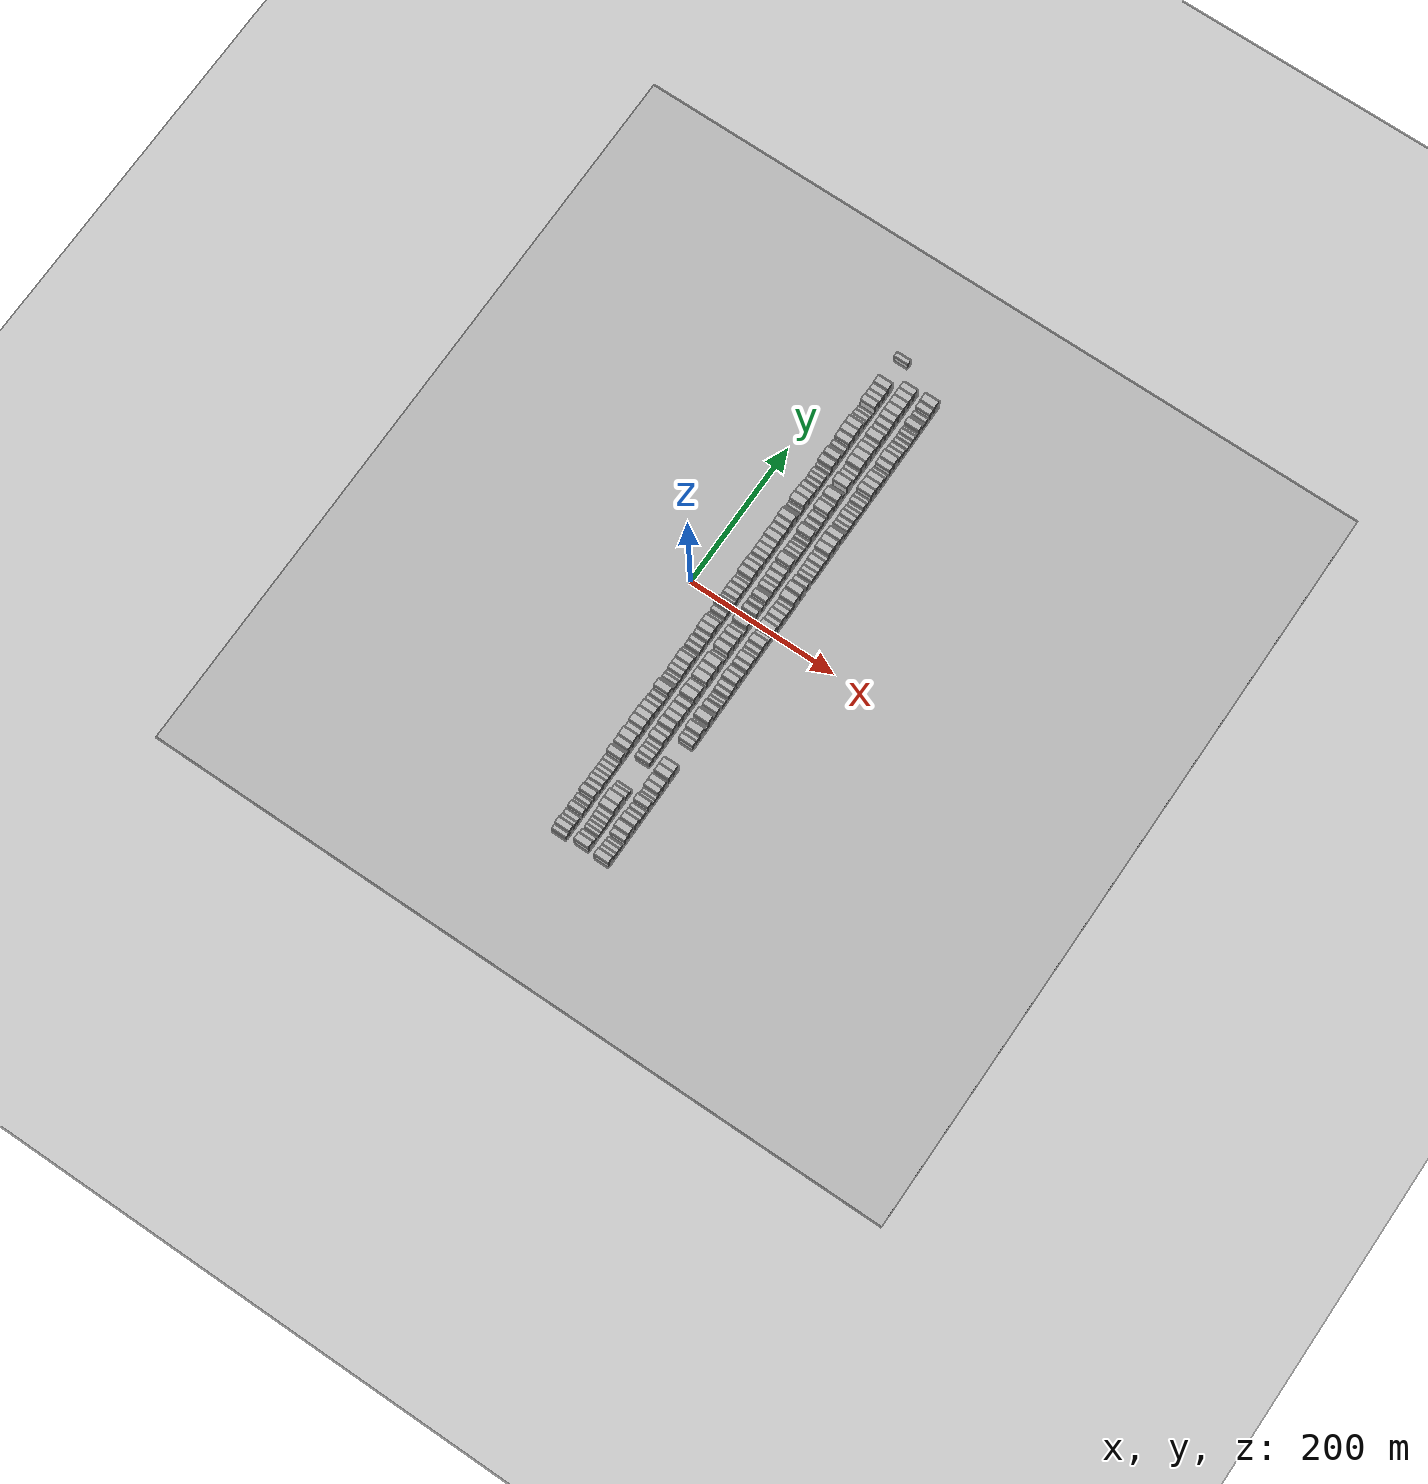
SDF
<?xml version="1.0" encoding="utf-8"?>

<sdf version="1.6">

   <world name="default">

      <gui fullscreen="0">

         <camera name="user_camera">

            <pose>-15 0 4.57585 0 0 0</pose>

            <view_controller>orbit</view_controller>

         </camera>

      </gui>

      <scene>

         <sky>

           <clouds>

             <speed>12</speed>

           </clouds>

         </sky>

         <ambient>0.4 0.4 0.4 1</ambient>

         <background>0.7 0.7 0.7 1</background>

         <shadows>1</shadows>

      </scene>

      <gravity>0 0 -9.8066</gravity>

      <magnetic_field>6e-06 2.3e-05 -4.2e-05</magnetic_field>

      <physics default="0" name="default_physics" type="ode">

         <ode>

            <solver>

               <type>quick</type>

               <iters>10</iters>

               <sor>1.0</sor>

               <use_dynamic_moi_rescaling>0</use_dynamic_moi_rescaling>

            </solver>

            <constraints>

               <cfm>0</cfm>

               <erp>0.2</erp>

               <contact_max_correcting_vel>100</contact_max_correcting_vel>

               <contact_surface_layer>0.001</contact_surface_layer>

            </constraints>

         </ode>

         <max_step_size>0.004</max_step_size>

         <real_time_factor>1</real_time_factor>

         <real_time_update_rate>250</real_time_update_rate>

      </physics>

      <light name="sun" type="directional">

         <cast_shadows>1</cast_shadows>

         <pose>0 0 10 0 0 0</pose>

         <diffuse>0.8 0.8 0.8 1</diffuse>

         <specular>0.2 0.2 0.2 1</specular>

         <attenuation>

            <range>1000</range>

            <constant>0.9</constant>

            <linear>0.01</linear>

            <quadratic>0.001</quadratic>

         </attenuation>

         <direction>-0.5 0.1 -0.9</direction>

      </light>

      <include>

         <name>ground_plane_1</name>

         <uri>model://HANNAS_ground_plane</uri>

         <pose>0 0 0  0 0 0</pose>

      </include>

      <include>

         <name>ground_plane_2</name>

         <uri>model://HANNAS_ground_plane</uri>

         <pose>100 0 0  0 0 0</pose>

      </include>

      <model name="building_1">

         <static>1</static>

         <pose frame="">50.0000 -332.7502 0 0.000000 0.000000 0.000000</pose>

         <link name="link">

            <pose frame="">0 0 7.50 0 0 0</pose>

            <collision name="collision">

               <geometry>

                  <box>

                     <size>20.0000 6.4996 15.0000</size>

                  </box>

               </geometry>

               <max_contacts>10</max_contacts>

               <surface>

                  <contact>

                     <ode/>

                  </contact>

                  <bounce/>

                  <friction>

                     <torsional>

                        <ode/>

                     </torsional>

                     <ode/>

                  </friction>

               </surface>

            </collision>

            <visual name="visual">

               <cast_shadows>0</cast_shadows>

               <geometry>

                  <box>

                     <size>20.0000 6.4996 15.0000</size>

                  </box>

               </geometry>

               <material>

                  <script>

                     <uri>model://HANNAS_wall/materials/scripts</uri>

                     <uri>model://HANNAS_wall/materials/textures</uri>

                     <name>vrc/HANNAS_wall</name>

                  </script>

               </material>

            </visual>

            <self_collide>0</self_collide>

            <enable_wind>0</enable_wind>

            <kinematic>0</kinematic>

         </link>

      </model>

      <model name="building_2">

         <static>1</static>

         <pose frame="">50.0000 -324.9821 0 0.000000 0.000000 0.000000</pose>

         <link name="link">

            <pose frame="">0 0 10.50 0 0 0</pose>

            <collision name="collision">

               <geometry>

                  <box>

                     <size>20.0000 9.0366 21.0000</size>

                  </box>

               </geometry>

               <max_contacts>10</max_contacts>

               <surface>

                  <contact>

                     <ode/>

                  </contact>

                  <bounce/>

                  <friction>

                     <torsional>

                        <ode/>

                     </torsional>

                     <ode/>

                  </friction>

               </surface>

            </collision>

            <visual name="visual">

               <cast_shadows>0</cast_shadows>

               <geometry>

                  <box>

                     <size>20.0000 9.0366 21.0000</size>

                  </box>

               </geometry>

               <material>

                  <script>

                     <uri>model://HANNAS_wall/materials/scripts</uri>

                     <uri>model://HANNAS_wall/materials/textures</uri>

                     <name>vrc/HANNAS_wall</name>

                  </script>

               </material>

            </visual>

            <self_collide>0</self_collide>

            <enable_wind>0</enable_wind>

            <kinematic>0</kinematic>

         </link>

      </model>

      <model name="building_3">

         <static>1</static>

         <pose frame="">50.0000 -317.1973 0 0.000000 0.000000 0.000000</pose>

         <link name="link">

            <pose frame="">0 0 7.50 0 0 0</pose>

            <collision name="collision">

               <geometry>

                  <box>

                     <size>20.0000 6.5330 15.0000</size>

                  </box>

               </geometry>

               <max_contacts>10</max_contacts>

               <surface>

                  <contact>

                     <ode/>

                  </contact>

                  <bounce/>

                  <friction>

                     <torsional>

                        <ode/>

                     </torsional>

                     <ode/>

                  </friction>

               </surface>

            </collision>

            <visual name="visual">

               <cast_shadows>0</cast_shadows>

               <geometry>

                  <box>

                     <size>20.0000 6.5330 15.0000</size>

                  </box>

               </geometry>

               <material>

                  <script>

                     <uri>model://HANNAS_wall/materials/scripts</uri>

                     <uri>model://HANNAS_wall/materials/textures</uri>

                     <name>vrc/HANNAS_wall</name>

                  </script>

               </material>

            </visual>

            <self_collide>0</self_collide>

            <enable_wind>0</enable_wind>

            <kinematic>0</kinematic>

         </link>

      </model>

      <model name="building_4">

         <static>1</static>

         <pose frame="">50.0000 -310.3645 0 0.000000 0.000000 0.000000</pose>

         <link name="link">

            <pose frame="">0 0 7.50 0 0 0</pose>

            <collision name="collision">

               <geometry>

                  <box>

                     <size>20.0000 7.1325 15.0000</size>

                  </box>

               </geometry>

               <max_contacts>10</max_contacts>

               <surface>

                  <contact>

                     <ode/>

                  </contact>

                  <bounce/>

                  <friction>

                     <torsional>

                        <ode/>

                     </torsional>

                     <ode/>

                  </friction>

               </surface>

            </collision>

            <visual name="visual">

               <cast_shadows>0</cast_shadows>

               <geometry>

                  <box>

                     <size>20.0000 7.1325 15.0000</size>

                  </box>

               </geometry>

               <material>

                  <script>

                     <uri>model://HANNAS_wall/materials/scripts</uri>

                     <uri>model://HANNAS_wall/materials/textures</uri>

                     <name>vrc/HANNAS_wall</name>

                  </script>

               </material>

            </visual>

            <self_collide>0</self_collide>

            <enable_wind>0</enable_wind>

            <kinematic>0</kinematic>

         </link>

      </model>

      <model name="building_5">

         <static>1</static>

         <pose frame="">50.0000 -299.8207 0 0.000000 0.000000 0.000000</pose>

         <link name="link">

            <pose frame="">0 0 9.00 0 0 0</pose>

            <collision name="collision">

               <geometry>

                  <box>

                     <size>20.0000 7.9552 18.0000</size>

                  </box>

               </geometry>

               <max_contacts>10</max_contacts>

               <surface>

                  <contact>

                     <ode/>

                  </contact>

                  <bounce/>

                  <friction>

                     <torsional>

                        <ode/>

                     </torsional>

                     <ode/>

                  </friction>

               </surface>

            </collision>

            <visual name="visual">

               <cast_shadows>0</cast_shadows>

               <geometry>

                  <box>

                     <size>20.0000 7.9552 18.0000</size>

                  </box>

               </geometry>

               <material>

                  <script>

                     <uri>model://HANNAS_wall/materials/scripts</uri>

                     <uri>model://HANNAS_wall/materials/textures</uri>

                     <name>vrc/HANNAS_wall</name>

                  </script>

               </material>

            </visual>

            <self_collide>0</self_collide>

            <enable_wind>0</enable_wind>

            <kinematic>0</kinematic>

         </link>

      </model>

      <model name="building_6">

         <static>1</static>

         <pose frame="">50.0000 -293.2829 0 0.000000 0.000000 0.000000</pose>

         <link name="link">

            <pose frame="">0 0 6.00 0 0 0</pose>

            <collision name="collision">

               <geometry>

                  <box>

                     <size>20.0000 5.1203 12.0000</size>

                  </box>

               </geometry>

               <max_contacts>10</max_contacts>

               <surface>

                  <contact>

                     <ode/>

                  </contact>

                  <bounce/>

                  <friction>

                     <torsional>

                        <ode/>

                     </torsional>

                     <ode/>

                  </friction>

               </surface>

            </collision>

            <visual name="visual">

               <cast_shadows>0</cast_shadows>

               <geometry>

                  <box>

                     <size>20.0000 5.1203 12.0000</size>

                  </box>

               </geometry>

               <material>

                  <script>

                     <uri>model://HANNAS_wall/materials/scripts</uri>

                     <uri>model://HANNAS_wall/materials/textures</uri>

                     <name>vrc/HANNAS_wall</name>

                  </script>

               </material>

            </visual>

            <self_collide>0</self_collide>

            <enable_wind>0</enable_wind>

            <kinematic>0</kinematic>

         </link>

      </model>

      <model name="building_7">

         <static>1</static>

         <pose frame="">50.0000 -287.5324 0 0.000000 0.000000 0.000000</pose>

         <link name="link">

            <pose frame="">0 0 7.50 0 0 0</pose>

            <collision name="collision">

               <geometry>

                  <box>

                     <size>20.0000 6.3807 15.0000</size>

                  </box>

               </geometry>

               <max_contacts>10</max_contacts>

               <surface>

                  <contact>

                     <ode/>

                  </contact>

                  <bounce/>

                  <friction>

                     <torsional>

                        <ode/>

                     </torsional>

                     <ode/>

                  </friction>

               </surface>

            </collision>

            <visual name="visual">

               <cast_shadows>0</cast_shadows>

               <geometry>

                  <box>

                     <size>20.0000 6.3807 15.0000</size>

                  </box>

               </geometry>

               <material>

                  <script>

                     <uri>model://HANNAS_wall/materials/scripts</uri>

                     <uri>model://HANNAS_wall/materials/textures</uri>

                     <name>vrc/HANNAS_wall</name>

                  </script>

               </material>

            </visual>

            <self_collide>0</self_collide>

            <enable_wind>0</enable_wind>

            <kinematic>0</kinematic>

         </link>

      </model>

      <model name="building_8">

         <static>1</static>

         <pose frame="">50.0000 -276.8166 0 0.000000 0.000000 0.000000</pose>

         <link name="link">

            <pose frame="">0 0 10.50 0 0 0</pose>

            <collision name="collision">

               <geometry>

                  <box>

                     <size>20.0000 9.0508 21.0000</size>

                  </box>

               </geometry>

               <max_contacts>10</max_contacts>

               <surface>

                  <contact>

                     <ode/>

                  </contact>

                  <bounce/>

                  <friction>

                     <torsional>

                        <ode/>

                     </torsional>

                     <ode/>

                  </friction>

               </surface>

            </collision>

            <visual name="visual">

               <cast_shadows>0</cast_shadows>

               <geometry>

                  <box>

                     <size>20.0000 9.0508 21.0000</size>

                  </box>

               </geometry>

               <material>

                  <script>

                     <uri>model://HANNAS_wall/materials/scripts</uri>

                     <uri>model://HANNAS_wall/materials/textures</uri>

                     <name>vrc/HANNAS_wall</name>

                  </script>

               </material>

            </visual>

            <self_collide>0</self_collide>

            <enable_wind>0</enable_wind>

            <kinematic>0</kinematic>

         </link>

      </model>

      <model name="building_9">

         <static>1</static>

         <pose frame="">50.0000 -266.7772 0 0.000000 0.000000 0.000000</pose>

         <link name="link">

            <pose frame="">0 0 7.50 0 0 0</pose>

            <collision name="collision">

               <geometry>

                  <box>

                     <size>20.0000 7.0281 15.0000</size>

                  </box>

               </geometry>

               <max_contacts>10</max_contacts>

               <surface>

                  <contact>

                     <ode/>

                  </contact>

                  <bounce/>

                  <friction>

                     <torsional>

                        <ode/>

                     </torsional>

                     <ode/>

                  </friction>

               </surface>

            </collision>

            <visual name="visual">

               <cast_shadows>0</cast_shadows>

               <geometry>

                  <box>

                     <size>20.0000 7.0281 15.0000</size>

                  </box>

               </geometry>

               <material>

                  <script>

                     <uri>model://HANNAS_wall/materials/scripts</uri>

                     <uri>model://HANNAS_wall/materials/textures</uri>

                     <name>vrc/HANNAS_wall</name>

                  </script>

               </material>

            </visual>

            <self_collide>0</self_collide>

            <enable_wind>0</enable_wind>

            <kinematic>0</kinematic>

         </link>

      </model>

      <model name="building_10">

         <static>1</static>

         <pose frame="">50.0000 -259.5586 0 0.000000 0.000000 0.000000</pose>

         <link name="link">

            <pose frame="">0 0 9.00 0 0 0</pose>

            <collision name="collision">

               <geometry>

                  <box>

                     <size>20.0000 7.4089 18.0000</size>

                  </box>

               </geometry>

               <max_contacts>10</max_contacts>

               <surface>

                  <contact>

                     <ode/>

                  </contact>

                  <bounce/>

                  <friction>

                     <torsional>

                        <ode/>

                     </torsional>

                     <ode/>

                  </friction>

               </surface>

            </collision>

            <visual name="visual">

               <cast_shadows>0</cast_shadows>

               <geometry>

                  <box>

                     <size>20.0000 7.4089 18.0000</size>

                  </box>

               </geometry>

               <material>

                  <script>

                     <uri>model://HANNAS_wall/materials/scripts</uri>

                     <uri>model://HANNAS_wall/materials/textures</uri>

                     <name>vrc/HANNAS_wall</name>

                  </script>

               </material>

            </visual>

            <self_collide>0</self_collide>

            <enable_wind>0</enable_wind>

            <kinematic>0</kinematic>

         </link>

      </model>

      <model name="building_11">

         <static>1</static>

         <pose frame="">50.0000 -252.4338 0 0.000000 0.000000 0.000000</pose>

         <link name="link">

            <pose frame="">0 0 7.50 0 0 0</pose>

            <collision name="collision">

               <geometry>

                  <box>

                     <size>20.0000 6.8408 15.0000</size>

                  </box>

               </geometry>

               <max_contacts>10</max_contacts>

               <surface>

                  <contact>

                     <ode/>

                  </contact>

                  <bounce/>

                  <friction>

                     <torsional>

                        <ode/>

                     </torsional>

                     <ode/>

                  </friction>

               </surface>

            </collision>

            <visual name="visual">

               <cast_shadows>0</cast_shadows>

               <geometry>

                  <box>

                     <size>20.0000 6.8408 15.0000</size>

                  </box>

               </geometry>

               <material>

                  <script>

                     <uri>model://HANNAS_wall/materials/scripts</uri>

                     <uri>model://HANNAS_wall/materials/textures</uri>

                     <name>vrc/HANNAS_wall</name>

                  </script>

               </material>

            </visual>

            <self_collide>0</self_collide>

            <enable_wind>0</enable_wind>

            <kinematic>0</kinematic>

         </link>

      </model>

      <model name="building_12">

         <static>1</static>

         <pose frame="">50.0000 -245.9089 0 0.000000 0.000000 0.000000</pose>

         <link name="link">

            <pose frame="">0 0 7.50 0 0 0</pose>

            <collision name="collision">

               <geometry>

                  <box>

                     <size>20.0000 6.2089 15.0000</size>

                  </box>

               </geometry>

               <max_contacts>10</max_contacts>

               <surface>

                  <contact>

                     <ode/>

                  </contact>

                  <bounce/>

                  <friction>

                     <torsional>

                        <ode/>

                     </torsional>

                     <ode/>

                  </friction>

               </surface>

            </collision>

            <visual name="visual">

               <cast_shadows>0</cast_shadows>

               <geometry>

                  <box>

                     <size>20.0000 6.2089 15.0000</size>

                  </box>

               </geometry>

               <material>

                  <script>

                     <uri>model://HANNAS_wall/materials/scripts</uri>

                     <uri>model://HANNAS_wall/materials/textures</uri>

                     <name>vrc/HANNAS_wall</name>

                  </script>

               </material>

            </visual>

            <self_collide>0</self_collide>

            <enable_wind>0</enable_wind>

            <kinematic>0</kinematic>

         </link>

      </model>

      <model name="building_13">

         <static>1</static>

         <pose frame="">50.0000 -239.2662 0 0.000000 0.000000 0.000000</pose>

         <link name="link">

            <pose frame="">0 0 7.50 0 0 0</pose>

            <collision name="collision">

               <geometry>

                  <box>

                     <size>20.0000 7.0766 15.0000</size>

                  </box>

               </geometry>

               <max_contacts>10</max_contacts>

               <surface>

                  <contact>

                     <ode/>

                  </contact>

                  <bounce/>

                  <friction>

                     <torsional>

                        <ode/>

                     </torsional>

                     <ode/>

                  </friction>

               </surface>

            </collision>

            <visual name="visual">

               <cast_shadows>0</cast_shadows>

               <geometry>

                  <box>

                     <size>20.0000 7.0766 15.0000</size>

                  </box>

               </geometry>

               <material>

                  <script>

                     <uri>model://HANNAS_wall/materials/scripts</uri>

                     <uri>model://HANNAS_wall/materials/textures</uri>

                     <name>vrc/HANNAS_wall</name>

                  </script>

               </material>

            </visual>

            <self_collide>0</self_collide>

            <enable_wind>0</enable_wind>

            <kinematic>0</kinematic>

         </link>

      </model>

      <model name="building_14">

         <static>1</static>

         <pose frame="">50.0000 -232.5082 0 0.000000 0.000000 0.000000</pose>

         <link name="link">

            <pose frame="">0 0 7.50 0 0 0</pose>

            <collision name="collision">

               <geometry>

                  <box>

                     <size>20.0000 6.4395 15.0000</size>

                  </box>

               </geometry>

               <max_contacts>10</max_contacts>

               <surface>

                  <contact>

                     <ode/>

                  </contact>

                  <bounce/>

                  <friction>

                     <torsional>

                        <ode/>

                     </torsional>

                     <ode/>

                  </friction>

               </surface>

            </collision>

            <visual name="visual">

               <cast_shadows>0</cast_shadows>

               <geometry>

                  <box>

                     <size>20.0000 6.4395 15.0000</size>

                  </box>

               </geometry>

               <material>

                  <script>

                     <uri>model://HANNAS_wall/materials/scripts</uri>

                     <uri>model://HANNAS_wall/materials/textures</uri>

                     <name>vrc/HANNAS_wall</name>

                  </script>

               </material>

            </visual>

            <self_collide>0</self_collide>

            <enable_wind>0</enable_wind>

            <kinematic>0</kinematic>

         </link>

      </model>

      <model name="building_15">

         <static>1</static>

         <pose frame="">50.0000 -222.4630 0 0.000000 0.000000 0.000000</pose>

         <link name="link">

            <pose frame="">0 0 12.00 0 0 0</pose>

            <collision name="collision">

               <geometry>

                  <box>

                     <size>20.0000 9.6509 24.0000</size>

                  </box>

               </geometry>

               <max_contacts>10</max_contacts>

               <surface>

                  <contact>

                     <ode/>

                  </contact>

                  <bounce/>

                  <friction>

                     <torsional>

                        <ode/>

                     </torsional>

                     <ode/>

                  </friction>

               </surface>

            </collision>

            <visual name="visual">

               <cast_shadows>0</cast_shadows>

               <geometry>

                  <box>

                     <size>20.0000 9.6509 24.0000</size>

                  </box>

               </geometry>

               <material>

                  <script>

                     <uri>model://HANNAS_wall/materials/scripts</uri>

                     <uri>model://HANNAS_wall/materials/textures</uri>

                     <name>vrc/HANNAS_wall</name>

                  </script>

               </material>

            </visual>

            <self_collide>0</self_collide>

            <enable_wind>0</enable_wind>

            <kinematic>0</kinematic>

         </link>

      </model>

      <model name="building_16">

         <static>1</static>

         <pose frame="">50.0000 -215.1452 0 0.000000 0.000000 0.000000</pose>

         <link name="link">

            <pose frame="">0 0 6.00 0 0 0</pose>

            <collision name="collision">

               <geometry>

                  <box>

                     <size>20.0000 4.9846 12.0000</size>

                  </box>

               </geometry>

               <max_contacts>10</max_contacts>

               <surface>

                  <contact>

                     <ode/>

                  </contact>

                  <bounce/>

                  <friction>

                     <torsional>

                        <ode/>

                     </torsional>

                     <ode/>

                  </friction>

               </surface>

            </collision>

            <visual name="visual">

               <cast_shadows>0</cast_shadows>

               <geometry>

                  <box>

                     <size>20.0000 4.9846 12.0000</size>

                  </box>

               </geometry>

               <material>

                  <script>

                     <uri>model://HANNAS_wall/materials/scripts</uri>

                     <uri>model://HANNAS_wall/materials/textures</uri>

                     <name>vrc/HANNAS_wall</name>

                  </script>

               </material>

            </visual>

            <self_collide>0</self_collide>

            <enable_wind>0</enable_wind>

            <kinematic>0</kinematic>

         </link>

      </model>

      <model name="building_17">

         <static>1</static>

         <pose frame="">50.0000 -208.2142 0 0.000000 0.000000 0.000000</pose>

         <link name="link">

            <pose frame="">0 0 10.50 0 0 0</pose>

            <collision name="collision">

               <geometry>

                  <box>

                     <size>20.0000 8.8775 21.0000</size>

                  </box>

               </geometry>

               <max_contacts>10</max_contacts>

               <surface>

                  <contact>

                     <ode/>

                  </contact>

                  <bounce/>

                  <friction>

                     <torsional>

                        <ode/>

                     </torsional>

                     <ode/>

                  </friction>

               </surface>

            </collision>

            <visual name="visual">

               <cast_shadows>0</cast_shadows>

               <geometry>

                  <box>

                     <size>20.0000 8.8775 21.0000</size>

                  </box>

               </geometry>

               <material>

                  <script>

                     <uri>model://HANNAS_wall/materials/scripts</uri>

                     <uri>model://HANNAS_wall/materials/textures</uri>

                     <name>vrc/HANNAS_wall</name>

                  </script>

               </material>

            </visual>

            <self_collide>0</self_collide>

            <enable_wind>0</enable_wind>

            <kinematic>0</kinematic>

         </link>

      </model>

      <model name="building_18">

         <static>1</static>

         <pose frame="">50.0000 -197.9803 0 0.000000 0.000000 0.000000</pose>

         <link name="link">

            <pose frame="">0 0 12.00 0 0 0</pose>

            <collision name="collision">

               <geometry>

                  <box>

                     <size>20.0000 11.5903 24.0000</size>

                  </box>

               </geometry>

               <max_contacts>10</max_contacts>

               <surface>

                  <contact>

                     <ode/>

                  </contact>

                  <bounce/>

                  <friction>

                     <torsional>

                        <ode/>

                     </torsional>

                     <ode/>

                  </friction>

               </surface>

            </collision>

            <visual name="visual">

               <cast_shadows>0</cast_shadows>

               <geometry>

                  <box>

                     <size>20.0000 11.5903 24.0000</size>

                  </box>

               </geometry>

               <material>

                  <script>

                     <uri>model://HANNAS_wall/materials/scripts</uri>

                     <uri>model://HANNAS_wall/materials/textures</uri>

                     <name>vrc/HANNAS_wall</name>

                  </script>

               </material>

            </visual>

            <self_collide>0</self_collide>

            <enable_wind>0</enable_wind>

            <kinematic>0</kinematic>

         </link>

      </model>

      <model name="building_19">

         <static>1</static>

         <pose frame="">50.0000 -187.0728 0 0.000000 0.000000 0.000000</pose>

         <link name="link">

            <pose frame="">0 0 9.00 0 0 0</pose>

            <collision name="collision">

               <geometry>

                  <box>

                     <size>20.0000 8.2246 18.0000</size>

                  </box>

               </geometry>

               <max_contacts>10</max_contacts>

               <surface>

                  <contact>

                     <ode/>

                  </contact>

                  <bounce/>

                  <friction>

                     <torsional>

                        <ode/>

                     </torsional>

                     <ode/>

                  </friction>

               </surface>

            </collision>

            <visual name="visual">

               <cast_shadows>0</cast_shadows>

               <geometry>

                  <box>

                     <size>20.0000 8.2246 18.0000</size>

                  </box>

               </geometry>

               <material>

                  <script>

                     <uri>model://HANNAS_wall/materials/scripts</uri>

                     <uri>model://HANNAS_wall/materials/textures</uri>

                     <name>vrc/HANNAS_wall</name>

                  </script>

               </material>

            </visual>

            <self_collide>0</self_collide>

            <enable_wind>0</enable_wind>

            <kinematic>0</kinematic>

         </link>

      </model>

      <model name="building_20">

         <static>1</static>

         <pose frame="">50.0000 -177.4510 0 0.000000 0.000000 0.000000</pose>

         <link name="link">

            <pose frame="">0 0 12.00 0 0 0</pose>

            <collision name="collision">

               <geometry>

                  <box>

                     <size>20.0000 11.0190 24.0000</size>

                  </box>

               </geometry>

               <max_contacts>10</max_contacts>

               <surface>

                  <contact>

                     <ode/>

                  </contact>

                  <bounce/>

                  <friction>

                     <torsional>

                        <ode/>

                     </torsional>

                     <ode/>

                  </friction>

               </surface>

            </collision>

            <visual name="visual">

               <cast_shadows>0</cast_shadows>

               <geometry>

                  <box>

                     <size>20.0000 11.0190 24.0000</size>

                  </box>

               </geometry>

               <material>

                  <script>

                     <uri>model://HANNAS_wall/materials/scripts</uri>

                     <uri>model://HANNAS_wall/materials/textures</uri>

                     <name>vrc/HANNAS_wall</name>

                  </script>

               </material>

            </visual>

            <self_collide>0</self_collide>

            <enable_wind>0</enable_wind>

            <kinematic>0</kinematic>

         </link>

      </model>

      <model name="building_21">

         <static>1</static>

         <pose frame="">50.0000 -166.8628 0 0.000000 0.000000 0.000000</pose>

         <link name="link">

            <pose frame="">0 0 12.00 0 0 0</pose>

            <collision name="collision">

               <geometry>

                  <box>

                     <size>20.0000 10.1574 24.0000</size>

                  </box>

               </geometry>

               <max_contacts>10</max_contacts>

               <surface>

                  <contact>

                     <ode/>

                  </contact>

                  <bounce/>

                  <friction>

                     <torsional>

                        <ode/>

                     </torsional>

                     <ode/>

                  </friction>

               </surface>

            </collision>

            <visual name="visual">

               <cast_shadows>0</cast_shadows>

               <geometry>

                  <box>

                     <size>20.0000 10.1574 24.0000</size>

                  </box>

               </geometry>

               <material>

                  <script>

                     <uri>model://HANNAS_wall/materials/scripts</uri>

                     <uri>model://HANNAS_wall/materials/textures</uri>

                     <name>vrc/HANNAS_wall</name>

                  </script>

               </material>

            </visual>

            <self_collide>0</self_collide>

            <enable_wind>0</enable_wind>

            <kinematic>0</kinematic>

         </link>

      </model>

      <model name="building_22">

         <static>1</static>

         <pose frame="">50.0000 -156.6081 0 0.000000 0.000000 0.000000</pose>

         <link name="link">

            <pose frame="">0 0 10.50 0 0 0</pose>

            <collision name="collision">

               <geometry>

                  <box>

                     <size>20.0000 10.3520 21.0000</size>

                  </box>

               </geometry>

               <max_contacts>10</max_contacts>

               <surface>

                  <contact>

                     <ode/>

                  </contact>

                  <bounce/>

                  <friction>

                     <torsional>

                        <ode/>

                     </torsional>

                     <ode/>

                  </friction>

               </surface>

            </collision>

            <visual name="visual">

               <cast_shadows>0</cast_shadows>

               <geometry>

                  <box>

                     <size>20.0000 10.3520 21.0000</size>

                  </box>

               </geometry>

               <material>

                  <script>

                     <uri>model://HANNAS_wall/materials/scripts</uri>

                     <uri>model://HANNAS_wall/materials/textures</uri>

                     <name>vrc/HANNAS_wall</name>

                  </script>

               </material>

            </visual>

            <self_collide>0</self_collide>

            <enable_wind>0</enable_wind>

            <kinematic>0</kinematic>

         </link>

      </model>

      <model name="building_23">

         <static>1</static>

         <pose frame="">50.0000 -147.7831 0 0.000000 0.000000 0.000000</pose>

         <link name="link">

            <pose frame="">0 0 9.00 0 0 0</pose>

            <collision name="collision">

               <geometry>

                  <box>

                     <size>20.0000 7.2980 18.0000</size>

                  </box>

               </geometry>

               <max_contacts>10</max_contacts>

               <surface>

                  <contact>

                     <ode/>

                  </contact>

                  <bounce/>

                  <friction>

                     <torsional>

                        <ode/>

                     </torsional>

                     <ode/>

                  </friction>

               </surface>

            </collision>

            <visual name="visual">

               <cast_shadows>0</cast_shadows>

               <geometry>

                  <box>

                     <size>20.0000 7.2980 18.0000</size>

                  </box>

               </geometry>

               <material>

                  <script>

                     <uri>model://HANNAS_wall/materials/scripts</uri>

                     <uri>model://HANNAS_wall/materials/textures</uri>

                     <name>vrc/HANNAS_wall</name>

                  </script>

               </material>

            </visual>

            <self_collide>0</self_collide>

            <enable_wind>0</enable_wind>

            <kinematic>0</kinematic>

         </link>

      </model>

      <model name="building_24">

         <static>1</static>

         <pose frame="">50.0000 -138.5354 0 0.000000 0.000000 0.000000</pose>

         <link name="link">

            <pose frame="">0 0 7.50 0 0 0</pose>

            <collision name="collision">

               <geometry>

                  <box>

                     <size>20.0000 7.1975 15.0000</size>

                  </box>

               </geometry>

               <max_contacts>10</max_contacts>

               <surface>

                  <contact>

                     <ode/>

                  </contact>

                  <bounce/>

                  <friction>

                     <torsional>

                        <ode/>

                     </torsional>

                     <ode/>

                  </friction>

               </surface>

            </collision>

            <visual name="visual">

               <cast_shadows>0</cast_shadows>

               <geometry>

                  <box>

                     <size>20.0000 7.1975 15.0000</size>

                  </box>

               </geometry>

               <material>

                  <script>

                     <uri>model://HANNAS_wall/materials/scripts</uri>

                     <uri>model://HANNAS_wall/materials/textures</uri>

                     <name>vrc/HANNAS_wall</name>

                  </script>

               </material>

            </visual>

            <self_collide>0</self_collide>

            <enable_wind>0</enable_wind>

            <kinematic>0</kinematic>

         </link>

      </model>

      <model name="building_25">

         <static>1</static>

         <pose frame="">50.0000 -127.7857 0 0.000000 0.000000 0.000000</pose>

         <link name="link">

            <pose frame="">0 0 12.00 0 0 0</pose>

            <collision name="collision">

               <geometry>

                  <box>

                     <size>20.0000 10.3019 24.0000</size>

                  </box>

               </geometry>

               <max_contacts>10</max_contacts>

               <surface>

                  <contact>

                     <ode/>

                  </contact>

                  <bounce/>

                  <friction>

                     <torsional>

                        <ode/>

                     </torsional>

                     <ode/>

                  </friction>

               </surface>

            </collision>

            <visual name="visual">

               <cast_shadows>0</cast_shadows>

               <geometry>

                  <box>

                     <size>20.0000 10.3019 24.0000</size>

                  </box>

               </geometry>

               <material>

                  <script>

                     <uri>model://HANNAS_wall/materials/scripts</uri>

                     <uri>model://HANNAS_wall/materials/textures</uri>

                     <name>vrc/HANNAS_wall</name>

                  </script>

               </material>

            </visual>

            <self_collide>0</self_collide>

            <enable_wind>0</enable_wind>

            <kinematic>0</kinematic>

         </link>

      </model>

      <model name="building_26">

         <static>1</static>

         <pose frame="">50.0000 -119.6560 0 0.000000 0.000000 0.000000</pose>

         <link name="link">

            <pose frame="">0 0 6.00 0 0 0</pose>

            <collision name="collision">

               <geometry>

                  <box>

                     <size>20.0000 5.9576 12.0000</size>

                  </box>

               </geometry>

               <max_contacts>10</max_contacts>

               <surface>

                  <contact>

                     <ode/>

                  </contact>

                  <bounce/>

                  <friction>

                     <torsional>

                        <ode/>

                     </torsional>

                     <ode/>

                  </friction>

               </surface>

            </collision>

            <visual name="visual">

               <cast_shadows>0</cast_shadows>

               <geometry>

                  <box>

                     <size>20.0000 5.9576 12.0000</size>

                  </box>

               </geometry>

               <material>

                  <script>

                     <uri>model://HANNAS_wall/materials/scripts</uri>

                     <uri>model://HANNAS_wall/materials/textures</uri>

                     <name>vrc/HANNAS_wall</name>

                  </script>

               </material>

            </visual>

            <self_collide>0</self_collide>

            <enable_wind>0</enable_wind>

            <kinematic>0</kinematic>

         </link>

      </model>

      <model name="building_27">

         <static>1</static>

         <pose frame="">50.0000 -113.5706 0 0.000000 0.000000 0.000000</pose>

         <link name="link">

            <pose frame="">0 0 7.50 0 0 0</pose>

            <collision name="collision">

               <geometry>

                  <box>

                     <size>20.0000 6.2130 15.0000</size>

                  </box>

               </geometry>

               <max_contacts>10</max_contacts>

               <surface>

                  <contact>

                     <ode/>

                  </contact>

                  <bounce/>

                  <friction>

                     <torsional>

                        <ode/>

                     </torsional>

                     <ode/>

                  </friction>

               </surface>

            </collision>

            <visual name="visual">

               <cast_shadows>0</cast_shadows>

               <geometry>

                  <box>

                     <size>20.0000 6.2130 15.0000</size>

                  </box>

               </geometry>

               <material>

                  <script>

                     <uri>model://HANNAS_wall/materials/scripts</uri>

                     <uri>model://HANNAS_wall/materials/textures</uri>

                     <name>vrc/HANNAS_wall</name>

                  </script>

               </material>

            </visual>

            <self_collide>0</self_collide>

            <enable_wind>0</enable_wind>

            <kinematic>0</kinematic>

         </link>

      </model>

      <model name="building_28">

         <static>1</static>

         <pose frame="">50.0000 -107.7802 0 0.000000 0.000000 0.000000</pose>

         <link name="link">

            <pose frame="">0 0 6.00 0 0 0</pose>

            <collision name="collision">

               <geometry>

                  <box>

                     <size>20.0000 5.3678 12.0000</size>

                  </box>

               </geometry>

               <max_contacts>10</max_contacts>

               <surface>

                  <contact>

                     <ode/>

                  </contact>

                  <bounce/>

                  <friction>

                     <torsional>

                        <ode/>

                     </torsional>

                     <ode/>

                  </friction>

               </surface>

            </collision>

            <visual name="visual">

               <cast_shadows>0</cast_shadows>

               <geometry>

                  <box>

                     <size>20.0000 5.3678 12.0000</size>

                  </box>

               </geometry>

               <material>

                  <script>

                     <uri>model://HANNAS_wall/materials/scripts</uri>

                     <uri>model://HANNAS_wall/materials/textures</uri>

                     <name>vrc/HANNAS_wall</name>

                  </script>

               </material>

            </visual>

            <self_collide>0</self_collide>

            <enable_wind>0</enable_wind>

            <kinematic>0</kinematic>

         </link>

      </model>

      <model name="building_29">

         <static>1</static>

         <pose frame="">50.0000 -101.1419 0 0.000000 0.000000 0.000000</pose>

         <link name="link">

            <pose frame="">0 0 9.00 0 0 0</pose>

            <collision name="collision">

               <geometry>

                  <box>

                     <size>20.0000 7.9087 18.0000</size>

                  </box>

               </geometry>

               <max_contacts>10</max_contacts>

               <surface>

                  <contact>

                     <ode/>

                  </contact>

                  <bounce/>

                  <friction>

                     <torsional>

                        <ode/>

                     </torsional>

                     <ode/>

                  </friction>

               </surface>

            </collision>

            <visual name="visual">

               <cast_shadows>0</cast_shadows>

               <geometry>

                  <box>

                     <size>20.0000 7.9087 18.0000</size>

                  </box>

               </geometry>

               <material>

                  <script>

                     <uri>model://HANNAS_wall/materials/scripts</uri>

                     <uri>model://HANNAS_wall/materials/textures</uri>

                     <name>vrc/HANNAS_wall</name>

                  </script>

               </material>

            </visual>

            <self_collide>0</self_collide>

            <enable_wind>0</enable_wind>

            <kinematic>0</kinematic>

         </link>

      </model>

      <model name="building_30">

         <static>1</static>

         <pose frame="">50.0000 -93.2247 0 0.000000 0.000000 0.000000</pose>

         <link name="link">

            <pose frame="">0 0 9.00 0 0 0</pose>

            <collision name="collision">

               <geometry>

                  <box>

                     <size>20.0000 7.9257 18.0000</size>

                  </box>

               </geometry>

               <max_contacts>10</max_contacts>

               <surface>

                  <contact>

                     <ode/>

                  </contact>

                  <bounce/>

                  <friction>

                     <torsional>

                        <ode/>

                     </torsional>

                     <ode/>

                  </friction>

               </surface>

            </collision>

            <visual name="visual">

               <cast_shadows>0</cast_shadows>

               <geometry>

                  <box>

                     <size>20.0000 7.9257 18.0000</size>

                  </box>

               </geometry>

               <material>

                  <script>

                     <uri>model://HANNAS_wall/materials/scripts</uri>

                     <uri>model://HANNAS_wall/materials/textures</uri>

                     <name>vrc/HANNAS_wall</name>

                  </script>

               </material>

            </visual>

            <self_collide>0</self_collide>

            <enable_wind>0</enable_wind>

            <kinematic>0</kinematic>

         </link>

      </model>

      <model name="building_31">

         <static>1</static>

         <pose frame="">50.0000 -84.1752 0 0.000000 0.000000 0.000000</pose>

         <link name="link">

            <pose frame="">0 0 10.50 0 0 0</pose>

            <collision name="collision">

               <geometry>

                  <box>

                     <size>20.0000 10.1734 21.0000</size>

                  </box>

               </geometry>

               <max_contacts>10</max_contacts>

               <surface>

                  <contact>

                     <ode/>

                  </contact>

                  <bounce/>

                  <friction>

                     <torsional>

                        <ode/>

                     </torsional>

                     <ode/>

                  </friction>

               </surface>

            </collision>

            <visual name="visual">

               <cast_shadows>0</cast_shadows>

               <geometry>

                  <box>

                     <size>20.0000 10.1734 21.0000</size>

                  </box>

               </geometry>

               <material>

                  <script>

                     <uri>model://HANNAS_wall/materials/scripts</uri>

                     <uri>model://HANNAS_wall/materials/textures</uri>

                     <name>vrc/HANNAS_wall</name>

                  </script>

               </material>

            </visual>

            <self_collide>0</self_collide>

            <enable_wind>0</enable_wind>

            <kinematic>0</kinematic>

         </link>

      </model>

      <model name="building_32">

         <static>1</static>

         <pose frame="">50.0000 -76.0340 0 0.000000 0.000000 0.000000</pose>

         <link name="link">

            <pose frame="">0 0 7.50 0 0 0</pose>

            <collision name="collision">

               <geometry>

                  <box>

                     <size>20.0000 6.1088 15.0000</size>

                  </box>

               </geometry>

               <max_contacts>10</max_contacts>

               <surface>

                  <contact>

                     <ode/>

                  </contact>

                  <bounce/>

                  <friction>

                     <torsional>

                        <ode/>

                     </torsional>

                     <ode/>

                  </friction>

               </surface>

            </collision>

            <visual name="visual">

               <cast_shadows>0</cast_shadows>

               <geometry>

                  <box>

                     <size>20.0000 6.1088 15.0000</size>

                  </box>

               </geometry>

               <material>

                  <script>

                     <uri>model://HANNAS_wall/materials/scripts</uri>

                     <uri>model://HANNAS_wall/materials/textures</uri>

                     <name>vrc/HANNAS_wall</name>

                  </script>

               </material>

            </visual>

            <self_collide>0</self_collide>

            <enable_wind>0</enable_wind>

            <kinematic>0</kinematic>

         </link>

      </model>

      <model name="building_33">

         <static>1</static>

         <pose frame="">50.0000 -66.5086 0 0.000000 0.000000 0.000000</pose>

         <link name="link">

            <pose frame="">0 0 7.50 0 0 0</pose>

            <collision name="collision">

               <geometry>

                  <box>

                     <size>20.0000 6.9421 15.0000</size>

                  </box>

               </geometry>

               <max_contacts>10</max_contacts>

               <surface>

                  <contact>

                     <ode/>

                  </contact>

                  <bounce/>

                  <friction>

                     <torsional>

                        <ode/>

                     </torsional>

                     <ode/>

                  </friction>

               </surface>

            </collision>

            <visual name="visual">

               <cast_shadows>0</cast_shadows>

               <geometry>

                  <box>

                     <size>20.0000 6.9421 15.0000</size>

                  </box>

               </geometry>

               <material>

                  <script>

                     <uri>model://HANNAS_wall/materials/scripts</uri>

                     <uri>model://HANNAS_wall/materials/textures</uri>

                     <name>vrc/HANNAS_wall</name>

                  </script>

               </material>

            </visual>

            <self_collide>0</self_collide>

            <enable_wind>0</enable_wind>

            <kinematic>0</kinematic>

         </link>

      </model>

      <model name="building_34">

         <static>1</static>

         <pose frame="">50.0000 -59.3887 0 0.000000 0.000000 0.000000</pose>

         <link name="link">

            <pose frame="">0 0 9.00 0 0 0</pose>

            <collision name="collision">

               <geometry>

                  <box>

                     <size>20.0000 7.2976 18.0000</size>

                  </box>

               </geometry>

               <max_contacts>10</max_contacts>

               <surface>

                  <contact>

                     <ode/>

                  </contact>

                  <bounce/>

                  <friction>

                     <torsional>

                        <ode/>

                     </torsional>

                     <ode/>

                  </friction>

               </surface>

            </collision>

            <visual name="visual">

               <cast_shadows>0</cast_shadows>

               <geometry>

                  <box>

                     <size>20.0000 7.2976 18.0000</size>

                  </box>

               </geometry>

               <material>

                  <script>

                     <uri>model://HANNAS_wall/materials/scripts</uri>

                     <uri>model://HANNAS_wall/materials/textures</uri>

                     <name>vrc/HANNAS_wall</name>

                  </script>

               </material>

            </visual>

            <self_collide>0</self_collide>

            <enable_wind>0</enable_wind>

            <kinematic>0</kinematic>

         </link>

      </model>

      <model name="building_35">

         <static>1</static>

         <pose frame="">50.0000 -49.1687 0 0.000000 0.000000 0.000000</pose>

         <link name="link">

            <pose frame="">0 0 7.50 0 0 0</pose>

            <collision name="collision">

               <geometry>

                  <box>

                     <size>20.0000 7.1424 15.0000</size>

                  </box>

               </geometry>

               <max_contacts>10</max_contacts>

               <surface>

                  <contact>

                     <ode/>

                  </contact>

                  <bounce/>

                  <friction>

                     <torsional>

                        <ode/>

                     </torsional>

                     <ode/>

                  </friction>

               </surface>

            </collision>

            <visual name="visual">

               <cast_shadows>0</cast_shadows>

               <geometry>

                  <box>

                     <size>20.0000 7.1424 15.0000</size>

                  </box>

               </geometry>

               <material>

                  <script>

                     <uri>model://HANNAS_wall/materials/scripts</uri>

                     <uri>model://HANNAS_wall/materials/textures</uri>

                     <name>vrc/HANNAS_wall</name>

                  </script>

               </material>

            </visual>

            <self_collide>0</self_collide>

            <enable_wind>0</enable_wind>

            <kinematic>0</kinematic>

         </link>

      </model>

      <model name="building_36">

         <static>1</static>

         <pose frame="">50.0000 -40.7982 0 0.000000 0.000000 0.000000</pose>

         <link name="link">

            <pose frame="">0 0 10.50 0 0 0</pose>

            <collision name="collision">

               <geometry>

                  <box>

                     <size>20.0000 9.5987 21.0000</size>

                  </box>

               </geometry>

               <max_contacts>10</max_contacts>

               <surface>

                  <contact>

                     <ode/>

                  </contact>

                  <bounce/>

                  <friction>

                     <torsional>

                        <ode/>

                     </torsional>

                     <ode/>

                  </friction>

               </surface>

            </collision>

            <visual name="visual">

               <cast_shadows>0</cast_shadows>

               <geometry>

                  <box>

                     <size>20.0000 9.5987 21.0000</size>

                  </box>

               </geometry>

               <material>

                  <script>

                     <uri>model://HANNAS_wall/materials/scripts</uri>

                     <uri>model://HANNAS_wall/materials/textures</uri>

                     <name>vrc/HANNAS_wall</name>

                  </script>

               </material>

            </visual>

            <self_collide>0</self_collide>

            <enable_wind>0</enable_wind>

            <kinematic>0</kinematic>

         </link>

      </model>

      <model name="building_37">

         <static>1</static>

         <pose frame="">50.0000 -31.3632 0 0.000000 0.000000 0.000000</pose>

         <link name="link">

            <pose frame="">0 0 10.50 0 0 0</pose>

            <collision name="collision">

               <geometry>

                  <box>

                     <size>20.0000 9.2714 21.0000</size>

                  </box>

               </geometry>

               <max_contacts>10</max_contacts>

               <surface>

                  <contact>

                     <ode/>

                  </contact>

                  <bounce/>

                  <friction>

                     <torsional>

                        <ode/>

                     </torsional>

                     <ode/>

                  </friction>

               </surface>

            </collision>

            <visual name="visual">

               <cast_shadows>0</cast_shadows>

               <geometry>

                  <box>

                     <size>20.0000 9.2714 21.0000</size>

                  </box>

               </geometry>

               <material>

                  <script>

                     <uri>model://HANNAS_wall/materials/scripts</uri>

                     <uri>model://HANNAS_wall/materials/textures</uri>

                     <name>vrc/HANNAS_wall</name>

                  </script>

               </material>

            </visual>

            <self_collide>0</self_collide>

            <enable_wind>0</enable_wind>

            <kinematic>0</kinematic>

         </link>

      </model>

      <model name="building_38">

         <static>1</static>

         <pose frame="">50.0000 -23.0225 0 0.000000 0.000000 0.000000</pose>

         <link name="link">

            <pose frame="">0 0 6.00 0 0 0</pose>

            <collision name="collision">

               <geometry>

                  <box>

                     <size>20.0000 5.4099 12.0000</size>

                  </box>

               </geometry>

               <max_contacts>10</max_contacts>

               <surface>

                  <contact>

                     <ode/>

                  </contact>

                  <bounce/>

                  <friction>

                     <torsional>

                        <ode/>

                     </torsional>

                     <ode/>

                  </friction>

               </surface>

            </collision>

            <visual name="visual">

               <cast_shadows>0</cast_shadows>

               <geometry>

                  <box>

                     <size>20.0000 5.4099 12.0000</size>

                  </box>

               </geometry>

               <material>

                  <script>

                     <uri>model://HANNAS_wall/materials/scripts</uri>

                     <uri>model://HANNAS_wall/materials/textures</uri>

                     <name>vrc/HANNAS_wall</name>

                  </script>

               </material>

            </visual>

            <self_collide>0</self_collide>

            <enable_wind>0</enable_wind>

            <kinematic>0</kinematic>

         </link>

      </model>

      <model name="building_39">

         <static>1</static>

         <pose frame="">50.0000 -14.6906 0 0.000000 0.000000 0.000000</pose>

         <link name="link">

            <pose frame="">0 0 7.50 0 0 0</pose>

            <collision name="collision">

               <geometry>

                  <box>

                     <size>20.0000 7.2540 15.0000</size>

                  </box>

               </geometry>

               <max_contacts>10</max_contacts>

               <surface>

                  <contact>

                     <ode/>

                  </contact>

                  <bounce/>

                  <friction>

                     <torsional>

                        <ode/>

                     </torsional>

                     <ode/>

                  </friction>

               </surface>

            </collision>

            <visual name="visual">

               <cast_shadows>0</cast_shadows>

               <geometry>

                  <box>

                     <size>20.0000 7.2540 15.0000</size>

                  </box>

               </geometry>

               <material>

                  <script>

                     <uri>model://HANNAS_wall/materials/scripts</uri>

                     <uri>model://HANNAS_wall/materials/textures</uri>

                     <name>vrc/HANNAS_wall</name>

                  </script>

               </material>

            </visual>

            <self_collide>0</self_collide>

            <enable_wind>0</enable_wind>

            <kinematic>0</kinematic>

         </link>

      </model>

      <model name="building_40">

         <static>1</static>

         <pose frame="">50.0000 -5.6001 0 0.000000 0.000000 0.000000</pose>

         <link name="link">

            <pose frame="">0 0 12.00 0 0 0</pose>

            <collision name="collision">

               <geometry>

                  <box>

                     <size>20.0000 10.9268 24.0000</size>

                  </box>

               </geometry>

               <max_contacts>10</max_contacts>

               <surface>

                  <contact>

                     <ode/>

                  </contact>

                  <bounce/>

                  <friction>

                     <torsional>

                        <ode/>

                     </torsional>

                     <ode/>

                  </friction>

               </surface>

            </collision>

            <visual name="visual">

               <cast_shadows>0</cast_shadows>

               <geometry>

                  <box>

                     <size>20.0000 10.9268 24.0000</size>

                  </box>

               </geometry>

               <material>

                  <script>

                     <uri>model://HANNAS_wall/materials/scripts</uri>

                     <uri>model://HANNAS_wall/materials/textures</uri>

                     <name>vrc/HANNAS_wall</name>

                  </script>

               </material>

            </visual>

            <self_collide>0</self_collide>

            <enable_wind>0</enable_wind>

            <kinematic>0</kinematic>

         </link>

      </model>

      <model name="building_41">

         <static>1</static>

         <pose frame="">50.0000 3.3759 0 0.000000 0.000000 0.000000</pose>

         <link name="link">

            <pose frame="">0 0 7.50 0 0 0</pose>

            <collision name="collision">

               <geometry>

                  <box>

                     <size>20.0000 7.0253 15.0000</size>

                  </box>

               </geometry>

               <max_contacts>10</max_contacts>

               <surface>

                  <contact>

                     <ode/>

                  </contact>

                  <bounce/>

                  <friction>

                     <torsional>

                        <ode/>

                     </torsional>

                     <ode/>

                  </friction>

               </surface>

            </collision>

            <visual name="visual">

               <cast_shadows>0</cast_shadows>

               <geometry>

                  <box>

                     <size>20.0000 7.0253 15.0000</size>

                  </box>

               </geometry>

               <material>

                  <script>

                     <uri>model://HANNAS_wall/materials/scripts</uri>

                     <uri>model://HANNAS_wall/materials/textures</uri>

                     <name>vrc/HANNAS_wall</name>

                  </script>

               </material>

            </visual>

            <self_collide>0</self_collide>

            <enable_wind>0</enable_wind>

            <kinematic>0</kinematic>

         </link>

      </model>

      <model name="building_42">

         <static>1</static>

         <pose frame="">50.0000 10.7546 0 0.000000 0.000000 0.000000</pose>

         <link name="link">

            <pose frame="">0 0 9.00 0 0 0</pose>

            <collision name="collision">

               <geometry>

                  <box>

                     <size>20.0000 7.7320 18.0000</size>

                  </box>

               </geometry>

               <max_contacts>10</max_contacts>

               <surface>

                  <contact>

                     <ode/>

                  </contact>

                  <bounce/>

                  <friction>

                     <torsional>

                        <ode/>

                     </torsional>

                     <ode/>

                  </friction>

               </surface>

            </collision>

            <visual name="visual">

               <cast_shadows>0</cast_shadows>

               <geometry>

                  <box>

                     <size>20.0000 7.7320 18.0000</size>

                  </box>

               </geometry>

               <material>

                  <script>

                     <uri>model://HANNAS_wall/materials/scripts</uri>

                     <uri>model://HANNAS_wall/materials/textures</uri>

                     <name>vrc/HANNAS_wall</name>

                  </script>

               </material>

            </visual>

            <self_collide>0</self_collide>

            <enable_wind>0</enable_wind>

            <kinematic>0</kinematic>

         </link>

      </model>

      <model name="building_43">

         <static>1</static>

         <pose frame="">50.0000 18.4982 0 0.000000 0.000000 0.000000</pose>

         <link name="link">

            <pose frame="">0 0 9.00 0 0 0</pose>

            <collision name="collision">

               <geometry>

                  <box>

                     <size>20.0000 7.7552 18.0000</size>

                  </box>

               </geometry>

               <max_contacts>10</max_contacts>

               <surface>

                  <contact>

                     <ode/>

                  </contact>

                  <bounce/>

                  <friction>

                     <torsional>

                        <ode/>

                     </torsional>

                     <ode/>

                  </friction>

               </surface>

            </collision>

            <visual name="visual">

               <cast_shadows>0</cast_shadows>

               <geometry>

                  <box>

                     <size>20.0000 7.7552 18.0000</size>

                  </box>

               </geometry>

               <material>

                  <script>

                     <uri>model://HANNAS_wall/materials/scripts</uri>

                     <uri>model://HANNAS_wall/materials/textures</uri>

                     <name>vrc/HANNAS_wall</name>

                  </script>

               </material>

            </visual>

            <self_collide>0</self_collide>

            <enable_wind>0</enable_wind>

            <kinematic>0</kinematic>

         </link>

      </model>

      <model name="building_44">

         <static>1</static>

         <pose frame="">50.0000 27.9174 0 0.000000 0.000000 0.000000</pose>

         <link name="link">

            <pose frame="">0 0 7.50 0 0 0</pose>

            <collision name="collision">

               <geometry>

                  <box>

                     <size>20.0000 7.0834 15.0000</size>

                  </box>

               </geometry>

               <max_contacts>10</max_contacts>

               <surface>

                  <contact>

                     <ode/>

                  </contact>

                  <bounce/>

                  <friction>

                     <torsional>

                        <ode/>

                     </torsional>

                     <ode/>

                  </friction>

               </surface>

            </collision>

            <visual name="visual">

               <cast_shadows>0</cast_shadows>

               <geometry>

                  <box>

                     <size>20.0000 7.0834 15.0000</size>

                  </box>

               </geometry>

               <material>

                  <script>

                     <uri>model://HANNAS_wall/materials/scripts</uri>

                     <uri>model://HANNAS_wall/materials/textures</uri>

                     <name>vrc/HANNAS_wall</name>

                  </script>

               </material>

            </visual>

            <self_collide>0</self_collide>

            <enable_wind>0</enable_wind>

            <kinematic>0</kinematic>

         </link>

      </model>

      <model name="building_45">

         <static>1</static>

         <pose frame="">50.0000 34.1626 0 0.000000 0.000000 0.000000</pose>

         <link name="link">

            <pose frame="">0 0 6.00 0 0 0</pose>

            <collision name="collision">

               <geometry>

                  <box>

                     <size>20.0000 5.4071 12.0000</size>

                  </box>

               </geometry>

               <max_contacts>10</max_contacts>

               <surface>

                  <contact>

                     <ode/>

                  </contact>

                  <bounce/>

                  <friction>

                     <torsional>

                        <ode/>

                     </torsional>

                     <ode/>

                  </friction>

               </surface>

            </collision>

            <visual name="visual">

               <cast_shadows>0</cast_shadows>

               <geometry>

                  <box>

                     <size>20.0000 5.4071 12.0000</size>

                  </box>

               </geometry>

               <material>

                  <script>

                     <uri>model://HANNAS_wall/materials/scripts</uri>

                     <uri>model://HANNAS_wall/materials/textures</uri>

                     <name>vrc/HANNAS_wall</name>

                  </script>

               </material>

            </visual>

            <self_collide>0</self_collide>

            <enable_wind>0</enable_wind>

            <kinematic>0</kinematic>

         </link>

      </model>

      <model name="building_46">

         <static>1</static>

         <pose frame="">50.0000 41.8215 0 0.000000 0.000000 0.000000</pose>

         <link name="link">

            <pose frame="">0 0 10.50 0 0 0</pose>

            <collision name="collision">

               <geometry>

                  <box>

                     <size>20.0000 9.9106 21.0000</size>

                  </box>

               </geometry>

               <max_contacts>10</max_contacts>

               <surface>

                  <contact>

                     <ode/>

                  </contact>

                  <bounce/>

                  <friction>

                     <torsional>

                        <ode/>

                     </torsional>

                     <ode/>

                  </friction>

               </surface>

            </collision>

            <visual name="visual">

               <cast_shadows>0</cast_shadows>

               <geometry>

                  <box>

                     <size>20.0000 9.9106 21.0000</size>

                  </box>

               </geometry>

               <material>

                  <script>

                     <uri>model://HANNAS_wall/materials/scripts</uri>

                     <uri>model://HANNAS_wall/materials/textures</uri>

                     <name>vrc/HANNAS_wall</name>

                  </script>

               </material>

            </visual>

            <self_collide>0</self_collide>

            <enable_wind>0</enable_wind>

            <kinematic>0</kinematic>

         </link>

      </model>

      <model name="building_47">

         <static>1</static>

         <pose frame="">50.0000 52.1036 0 0.000000 0.000000 0.000000</pose>

         <link name="link">

            <pose frame="">0 0 10.50 0 0 0</pose>

            <collision name="collision">

               <geometry>

                  <box>

                     <size>20.0000 8.6536 21.0000</size>

                  </box>

               </geometry>

               <max_contacts>10</max_contacts>

               <surface>

                  <contact>

                     <ode/>

                  </contact>

                  <bounce/>

                  <friction>

                     <torsional>

                        <ode/>

                     </torsional>

                     <ode/>

                  </friction>

               </surface>

            </collision>

            <visual name="visual">

               <cast_shadows>0</cast_shadows>

               <geometry>

                  <box>

                     <size>20.0000 8.6536 21.0000</size>

                  </box>

               </geometry>

               <material>

                  <script>

                     <uri>model://HANNAS_wall/materials/scripts</uri>

                     <uri>model://HANNAS_wall/materials/textures</uri>

                     <name>vrc/HANNAS_wall</name>

                  </script>

               </material>

            </visual>

            <self_collide>0</self_collide>

            <enable_wind>0</enable_wind>

            <kinematic>0</kinematic>

         </link>

      </model>

      <model name="building_48">

         <static>1</static>

         <pose frame="">50.0000 60.1718 0 0.000000 0.000000 0.000000</pose>

         <link name="link">

            <pose frame="">0 0 9.00 0 0 0</pose>

            <collision name="collision">

               <geometry>

                  <box>

                     <size>20.0000 7.4828 18.0000</size>

                  </box>

               </geometry>

               <max_contacts>10</max_contacts>

               <surface>

                  <contact>

                     <ode/>

                  </contact>

                  <bounce/>

                  <friction>

                     <torsional>

                        <ode/>

                     </torsional>

                     <ode/>

                  </friction>

               </surface>

            </collision>

            <visual name="visual">

               <cast_shadows>0</cast_shadows>

               <geometry>

                  <box>

                     <size>20.0000 7.4828 18.0000</size>

                  </box>

               </geometry>

               <material>

                  <script>

                     <uri>model://HANNAS_wall/materials/scripts</uri>

                     <uri>model://HANNAS_wall/materials/textures</uri>

                     <name>vrc/HANNAS_wall</name>

                  </script>

               </material>

            </visual>

            <self_collide>0</self_collide>

            <enable_wind>0</enable_wind>

            <kinematic>0</kinematic>

         </link>

      </model>

      <model name="building_49">

         <static>1</static>

         <pose frame="">50.0000 69.8449 0 0.000000 0.000000 0.000000</pose>

         <link name="link">

            <pose frame="">0 0 9.00 0 0 0</pose>

            <collision name="collision">

               <geometry>

                  <box>

                     <size>20.0000 7.8635 18.0000</size>

                  </box>

               </geometry>

               <max_contacts>10</max_contacts>

               <surface>

                  <contact>

                     <ode/>

                  </contact>

                  <bounce/>

                  <friction>

                     <torsional>

                        <ode/>

                     </torsional>

                     <ode/>

                  </friction>

               </surface>

            </collision>

            <visual name="visual">

               <cast_shadows>0</cast_shadows>

               <geometry>

                  <box>

                     <size>20.0000 7.8635 18.0000</size>

                  </box>

               </geometry>

               <material>

                  <script>

                     <uri>model://HANNAS_wall/materials/scripts</uri>

                     <uri>model://HANNAS_wall/materials/textures</uri>

                     <name>vrc/HANNAS_wall</name>

                  </script>

               </material>

            </visual>

            <self_collide>0</self_collide>

            <enable_wind>0</enable_wind>

            <kinematic>0</kinematic>

         </link>

      </model>

      <model name="building_50">

         <static>1</static>

         <pose frame="">50.0000 78.2156 0 0.000000 0.000000 0.000000</pose>

         <link name="link">

            <pose frame="">0 0 9.00 0 0 0</pose>

            <collision name="collision">

               <geometry>

                  <box>

                     <size>20.0000 8.8777 18.0000</size>

                  </box>

               </geometry>

               <max_contacts>10</max_contacts>

               <surface>

                  <contact>

                     <ode/>

                  </contact>

                  <bounce/>

                  <friction>

                     <torsional>

                        <ode/>

                     </torsional>

                     <ode/>

                  </friction>

               </surface>

            </collision>

            <visual name="visual">

               <cast_shadows>0</cast_shadows>

               <geometry>

                  <box>

                     <size>20.0000 8.8777 18.0000</size>

                  </box>

               </geometry>

               <material>

                  <script>

                     <uri>model://HANNAS_wall/materials/scripts</uri>

                     <uri>model://HANNAS_wall/materials/textures</uri>

                     <name>vrc/HANNAS_wall</name>

                  </script>

               </material>

            </visual>

            <self_collide>0</self_collide>

            <enable_wind>0</enable_wind>

            <kinematic>0</kinematic>

         </link>

      </model>

      <model name="building_51">

         <static>1</static>

         <pose frame="">50.0000 87.0065 0 0.000000 0.000000 0.000000</pose>

         <link name="link">

            <pose frame="">0 0 9.00 0 0 0</pose>

            <collision name="collision">

               <geometry>

                  <box>

                     <size>20.0000 8.7040 18.0000</size>

                  </box>

               </geometry>

               <max_contacts>10</max_contacts>

               <surface>

                  <contact>

                     <ode/>

                  </contact>

                  <bounce/>

                  <friction>

                     <torsional>

                        <ode/>

                     </torsional>

                     <ode/>

                  </friction>

               </surface>

            </collision>

            <visual name="visual">

               <cast_shadows>0</cast_shadows>

               <geometry>

                  <box>

                     <size>20.0000 8.7040 18.0000</size>

                  </box>

               </geometry>

               <material>

                  <script>

                     <uri>model://HANNAS_wall/materials/scripts</uri>

                     <uri>model://HANNAS_wall/materials/textures</uri>

                     <name>vrc/HANNAS_wall</name>

                  </script>

               </material>

            </visual>

            <self_collide>0</self_collide>

            <enable_wind>0</enable_wind>

            <kinematic>0</kinematic>

         </link>

      </model>

      <model name="building_52">

         <static>1</static>

         <pose frame="">50.0000 96.4628 0 0.000000 0.000000 0.000000</pose>

         <link name="link">

            <pose frame="">0 0 10.50 0 0 0</pose>

            <collision name="collision">

               <geometry>

                  <box>

                     <size>20.0000 10.2087 21.0000</size>

                  </box>

               </geometry>

               <max_contacts>10</max_contacts>

               <surface>

                  <contact>

                     <ode/>

                  </contact>

                  <bounce/>

                  <friction>

                     <torsional>

                        <ode/>

                     </torsional>

                     <ode/>

                  </friction>

               </surface>

            </collision>

            <visual name="visual">

               <cast_shadows>0</cast_shadows>

               <geometry>

                  <box>

                     <size>20.0000 10.2087 21.0000</size>

                  </box>

               </geometry>

               <material>

                  <script>

                     <uri>model://HANNAS_wall/materials/scripts</uri>

                     <uri>model://HANNAS_wall/materials/textures</uri>

                     <name>vrc/HANNAS_wall</name>

                  </script>

               </material>

            </visual>

            <self_collide>0</self_collide>

            <enable_wind>0</enable_wind>

            <kinematic>0</kinematic>

         </link>

      </model>

      <model name="building_53">

         <static>1</static>

         <pose frame="">50.0000 106.8379 0 0.000000 0.000000 0.000000</pose>

         <link name="link">

            <pose frame="">0 0 9.00 0 0 0</pose>

            <collision name="collision">

               <geometry>

                  <box>

                     <size>20.0000 8.5415 18.0000</size>

                  </box>

               </geometry>

               <max_contacts>10</max_contacts>

               <surface>

                  <contact>

                     <ode/>

                  </contact>

                  <bounce/>

                  <friction>

                     <torsional>

                        <ode/>

                     </torsional>

                     <ode/>

                  </friction>

               </surface>

            </collision>

            <visual name="visual">

               <cast_shadows>0</cast_shadows>

               <geometry>

                  <box>

                     <size>20.0000 8.5415 18.0000</size>

                  </box>

               </geometry>

               <material>

                  <script>

                     <uri>model://HANNAS_wall/materials/scripts</uri>

                     <uri>model://HANNAS_wall/materials/textures</uri>

                     <name>vrc/HANNAS_wall</name>

                  </script>

               </material>

            </visual>

            <self_collide>0</self_collide>

            <enable_wind>0</enable_wind>

            <kinematic>0</kinematic>

         </link>

      </model>

      <model name="building_54">

         <static>1</static>

         <pose frame="">50.0000 115.3977 0 0.000000 0.000000 0.000000</pose>

         <link name="link">

            <pose frame="">0 0 10.50 0 0 0</pose>

            <collision name="collision">

               <geometry>

                  <box>

                     <size>20.0000 8.5783 21.0000</size>

                  </box>

               </geometry>

               <max_contacts>10</max_contacts>

               <surface>

                  <contact>

                     <ode/>

                  </contact>

                  <bounce/>

                  <friction>

                     <torsional>

                        <ode/>

                     </torsional>

                     <ode/>

                  </friction>

               </surface>

            </collision>

            <visual name="visual">

               <cast_shadows>0</cast_shadows>

               <geometry>

                  <box>

                     <size>20.0000 8.5783 21.0000</size>

                  </box>

               </geometry>

               <material>

                  <script>

                     <uri>model://HANNAS_wall/materials/scripts</uri>

                     <uri>model://HANNAS_wall/materials/textures</uri>

                     <name>vrc/HANNAS_wall</name>

                  </script>

               </material>

            </visual>

            <self_collide>0</self_collide>

            <enable_wind>0</enable_wind>

            <kinematic>0</kinematic>

         </link>

      </model>

      <model name="building_55">

         <static>1</static>

         <pose frame="">50.0000 124.9499 0 0.000000 0.000000 0.000000</pose>

         <link name="link">

            <pose frame="">0 0 12.00 0 0 0</pose>

            <collision name="collision">

               <geometry>

                  <box>

                     <size>20.0000 10.5261 24.0000</size>

                  </box>

               </geometry>

               <max_contacts>10</max_contacts>

               <surface>

                  <contact>

                     <ode/>

                  </contact>

                  <bounce/>

                  <friction>

                     <torsional>

                        <ode/>

                     </torsional>

                     <ode/>

                  </friction>

               </surface>

            </collision>

            <visual name="visual">

               <cast_shadows>0</cast_shadows>

               <geometry>

                  <box>

                     <size>20.0000 10.5261 24.0000</size>

                  </box>

               </geometry>

               <material>

                  <script>

                     <uri>model://HANNAS_wall/materials/scripts</uri>

                     <uri>model://HANNAS_wall/materials/textures</uri>

                     <name>vrc/HANNAS_wall</name>

                  </script>

               </material>

            </visual>

            <self_collide>0</self_collide>

            <enable_wind>0</enable_wind>

            <kinematic>0</kinematic>

         </link>

      </model>

      <model name="building_56">

         <static>1</static>

         <pose frame="">50.0000 133.2304 0 0.000000 0.000000 0.000000</pose>

         <link name="link">

            <pose frame="">0 0 7.50 0 0 0</pose>

            <collision name="collision">

               <geometry>

                  <box>

                     <size>20.0000 6.0347 15.0000</size>

                  </box>

               </geometry>

               <max_contacts>10</max_contacts>

               <surface>

                  <contact>

                     <ode/>

                  </contact>

                  <bounce/>

                  <friction>

                     <torsional>

                        <ode/>

                     </torsional>

                     <ode/>

                  </friction>

               </surface>

            </collision>

            <visual name="visual">

               <cast_shadows>0</cast_shadows>

               <geometry>

                  <box>

                     <size>20.0000 6.0347 15.0000</size>

                  </box>

               </geometry>

               <material>

                  <script>

                     <uri>model://HANNAS_wall/materials/scripts</uri>

                     <uri>model://HANNAS_wall/materials/textures</uri>

                     <name>vrc/HANNAS_wall</name>

                  </script>

               </material>

            </visual>

            <self_collide>0</self_collide>

            <enable_wind>0</enable_wind>

            <kinematic>0</kinematic>

         </link>

      </model>

      <model name="building_57">

         <static>1</static>

         <pose frame="">50.0000 140.8113 0 0.000000 0.000000 0.000000</pose>

         <link name="link">

            <pose frame="">0 0 6.00 0 0 0</pose>

            <collision name="collision">

               <geometry>

                  <box>

                     <size>20.0000 5.1271 12.0000</size>

                  </box>

               </geometry>

               <max_contacts>10</max_contacts>

               <surface>

                  <contact>

                     <ode/>

                  </contact>

                  <bounce/>

                  <friction>

                     <torsional>

                        <ode/>

                     </torsional>

                     <ode/>

                  </friction>

               </surface>

            </collision>

            <visual name="visual">

               <cast_shadows>0</cast_shadows>

               <geometry>

                  <box>

                     <size>20.0000 5.1271 12.0000</size>

                  </box>

               </geometry>

               <material>

                  <script>

                     <uri>model://HANNAS_wall/materials/scripts</uri>

                     <uri>model://HANNAS_wall/materials/textures</uri>

                     <name>vrc/HANNAS_wall</name>

                  </script>

               </material>

            </visual>

            <self_collide>0</self_collide>

            <enable_wind>0</enable_wind>

            <kinematic>0</kinematic>

         </link>

      </model>

      <model name="building_58">

         <static>1</static>

         <pose frame="">50.0000 148.9888 0 0.000000 0.000000 0.000000</pose>

         <link name="link">

            <pose frame="">0 0 12.00 0 0 0</pose>

            <collision name="collision">

               <geometry>

                  <box>

                     <size>20.0000 11.2279 24.0000</size>

                  </box>

               </geometry>

               <max_contacts>10</max_contacts>

               <surface>

                  <contact>

                     <ode/>

                  </contact>

                  <bounce/>

                  <friction>

                     <torsional>

                        <ode/>

                     </torsional>

                     <ode/>

                  </friction>

               </surface>

            </collision>

            <visual name="visual">

               <cast_shadows>0</cast_shadows>

               <geometry>

                  <box>

                     <size>20.0000 11.2279 24.0000</size>

                  </box>

               </geometry>

               <material>

                  <script>

                     <uri>model://HANNAS_wall/materials/scripts</uri>

                     <uri>model://HANNAS_wall/materials/textures</uri>

                     <name>vrc/HANNAS_wall</name>

                  </script>

               </material>

            </visual>

            <self_collide>0</self_collide>

            <enable_wind>0</enable_wind>

            <kinematic>0</kinematic>

         </link>

      </model>

      <model name="building_59">

         <static>1</static>

         <pose frame="">50.0000 159.6870 0 0.000000 0.000000 0.000000</pose>

         <link name="link">

            <pose frame="">0 0 10.50 0 0 0</pose>

            <collision name="collision">

               <geometry>

                  <box>

                     <size>20.0000 10.1684 21.0000</size>

                  </box>

               </geometry>

               <max_contacts>10</max_contacts>

               <surface>

                  <contact>

                     <ode/>

                  </contact>

                  <bounce/>

                  <friction>

                     <torsional>

                        <ode/>

                     </torsional>

                     <ode/>

                  </friction>

               </surface>

            </collision>

            <visual name="visual">

               <cast_shadows>0</cast_shadows>

               <geometry>

                  <box>

                     <size>20.0000 10.1684 21.0000</size>

                  </box>

               </geometry>

               <material>

                  <script>

                     <uri>model://HANNAS_wall/materials/scripts</uri>

                     <uri>model://HANNAS_wall/materials/textures</uri>

                     <name>vrc/HANNAS_wall</name>

                  </script>

               </material>

            </visual>

            <self_collide>0</self_collide>

            <enable_wind>0</enable_wind>

            <kinematic>0</kinematic>

         </link>

      </model>

      <model name="building_60">

         <static>1</static>

         <pose frame="">50.0000 169.0942 0 0.000000 0.000000 0.000000</pose>

         <link name="link">

            <pose frame="">0 0 9.00 0 0 0</pose>

            <collision name="collision">

               <geometry>

                  <box>

                     <size>20.0000 8.6460 18.0000</size>

                  </box>

               </geometry>

               <max_contacts>10</max_contacts>

               <surface>

                  <contact>

                     <ode/>

                  </contact>

                  <bounce/>

                  <friction>

                     <torsional>

                        <ode/>

                     </torsional>

                     <ode/>

                  </friction>

               </surface>

            </collision>

            <visual name="visual">

               <cast_shadows>0</cast_shadows>

               <geometry>

                  <box>

                     <size>20.0000 8.6460 18.0000</size>

                  </box>

               </geometry>

               <material>

                  <script>

                     <uri>model://HANNAS_wall/materials/scripts</uri>

                     <uri>model://HANNAS_wall/materials/textures</uri>

                     <name>vrc/HANNAS_wall</name>

                  </script>

               </material>

            </visual>

            <self_collide>0</self_collide>

            <enable_wind>0</enable_wind>

            <kinematic>0</kinematic>

         </link>

      </model>

      <model name="building_61">

         <static>1</static>

         <pose frame="">50.0000 179.4068 0 0.000000 0.000000 0.000000</pose>

         <link name="link">

            <pose frame="">0 0 6.00 0 0 0</pose>

            <collision name="collision">

               <geometry>

                  <box>

                     <size>20.0000 5.9792 12.0000</size>

                  </box>

               </geometry>

               <max_contacts>10</max_contacts>

               <surface>

                  <contact>

                     <ode/>

                  </contact>

                  <bounce/>

                  <friction>

                     <torsional>

                        <ode/>

                     </torsional>

                     <ode/>

                  </friction>

               </surface>

            </collision>

            <visual name="visual">

               <cast_shadows>0</cast_shadows>

               <geometry>

                  <box>

                     <size>20.0000 5.9792 12.0000</size>

                  </box>

               </geometry>

               <material>

                  <script>

                     <uri>model://HANNAS_wall/materials/scripts</uri>

                     <uri>model://HANNAS_wall/materials/textures</uri>

                     <name>vrc/HANNAS_wall</name>

                  </script>

               </material>

            </visual>

            <self_collide>0</self_collide>

            <enable_wind>0</enable_wind>

            <kinematic>0</kinematic>

         </link>

      </model>

      <model name="building_62">

         <static>1</static>

         <pose frame="">50.0000 185.6380 0 0.000000 0.000000 0.000000</pose>

         <link name="link">

            <pose frame="">0 0 7.50 0 0 0</pose>

            <collision name="collision">

               <geometry>

                  <box>

                     <size>20.0000 6.4833 15.0000</size>

                  </box>

               </geometry>

               <max_contacts>10</max_contacts>

               <surface>

                  <contact>

                     <ode/>

                  </contact>

                  <bounce/>

                  <friction>

                     <torsional>

                        <ode/>

                     </torsional>

                     <ode/>

                  </friction>

               </surface>

            </collision>

            <visual name="visual">

               <cast_shadows>0</cast_shadows>

               <geometry>

                  <box>

                     <size>20.0000 6.4833 15.0000</size>

                  </box>

               </geometry>

               <material>

                  <script>

                     <uri>model://HANNAS_wall/materials/scripts</uri>

                     <uri>model://HANNAS_wall/materials/textures</uri>

                     <name>vrc/HANNAS_wall</name>

                  </script>

               </material>

            </visual>

            <self_collide>0</self_collide>

            <enable_wind>0</enable_wind>

            <kinematic>0</kinematic>

         </link>

      </model>

      <model name="building_63">

         <static>1</static>

         <pose frame="">50.0000 191.9270 0 0.000000 0.000000 0.000000</pose>

         <link name="link">

            <pose frame="">0 0 7.50 0 0 0</pose>

            <collision name="collision">

               <geometry>

                  <box>

                     <size>20.0000 6.0946 15.0000</size>

                  </box>

               </geometry>

               <max_contacts>10</max_contacts>

               <surface>

                  <contact>

                     <ode/>

                  </contact>

                  <bounce/>

                  <friction>

                     <torsional>

                        <ode/>

                     </torsional>

                     <ode/>

                  </friction>

               </surface>

            </collision>

            <visual name="visual">

               <cast_shadows>0</cast_shadows>

               <geometry>

                  <box>

                     <size>20.0000 6.0946 15.0000</size>

                  </box>

               </geometry>

               <material>

                  <script>

                     <uri>model://HANNAS_wall/materials/scripts</uri>

                     <uri>model://HANNAS_wall/materials/textures</uri>

                     <name>vrc/HANNAS_wall</name>

                  </script>

               </material>

            </visual>

            <self_collide>0</self_collide>

            <enable_wind>0</enable_wind>

            <kinematic>0</kinematic>

         </link>

      </model>

      <model name="building_64">

         <static>1</static>

         <pose frame="">50.0000 200.4225 0 0.000000 0.000000 0.000000</pose>

         <link name="link">

            <pose frame="">0 0 6.00 0 0 0</pose>

            <collision name="collision">

               <geometry>

                  <box>

                     <size>20.0000 4.8964 12.0000</size>

                  </box>

               </geometry>

               <max_contacts>10</max_contacts>

               <surface>

                  <contact>

                     <ode/>

                  </contact>

                  <bounce/>

                  <friction>

                     <torsional>

                        <ode/>

                     </torsional>

                     <ode/>

                  </friction>

               </surface>

            </collision>

            <visual name="visual">

               <cast_shadows>0</cast_shadows>

               <geometry>

                  <box>

                     <size>20.0000 4.8964 12.0000</size>

                  </box>

               </geometry>

               <material>

                  <script>

                     <uri>model://HANNAS_wall/materials/scripts</uri>

                     <uri>model://HANNAS_wall/materials/textures</uri>

                     <name>vrc/HANNAS_wall</name>

                  </script>

               </material>

            </visual>

            <self_collide>0</self_collide>

            <enable_wind>0</enable_wind>

            <kinematic>0</kinematic>

         </link>

      </model>

      <model name="building_65">

         <static>1</static>

         <pose frame="">50.0000 207.7324 0 0.000000 0.000000 0.000000</pose>

         <link name="link">

            <pose frame="">0 0 10.50 0 0 0</pose>

            <collision name="collision">

               <geometry>

                  <box>

                     <size>20.0000 9.7234 21.0000</size>

                  </box>

               </geometry>

               <max_contacts>10</max_contacts>

               <surface>

                  <contact>

                     <ode/>

                  </contact>

                  <bounce/>

                  <friction>

                     <torsional>

                        <ode/>

                     </torsional>

                     <ode/>

                  </friction>

               </surface>

            </collision>

            <visual name="visual">

               <cast_shadows>0</cast_shadows>

               <geometry>

                  <box>

                     <size>20.0000 9.7234 21.0000</size>

                  </box>

               </geometry>

               <material>

                  <script>

                     <uri>model://HANNAS_wall/materials/scripts</uri>

                     <uri>model://HANNAS_wall/materials/textures</uri>

                     <name>vrc/HANNAS_wall</name>

                  </script>

               </material>

            </visual>

            <self_collide>0</self_collide>

            <enable_wind>0</enable_wind>

            <kinematic>0</kinematic>

         </link>

      </model>

      <model name="building_66">

         <static>1</static>

         <pose frame="">50.0000 219.1770 0 0.000000 0.000000 0.000000</pose>

         <link name="link">

            <pose frame="">0 0 10.50 0 0 0</pose>

            <collision name="collision">

               <geometry>

                  <box>

                     <size>20.0000 9.1657 21.0000</size>

                  </box>

               </geometry>

               <max_contacts>10</max_contacts>

               <surface>

                  <contact>

                     <ode/>

                  </contact>

                  <bounce/>

                  <friction>

                     <torsional>

                        <ode/>

                     </torsional>

                     <ode/>

                  </friction>

               </surface>

            </collision>

            <visual name="visual">

               <cast_shadows>0</cast_shadows>

               <geometry>

                  <box>

                     <size>20.0000 9.1657 21.0000</size>

                  </box>

               </geometry>

               <material>

                  <script>

                     <uri>model://HANNAS_wall/materials/scripts</uri>

                     <uri>model://HANNAS_wall/materials/textures</uri>

                     <name>vrc/HANNAS_wall</name>

                  </script>

               </material>

            </visual>

            <self_collide>0</self_collide>

            <enable_wind>0</enable_wind>

            <kinematic>0</kinematic>

         </link>

      </model>

      <model name="building_67">

         <static>1</static>

         <pose frame="">50.0000 226.4605 0 0.000000 0.000000 0.000000</pose>

         <link name="link">

            <pose frame="">0 0 6.00 0 0 0</pose>

            <collision name="collision">

               <geometry>

                  <box>

                     <size>20.0000 5.4013 12.0000</size>

                  </box>

               </geometry>

               <max_contacts>10</max_contacts>

               <surface>

                  <contact>

                     <ode/>

                  </contact>

                  <bounce/>

                  <friction>

                     <torsional>

                        <ode/>

                     </torsional>

                     <ode/>

                  </friction>

               </surface>

            </collision>

            <visual name="visual">

               <cast_shadows>0</cast_shadows>

               <geometry>

                  <box>

                     <size>20.0000 5.4013 12.0000</size>

                  </box>

               </geometry>

               <material>

                  <script>

                     <uri>model://HANNAS_wall/materials/scripts</uri>

                     <uri>model://HANNAS_wall/materials/textures</uri>

                     <name>vrc/HANNAS_wall</name>

                  </script>

               </material>

            </visual>

            <self_collide>0</self_collide>

            <enable_wind>0</enable_wind>

            <kinematic>0</kinematic>

         </link>

      </model>

      <model name="building_68">

         <static>1</static>

         <pose frame="">50.0000 232.7259 0 0.000000 0.000000 0.000000</pose>

         <link name="link">

            <pose frame="">0 0 7.50 0 0 0</pose>

            <collision name="collision">

               <geometry>

                  <box>

                     <size>20.0000 7.1296 15.0000</size>

                  </box>

               </geometry>

               <max_contacts>10</max_contacts>

               <surface>

                  <contact>

                     <ode/>

                  </contact>

                  <bounce/>

                  <friction>

                     <torsional>

                        <ode/>

                     </torsional>

                     <ode/>

                  </friction>

               </surface>

            </collision>

            <visual name="visual">

               <cast_shadows>0</cast_shadows>

               <geometry>

                  <box>

                     <size>20.0000 7.1296 15.0000</size>

                  </box>

               </geometry>

               <material>

                  <script>

                     <uri>model://HANNAS_wall/materials/scripts</uri>

                     <uri>model://HANNAS_wall/materials/textures</uri>

                     <name>vrc/HANNAS_wall</name>

                  </script>

               </material>

            </visual>

            <self_collide>0</self_collide>

            <enable_wind>0</enable_wind>

            <kinematic>0</kinematic>

         </link>

      </model>

      <model name="building_69">

         <static>1</static>

         <pose frame="">50.0000 243.3991 0 0.000000 0.000000 0.000000</pose>

         <link name="link">

            <pose frame="">0 0 10.50 0 0 0</pose>

            <collision name="collision">

               <geometry>

                  <box>

                     <size>20.0000 10.2167 21.0000</size>

                  </box>

               </geometry>

               <max_contacts>10</max_contacts>

               <surface>

                  <contact>

                     <ode/>

                  </contact>

                  <bounce/>

                  <friction>

                     <torsional>

                        <ode/>

                     </torsional>

                     <ode/>

                  </friction>

               </surface>

            </collision>

            <visual name="visual">

               <cast_shadows>0</cast_shadows>

               <geometry>

                  <box>

                     <size>20.0000 10.2167 21.0000</size>

                  </box>

               </geometry>

               <material>

                  <script>

                     <uri>model://HANNAS_wall/materials/scripts</uri>

                     <uri>model://HANNAS_wall/materials/textures</uri>

                     <name>vrc/HANNAS_wall</name>

                  </script>

               </material>

            </visual>

            <self_collide>0</self_collide>

            <enable_wind>0</enable_wind>

            <kinematic>0</kinematic>

         </link>

      </model>

      <model name="building_70">

         <static>1</static>

         <pose frame="">50.0000 253.9183 0 0.000000 0.000000 0.000000</pose>

         <link name="link">

            <pose frame="">0 0 12.00 0 0 0</pose>

            <collision name="collision">

               <geometry>

                  <box>

                     <size>20.0000 10.8217 24.0000</size>

                  </box>

               </geometry>

               <max_contacts>10</max_contacts>

               <surface>

                  <contact>

                     <ode/>

                  </contact>

                  <bounce/>

                  <friction>

                     <torsional>

                        <ode/>

                     </torsional>

                     <ode/>

                  </friction>

               </surface>

            </collision>

            <visual name="visual">

               <cast_shadows>0</cast_shadows>

               <geometry>

                  <box>

                     <size>20.0000 10.8217 24.0000</size>

                  </box>

               </geometry>

               <material>

                  <script>

                     <uri>model://HANNAS_wall/materials/scripts</uri>

                     <uri>model://HANNAS_wall/materials/textures</uri>

                     <name>vrc/HANNAS_wall</name>

                  </script>

               </material>

            </visual>

            <self_collide>0</self_collide>

            <enable_wind>0</enable_wind>

            <kinematic>0</kinematic>

         </link>

      </model>

      <model name="building_71">

         <static>1</static>

         <pose frame="">50.0000 264.3221 0 0.000000 0.000000 0.000000</pose>

         <link name="link">

            <pose frame="">0 0 12.00 0 0 0</pose>

            <collision name="collision">

               <geometry>

                  <box>

                     <size>20.0000 9.9859 24.0000</size>

                  </box>

               </geometry>

               <max_contacts>10</max_contacts>

               <surface>

                  <contact>

                     <ode/>

                  </contact>

                  <bounce/>

                  <friction>

                     <torsional>

                        <ode/>

                     </torsional>

                     <ode/>

                  </friction>

               </surface>

            </collision>

            <visual name="visual">

               <cast_shadows>0</cast_shadows>

               <geometry>

                  <box>

                     <size>20.0000 9.9859 24.0000</size>

                  </box>

               </geometry>

               <material>

                  <script>

                     <uri>model://HANNAS_wall/materials/scripts</uri>

                     <uri>model://HANNAS_wall/materials/textures</uri>

                     <name>vrc/HANNAS_wall</name>

                  </script>

               </material>

            </visual>

            <self_collide>0</self_collide>

            <enable_wind>0</enable_wind>

            <kinematic>0</kinematic>

         </link>

      </model>

      <model name="building_72">

         <static>1</static>

         <pose frame="">50.0000 272.7341 0 0.000000 0.000000 0.000000</pose>

         <link name="link">

            <pose frame="">0 0 7.50 0 0 0</pose>

            <collision name="collision">

               <geometry>

                  <box>

                     <size>20.0000 6.8380 15.0000</size>

                  </box>

               </geometry>

               <max_contacts>10</max_contacts>

               <surface>

                  <contact>

                     <ode/>

                  </contact>

                  <bounce/>

                  <friction>

                     <torsional>

                        <ode/>

                     </torsional>

                     <ode/>

                  </friction>

               </surface>

            </collision>

            <visual name="visual">

               <cast_shadows>0</cast_shadows>

               <geometry>

                  <box>

                     <size>20.0000 6.8380 15.0000</size>

                  </box>

               </geometry>

               <material>

                  <script>

                     <uri>model://HANNAS_wall/materials/scripts</uri>

                     <uri>model://HANNAS_wall/materials/textures</uri>

                     <name>vrc/HANNAS_wall</name>

                  </script>

               </material>

            </visual>

            <self_collide>0</self_collide>

            <enable_wind>0</enable_wind>

            <kinematic>0</kinematic>

         </link>

      </model>

      <model name="building_73">

         <static>1</static>

         <pose frame="">50.0000 279.4565 0 0.000000 0.000000 0.000000</pose>

         <link name="link">

            <pose frame="">0 0 7.50 0 0 0</pose>

            <collision name="collision">

               <geometry>

                  <box>

                     <size>20.0000 6.6070 15.0000</size>

                  </box>

               </geometry>

               <max_contacts>10</max_contacts>

               <surface>

                  <contact>

                     <ode/>

                  </contact>

                  <bounce/>

                  <friction>

                     <torsional>

                        <ode/>

                     </torsional>

                     <ode/>

                  </friction>

               </surface>

            </collision>

            <visual name="visual">

               <cast_shadows>0</cast_shadows>

               <geometry>

                  <box>

                     <size>20.0000 6.6070 15.0000</size>

                  </box>

               </geometry>

               <material>

                  <script>

                     <uri>model://HANNAS_wall/materials/scripts</uri>

                     <uri>model://HANNAS_wall/materials/textures</uri>

                     <name>vrc/HANNAS_wall</name>

                  </script>

               </material>

            </visual>

            <self_collide>0</self_collide>

            <enable_wind>0</enable_wind>

            <kinematic>0</kinematic>

         </link>

      </model>

      <model name="building_74">

         <static>1</static>

         <pose frame="">50.0000 286.3428 0 0.000000 0.000000 0.000000</pose>

         <link name="link">

            <pose frame="">0 0 6.00 0 0 0</pose>

            <collision name="collision">

               <geometry>

                  <box>

                     <size>20.0000 5.1656 12.0000</size>

                  </box>

               </geometry>

               <max_contacts>10</max_contacts>

               <surface>

                  <contact>

                     <ode/>

                  </contact>

                  <bounce/>

                  <friction>

                     <torsional>

                        <ode/>

                     </torsional>

                     <ode/>

                  </friction>

               </surface>

            </collision>

            <visual name="visual">

               <cast_shadows>0</cast_shadows>

               <geometry>

                  <box>

                     <size>20.0000 5.1656 12.0000</size>

                  </box>

               </geometry>

               <material>

                  <script>

                     <uri>model://HANNAS_wall/materials/scripts</uri>

                     <uri>model://HANNAS_wall/materials/textures</uri>

                     <name>vrc/HANNAS_wall</name>

                  </script>

               </material>

            </visual>

            <self_collide>0</self_collide>

            <enable_wind>0</enable_wind>

            <kinematic>0</kinematic>

         </link>

      </model>

      <model name="building_75">

         <static>1</static>

         <pose frame="">50.0000 296.7853 0 0.000000 0.000000 0.000000</pose>

         <link name="link">

            <pose frame="">0 0 12.00 0 0 0</pose>

            <collision name="collision">

               <geometry>

                  <box>

                     <size>20.0000 9.7195 24.0000</size>

                  </box>

               </geometry>

               <max_contacts>10</max_contacts>

               <surface>

                  <contact>

                     <ode/>

                  </contact>

                  <bounce/>

                  <friction>

                     <torsional>

                        <ode/>

                     </torsional>

                     <ode/>

                  </friction>

               </surface>

            </collision>

            <visual name="visual">

               <cast_shadows>0</cast_shadows>

               <geometry>

                  <box>

                     <size>20.0000 9.7195 24.0000</size>

                  </box>

               </geometry>

               <material>

                  <script>

                     <uri>model://HANNAS_wall/materials/scripts</uri>

                     <uri>model://HANNAS_wall/materials/textures</uri>

                     <name>vrc/HANNAS_wall</name>

                  </script>

               </material>

            </visual>

            <self_collide>0</self_collide>

            <enable_wind>0</enable_wind>

            <kinematic>0</kinematic>

         </link>

      </model>

      <model name="building_76">

         <static>1</static>

         <pose frame="">50.0000 306.2519 0 0.000000 0.000000 0.000000</pose>

         <link name="link">

            <pose frame="">0 0 10.50 0 0 0</pose>

            <collision name="collision">

               <geometry>

                  <box>

                     <size>20.0000 9.2137 21.0000</size>

                  </box>

               </geometry>

               <max_contacts>10</max_contacts>

               <surface>

                  <contact>

                     <ode/>

                  </contact>

                  <bounce/>

                  <friction>

                     <torsional>

                        <ode/>

                     </torsional>

                     <ode/>

                  </friction>

               </surface>

            </collision>

            <visual name="visual">

               <cast_shadows>0</cast_shadows>

               <geometry>

                  <box>

                     <size>20.0000 9.2137 21.0000</size>

                  </box>

               </geometry>

               <material>

                  <script>

                     <uri>model://HANNAS_wall/materials/scripts</uri>

                     <uri>model://HANNAS_wall/materials/textures</uri>

                     <name>vrc/HANNAS_wall</name>

                  </script>

               </material>

            </visual>

            <self_collide>0</self_collide>

            <enable_wind>0</enable_wind>

            <kinematic>0</kinematic>

         </link>

      </model>

      <model name="building_77">

         <static>1</static>

         <pose frame="">50.0000 315.3175 0 0.000000 0.000000 0.000000</pose>

         <link name="link">

            <pose frame="">0 0 10.50 0 0 0</pose>

            <collision name="collision">

               <geometry>

                  <box>

                     <size>20.0000 8.9175 21.0000</size>

                  </box>

               </geometry>

               <max_contacts>10</max_contacts>

               <surface>

                  <contact>

                     <ode/>

                  </contact>

                  <bounce/>

                  <friction>

                     <torsional>

                        <ode/>

                     </torsional>

                     <ode/>

                  </friction>

               </surface>

            </collision>

            <visual name="visual">

               <cast_shadows>0</cast_shadows>

               <geometry>

                  <box>

                     <size>20.0000 8.9175 21.0000</size>

                  </box>

               </geometry>

               <material>

                  <script>

                     <uri>model://HANNAS_wall/materials/scripts</uri>

                     <uri>model://HANNAS_wall/materials/textures</uri>

                     <name>vrc/HANNAS_wall</name>

                  </script>

               </material>

            </visual>

            <self_collide>0</self_collide>

            <enable_wind>0</enable_wind>

            <kinematic>0</kinematic>

         </link>

      </model>

      <model name="building_78">

         <static>1</static>

         <pose frame="">50.0000 325.0441 0 0.000000 0.000000 0.000000</pose>

         <link name="link">

            <pose frame="">0 0 12.00 0 0 0</pose>

            <collision name="collision">

               <geometry>

                  <box>

                     <size>20.0000 10.5357 24.0000</size>

                  </box>

               </geometry>

               <max_contacts>10</max_contacts>

               <surface>

                  <contact>

                     <ode/>

                  </contact>

                  <bounce/>

                  <friction>

                     <torsional>

                        <ode/>

                     </torsional>

                     <ode/>

                  </friction>

               </surface>

            </collision>

            <visual name="visual">

               <cast_shadows>0</cast_shadows>

               <geometry>

                  <box>

                     <size>20.0000 10.5357 24.0000</size>

                  </box>

               </geometry>

               <material>

                  <script>

                     <uri>model://HANNAS_wall/materials/scripts</uri>

                     <uri>model://HANNAS_wall/materials/textures</uri>

                     <name>vrc/HANNAS_wall</name>

                  </script>

               </material>

            </visual>

            <self_collide>0</self_collide>

            <enable_wind>0</enable_wind>

            <kinematic>0</kinematic>

         </link>

      </model>

      <model name="building_79">

         <static>1</static>

         <pose frame="">50.0000 366.6087 0 0.000000 0.000000 0.000000</pose>

         <link name="link">

            <pose frame="">0 0 7.50 0 0 0</pose>

            <collision name="collision">

               <geometry>

                  <box>

                     <size>20.0000 6.8645 15.0000</size>

                  </box>

               </geometry>

               <max_contacts>10</max_contacts>

               <surface>

                  <contact>

                     <ode/>

                  </contact>

                  <bounce/>

                  <friction>

                     <torsional>

                        <ode/>

                     </torsional>

                     <ode/>

                  </friction>

               </surface>

            </collision>

            <visual name="visual">

               <cast_shadows>0</cast_shadows>

               <geometry>

                  <box>

                     <size>20.0000 6.8645 15.0000</size>

                  </box>

               </geometry>

               <material>

                  <script>

                     <uri>model://HANNAS_wall/materials/scripts</uri>

                     <uri>model://HANNAS_wall/materials/textures</uri>

                     <name>vrc/HANNAS_wall</name>

                  </script>

               </material>

            </visual>

            <self_collide>0</self_collide>

            <enable_wind>0</enable_wind>

            <kinematic>0</kinematic>

         </link>

      </model>

      <model name="building_80">

         <static>1</static>

         <pose frame="">79.0000 -328.0657 0 0.000000 0.000000 0.000000</pose>

         <link name="link">

            <pose frame="">0 0 10.50 0 0 0</pose>

            <collision name="collision">

               <geometry>

                  <box>

                     <size>20.0000 9.8685 21.0000</size>

                  </box>

               </geometry>

               <max_contacts>10</max_contacts>

               <surface>

                  <contact>

                     <ode/>

                  </contact>

                  <bounce/>

                  <friction>

                     <torsional>

                        <ode/>

                     </torsional>

                     <ode/>

                  </friction>

               </surface>

            </collision>

            <visual name="visual">

               <cast_shadows>0</cast_shadows>

               <geometry>

                  <box>

                     <size>20.0000 9.8685 21.0000</size>

                  </box>

               </geometry>

               <material>

                  <script>

                     <uri>model://HANNAS_wall/materials/scripts</uri>

                     <uri>model://HANNAS_wall/materials/textures</uri>

                     <name>vrc/HANNAS_wall</name>

                  </script>

               </material>

            </visual>

            <self_collide>0</self_collide>

            <enable_wind>0</enable_wind>

            <kinematic>0</kinematic>

         </link>

      </model>

      <model name="building_81">

         <static>1</static>

         <pose frame="">79.0000 -319.0345 0 0.000000 0.000000 0.000000</pose>

         <link name="link">

            <pose frame="">0 0 7.50 0 0 0</pose>

            <collision name="collision">

               <geometry>

                  <box>

                     <size>20.0000 6.1940 15.0000</size>

                  </box>

               </geometry>

               <max_contacts>10</max_contacts>

               <surface>

                  <contact>

                     <ode/>

                  </contact>

                  <bounce/>

                  <friction>

                     <torsional>

                        <ode/>

                     </torsional>

                     <ode/>

                  </friction>

               </surface>

            </collision>

            <visual name="visual">

               <cast_shadows>0</cast_shadows>

               <geometry>

                  <box>

                     <size>20.0000 6.1940 15.0000</size>

                  </box>

               </geometry>

               <material>

                  <script>

                     <uri>model://HANNAS_wall/materials/scripts</uri>

                     <uri>model://HANNAS_wall/materials/textures</uri>

                     <name>vrc/HANNAS_wall</name>

                  </script>

               </material>

            </visual>

            <self_collide>0</self_collide>

            <enable_wind>0</enable_wind>

            <kinematic>0</kinematic>

         </link>

      </model>

      <model name="building_82">

         <static>1</static>

         <pose frame="">79.0000 -310.3296 0 0.000000 0.000000 0.000000</pose>

         <link name="link">

            <pose frame="">0 0 6.00 0 0 0</pose>

            <collision name="collision">

               <geometry>

                  <box>

                     <size>20.0000 5.2157 12.0000</size>

                  </box>

               </geometry>

               <max_contacts>10</max_contacts>

               <surface>

                  <contact>

                     <ode/>

                  </contact>

                  <bounce/>

                  <friction>

                     <torsional>

                        <ode/>

                     </torsional>

                     <ode/>

                  </friction>

               </surface>

            </collision>

            <visual name="visual">

               <cast_shadows>0</cast_shadows>

               <geometry>

                  <box>

                     <size>20.0000 5.2157 12.0000</size>

                  </box>

               </geometry>

               <material>

                  <script>

                     <uri>model://HANNAS_wall/materials/scripts</uri>

                     <uri>model://HANNAS_wall/materials/textures</uri>

                     <name>vrc/HANNAS_wall</name>

                  </script>

               </material>

            </visual>

            <self_collide>0</self_collide>

            <enable_wind>0</enable_wind>

            <kinematic>0</kinematic>

         </link>

      </model>

      <model name="building_83">

         <static>1</static>

         <pose frame="">79.0000 -304.8706 0 0.000000 0.000000 0.000000</pose>

         <link name="link">

            <pose frame="">0 0 6.00 0 0 0</pose>

            <collision name="collision">

               <geometry>

                  <box>

                     <size>20.0000 5.7024 12.0000</size>

                  </box>

               </geometry>

               <max_contacts>10</max_contacts>

               <surface>

                  <contact>

                     <ode/>

                  </contact>

                  <bounce/>

                  <friction>

                     <torsional>

                        <ode/>

                     </torsional>

                     <ode/>

                  </friction>

               </surface>

            </collision>

            <visual name="visual">

               <cast_shadows>0</cast_shadows>

               <geometry>

                  <box>

                     <size>20.0000 5.7024 12.0000</size>

                  </box>

               </geometry>

               <material>

                  <script>

                     <uri>model://HANNAS_wall/materials/scripts</uri>

                     <uri>model://HANNAS_wall/materials/textures</uri>

                     <name>vrc/HANNAS_wall</name>

                  </script>

               </material>

            </visual>

            <self_collide>0</self_collide>

            <enable_wind>0</enable_wind>

            <kinematic>0</kinematic>

         </link>

      </model>

      <model name="building_84">

         <static>1</static>

         <pose frame="">79.0000 -299.4359 0 0.000000 0.000000 0.000000</pose>

         <link name="link">

            <pose frame="">0 0 6.00 0 0 0</pose>

            <collision name="collision">

               <geometry>

                  <box>

                     <size>20.0000 5.1671 12.0000</size>

                  </box>

               </geometry>

               <max_contacts>10</max_contacts>

               <surface>

                  <contact>

                     <ode/>

                  </contact>

                  <bounce/>

                  <friction>

                     <torsional>

                        <ode/>

                     </torsional>

                     <ode/>

                  </friction>

               </surface>

            </collision>

            <visual name="visual">

               <cast_shadows>0</cast_shadows>

               <geometry>

                  <box>

                     <size>20.0000 5.1671 12.0000</size>

                  </box>

               </geometry>

               <material>

                  <script>

                     <uri>model://HANNAS_wall/materials/scripts</uri>

                     <uri>model://HANNAS_wall/materials/textures</uri>

                     <name>vrc/HANNAS_wall</name>

                  </script>

               </material>

            </visual>

            <self_collide>0</self_collide>

            <enable_wind>0</enable_wind>

            <kinematic>0</kinematic>

         </link>

      </model>

      <model name="building_85">

         <static>1</static>

         <pose frame="">79.0000 -293.4940 0 0.000000 0.000000 0.000000</pose>

         <link name="link">

            <pose frame="">0 0 7.50 0 0 0</pose>

            <collision name="collision">

               <geometry>

                  <box>

                     <size>20.0000 6.7167 15.0000</size>

                  </box>

               </geometry>

               <max_contacts>10</max_contacts>

               <surface>

                  <contact>

                     <ode/>

                  </contact>

                  <bounce/>

                  <friction>

                     <torsional>

                        <ode/>

                     </torsional>

                     <ode/>

                  </friction>

               </surface>

            </collision>

            <visual name="visual">

               <cast_shadows>0</cast_shadows>

               <geometry>

                  <box>

                     <size>20.0000 6.7167 15.0000</size>

                  </box>

               </geometry>

               <material>

                  <script>

                     <uri>model://HANNAS_wall/materials/scripts</uri>

                     <uri>model://HANNAS_wall/materials/textures</uri>

                     <name>vrc/HANNAS_wall</name>

                  </script>

               </material>

            </visual>

            <self_collide>0</self_collide>

            <enable_wind>0</enable_wind>

            <kinematic>0</kinematic>

         </link>

      </model>

      <model name="building_86">

         <static>1</static>

         <pose frame="">79.0000 -286.7397 0 0.000000 0.000000 0.000000</pose>

         <link name="link">

            <pose frame="">0 0 7.50 0 0 0</pose>

            <collision name="collision">

               <geometry>

                  <box>

                     <size>20.0000 6.7917 15.0000</size>

                  </box>

               </geometry>

               <max_contacts>10</max_contacts>

               <surface>

                  <contact>

                     <ode/>

                  </contact>

                  <bounce/>

                  <friction>

                     <torsional>

                        <ode/>

                     </torsional>

                     <ode/>

                  </friction>

               </surface>

            </collision>

            <visual name="visual">

               <cast_shadows>0</cast_shadows>

               <geometry>

                  <box>

                     <size>20.0000 6.7917 15.0000</size>

                  </box>

               </geometry>

               <material>

                  <script>

                     <uri>model://HANNAS_wall/materials/scripts</uri>

                     <uri>model://HANNAS_wall/materials/textures</uri>

                     <name>vrc/HANNAS_wall</name>

                  </script>

               </material>

            </visual>

            <self_collide>0</self_collide>

            <enable_wind>0</enable_wind>

            <kinematic>0</kinematic>

         </link>

      </model>

      <model name="building_87">

         <static>1</static>

         <pose frame="">79.0000 -278.2491 0 0.000000 0.000000 0.000000</pose>

         <link name="link">

            <pose frame="">0 0 12.00 0 0 0</pose>

            <collision name="collision">

               <geometry>

                  <box>

                     <size>20.0000 10.1896 24.0000</size>

                  </box>

               </geometry>

               <max_contacts>10</max_contacts>

               <surface>

                  <contact>

                     <ode/>

                  </contact>

                  <bounce/>

                  <friction>

                     <torsional>

                        <ode/>

                     </torsional>

                     <ode/>

                  </friction>

               </surface>

            </collision>

            <visual name="visual">

               <cast_shadows>0</cast_shadows>

               <geometry>

                  <box>

                     <size>20.0000 10.1896 24.0000</size>

                  </box>

               </geometry>

               <material>

                  <script>

                     <uri>model://HANNAS_wall/materials/scripts</uri>

                     <uri>model://HANNAS_wall/materials/textures</uri>

                     <name>vrc/HANNAS_wall</name>

                  </script>

               </material>

            </visual>

            <self_collide>0</self_collide>

            <enable_wind>0</enable_wind>

            <kinematic>0</kinematic>

         </link>

      </model>

      <model name="building_88">

         <static>1</static>

         <pose frame="">79.0000 -267.3664 0 0.000000 0.000000 0.000000</pose>

         <link name="link">

            <pose frame="">0 0 12.00 0 0 0</pose>

            <collision name="collision">

               <geometry>

                  <box>

                     <size>20.0000 11.5757 24.0000</size>

                  </box>

               </geometry>

               <max_contacts>10</max_contacts>

               <surface>

                  <contact>

                     <ode/>

                  </contact>

                  <bounce/>

                  <friction>

                     <torsional>

                        <ode/>

                     </torsional>

                     <ode/>

                  </friction>

               </surface>

            </collision>

            <visual name="visual">

               <cast_shadows>0</cast_shadows>

               <geometry>

                  <box>

                     <size>20.0000 11.5757 24.0000</size>

                  </box>

               </geometry>

               <material>

                  <script>

                     <uri>model://HANNAS_wall/materials/scripts</uri>

                     <uri>model://HANNAS_wall/materials/textures</uri>

                     <name>vrc/HANNAS_wall</name>

                  </script>

               </material>

            </visual>

            <self_collide>0</self_collide>

            <enable_wind>0</enable_wind>

            <kinematic>0</kinematic>

         </link>

      </model>

      <model name="building_89">

         <static>1</static>

         <pose frame="">79.0000 -256.0012 0 0.000000 0.000000 0.000000</pose>

         <link name="link">

            <pose frame="">0 0 7.50 0 0 0</pose>

            <collision name="collision">

               <geometry>

                  <box>

                     <size>20.0000 7.1547 15.0000</size>

                  </box>

               </geometry>

               <max_contacts>10</max_contacts>

               <surface>

                  <contact>

                     <ode/>

                  </contact>

                  <bounce/>

                  <friction>

                     <torsional>

                        <ode/>

                     </torsional>

                     <ode/>

                  </friction>

               </surface>

            </collision>

            <visual name="visual">

               <cast_shadows>0</cast_shadows>

               <geometry>

                  <box>

                     <size>20.0000 7.1547 15.0000</size>

                  </box>

               </geometry>

               <material>

                  <script>

                     <uri>model://HANNAS_wall/materials/scripts</uri>

                     <uri>model://HANNAS_wall/materials/textures</uri>

                     <name>vrc/HANNAS_wall</name>

                  </script>

               </material>

            </visual>

            <self_collide>0</self_collide>

            <enable_wind>0</enable_wind>

            <kinematic>0</kinematic>

         </link>

      </model>

      <model name="building_90">

         <static>1</static>

         <pose frame="">79.0000 -249.8195 0 0.000000 0.000000 0.000000</pose>

         <link name="link">

            <pose frame="">0 0 6.00 0 0 0</pose>

            <collision name="collision">

               <geometry>

                  <box>

                     <size>20.0000 5.2088 12.0000</size>

                  </box>

               </geometry>

               <max_contacts>10</max_contacts>

               <surface>

                  <contact>

                     <ode/>

                  </contact>

                  <bounce/>

                  <friction>

                     <torsional>

                        <ode/>

                     </torsional>

                     <ode/>

                  </friction>

               </surface>

            </collision>

            <visual name="visual">

               <cast_shadows>0</cast_shadows>

               <geometry>

                  <box>

                     <size>20.0000 5.2088 12.0000</size>

                  </box>

               </geometry>

               <material>

                  <script>

                     <uri>model://HANNAS_wall/materials/scripts</uri>

                     <uri>model://HANNAS_wall/materials/textures</uri>

                     <name>vrc/HANNAS_wall</name>

                  </script>

               </material>

            </visual>

            <self_collide>0</self_collide>

            <enable_wind>0</enable_wind>

            <kinematic>0</kinematic>

         </link>

      </model>

      <model name="building_91">

         <static>1</static>

         <pose frame="">79.0000 -208.9390 0 0.000000 0.000000 0.000000</pose>

         <link name="link">

            <pose frame="">0 0 7.50 0 0 0</pose>

            <collision name="collision">

               <geometry>

                  <box>

                     <size>20.0000 6.1841 15.0000</size>

                  </box>

               </geometry>

               <max_contacts>10</max_contacts>

               <surface>

                  <contact>

                     <ode/>

                  </contact>

                  <bounce/>

                  <friction>

                     <torsional>

                        <ode/>

                     </torsional>

                     <ode/>

                  </friction>

               </surface>

            </collision>

            <visual name="visual">

               <cast_shadows>0</cast_shadows>

               <geometry>

                  <box>

                     <size>20.0000 6.1841 15.0000</size>

                  </box>

               </geometry>

               <material>

                  <script>

                     <uri>model://HANNAS_wall/materials/scripts</uri>

                     <uri>model://HANNAS_wall/materials/textures</uri>

                     <name>vrc/HANNAS_wall</name>

                  </script>

               </material>

            </visual>

            <self_collide>0</self_collide>

            <enable_wind>0</enable_wind>

            <kinematic>0</kinematic>

         </link>

      </model>

      <model name="building_92">

         <static>1</static>

         <pose frame="">79.0000 -201.7311 0 0.000000 0.000000 0.000000</pose>

         <link name="link">

            <pose frame="">0 0 9.00 0 0 0</pose>

            <collision name="collision">

               <geometry>

                  <box>

                     <size>20.0000 8.2317 18.0000</size>

                  </box>

               </geometry>

               <max_contacts>10</max_contacts>

               <surface>

                  <contact>

                     <ode/>

                  </contact>

                  <bounce/>

                  <friction>

                     <torsional>

                        <ode/>

                     </torsional>

                     <ode/>

                  </friction>

               </surface>

            </collision>

            <visual name="visual">

               <cast_shadows>0</cast_shadows>

               <geometry>

                  <box>

                     <size>20.0000 8.2317 18.0000</size>

                  </box>

               </geometry>

               <material>

                  <script>

                     <uri>model://HANNAS_wall/materials/scripts</uri>

                     <uri>model://HANNAS_wall/materials/textures</uri>

                     <name>vrc/HANNAS_wall</name>

                  </script>

               </material>

            </visual>

            <self_collide>0</self_collide>

            <enable_wind>0</enable_wind>

            <kinematic>0</kinematic>

         </link>

      </model>

      <model name="building_93">

         <static>1</static>

         <pose frame="">79.0000 -194.3447 0 0.000000 0.000000 0.000000</pose>

         <link name="link">

            <pose frame="">0 0 7.50 0 0 0</pose>

            <collision name="collision">

               <geometry>

                  <box>

                     <size>20.0000 6.5413 15.0000</size>

                  </box>

               </geometry>

               <max_contacts>10</max_contacts>

               <surface>

                  <contact>

                     <ode/>

                  </contact>

                  <bounce/>

                  <friction>

                     <torsional>

                        <ode/>

                     </torsional>

                     <ode/>

                  </friction>

               </surface>

            </collision>

            <visual name="visual">

               <cast_shadows>0</cast_shadows>

               <geometry>

                  <box>

                     <size>20.0000 6.5413 15.0000</size>

                  </box>

               </geometry>

               <material>

                  <script>

                     <uri>model://HANNAS_wall/materials/scripts</uri>

                     <uri>model://HANNAS_wall/materials/textures</uri>

                     <name>vrc/HANNAS_wall</name>

                  </script>

               </material>

            </visual>

            <self_collide>0</self_collide>

            <enable_wind>0</enable_wind>

            <kinematic>0</kinematic>

         </link>

      </model>

      <model name="building_94">

         <static>1</static>

         <pose frame="">79.0000 -188.0424 0 0.000000 0.000000 0.000000</pose>

         <link name="link">

            <pose frame="">0 0 7.50 0 0 0</pose>

            <collision name="collision">

               <geometry>

                  <box>

                     <size>20.0000 6.0633 15.0000</size>

                  </box>

               </geometry>

               <max_contacts>10</max_contacts>

               <surface>

                  <contact>

                     <ode/>

                  </contact>

                  <bounce/>

                  <friction>

                     <torsional>

                        <ode/>

                     </torsional>

                     <ode/>

                  </friction>

               </surface>

            </collision>

            <visual name="visual">

               <cast_shadows>0</cast_shadows>

               <geometry>

                  <box>

                     <size>20.0000 6.0633 15.0000</size>

                  </box>

               </geometry>

               <material>

                  <script>

                     <uri>model://HANNAS_wall/materials/scripts</uri>

                     <uri>model://HANNAS_wall/materials/textures</uri>

                     <name>vrc/HANNAS_wall</name>

                  </script>

               </material>

            </visual>

            <self_collide>0</self_collide>

            <enable_wind>0</enable_wind>

            <kinematic>0</kinematic>

         </link>

      </model>

      <model name="building_95">

         <static>1</static>

         <pose frame="">79.0000 -180.2029 0 0.000000 0.000000 0.000000</pose>

         <link name="link">

            <pose frame="">0 0 12.00 0 0 0</pose>

            <collision name="collision">

               <geometry>

                  <box>

                     <size>20.0000 9.6157 24.0000</size>

                  </box>

               </geometry>

               <max_contacts>10</max_contacts>

               <surface>

                  <contact>

                     <ode/>

                  </contact>

                  <bounce/>

                  <friction>

                     <torsional>

                        <ode/>

                     </torsional>

                     <ode/>

                  </friction>

               </surface>

            </collision>

            <visual name="visual">

               <cast_shadows>0</cast_shadows>

               <geometry>

                  <box>

                     <size>20.0000 9.6157 24.0000</size>

                  </box>

               </geometry>

               <material>

                  <script>

                     <uri>model://HANNAS_wall/materials/scripts</uri>

                     <uri>model://HANNAS_wall/materials/textures</uri>

                     <name>vrc/HANNAS_wall</name>

                  </script>

               </material>

            </visual>

            <self_collide>0</self_collide>

            <enable_wind>0</enable_wind>

            <kinematic>0</kinematic>

         </link>

      </model>

      <model name="building_96">

         <static>1</static>

         <pose frame="">79.0000 -171.1014 0 0.000000 0.000000 0.000000</pose>

         <link name="link">

            <pose frame="">0 0 9.00 0 0 0</pose>

            <collision name="collision">

               <geometry>

                  <box>

                     <size>20.0000 8.5872 18.0000</size>

                  </box>

               </geometry>

               <max_contacts>10</max_contacts>

               <surface>

                  <contact>

                     <ode/>

                  </contact>

                  <bounce/>

                  <friction>

                     <torsional>

                        <ode/>

                     </torsional>

                     <ode/>

                  </friction>

               </surface>

            </collision>

            <visual name="visual">

               <cast_shadows>0</cast_shadows>

               <geometry>

                  <box>

                     <size>20.0000 8.5872 18.0000</size>

                  </box>

               </geometry>

               <material>

                  <script>

                     <uri>model://HANNAS_wall/materials/scripts</uri>

                     <uri>model://HANNAS_wall/materials/textures</uri>

                     <name>vrc/HANNAS_wall</name>

                  </script>

               </material>

            </visual>

            <self_collide>0</self_collide>

            <enable_wind>0</enable_wind>

            <kinematic>0</kinematic>

         </link>

      </model>

      <model name="building_97">

         <static>1</static>

         <pose frame="">79.0000 -160.9736 0 0.000000 0.000000 0.000000</pose>

         <link name="link">

            <pose frame="">0 0 12.00 0 0 0</pose>

            <collision name="collision">

               <geometry>

                  <box>

                     <size>20.0000 9.6682 24.0000</size>

                  </box>

               </geometry>

               <max_contacts>10</max_contacts>

               <surface>

                  <contact>

                     <ode/>

                  </contact>

                  <bounce/>

                  <friction>

                     <torsional>

                        <ode/>

                     </torsional>

                     <ode/>

                  </friction>

               </surface>

            </collision>

            <visual name="visual">

               <cast_shadows>0</cast_shadows>

               <geometry>

                  <box>

                     <size>20.0000 9.6682 24.0000</size>

                  </box>

               </geometry>

               <material>

                  <script>

                     <uri>model://HANNAS_wall/materials/scripts</uri>

                     <uri>model://HANNAS_wall/materials/textures</uri>

                     <name>vrc/HANNAS_wall</name>

                  </script>

               </material>

            </visual>

            <self_collide>0</self_collide>

            <enable_wind>0</enable_wind>

            <kinematic>0</kinematic>

         </link>

      </model>

      <model name="building_98">

         <static>1</static>

         <pose frame="">79.0000 -149.4787 0 0.000000 0.000000 0.000000</pose>

         <link name="link">

            <pose frame="">0 0 10.50 0 0 0</pose>

            <collision name="collision">

               <geometry>

                  <box>

                     <size>20.0000 9.3216 21.0000</size>

                  </box>

               </geometry>

               <max_contacts>10</max_contacts>

               <surface>

                  <contact>

                     <ode/>

                  </contact>

                  <bounce/>

                  <friction>

                     <torsional>

                        <ode/>

                     </torsional>

                     <ode/>

                  </friction>

               </surface>

            </collision>

            <visual name="visual">

               <cast_shadows>0</cast_shadows>

               <geometry>

                  <box>

                     <size>20.0000 9.3216 21.0000</size>

                  </box>

               </geometry>

               <material>

                  <script>

                     <uri>model://HANNAS_wall/materials/scripts</uri>

                     <uri>model://HANNAS_wall/materials/textures</uri>

                     <name>vrc/HANNAS_wall</name>

                  </script>

               </material>

            </visual>

            <self_collide>0</self_collide>

            <enable_wind>0</enable_wind>

            <kinematic>0</kinematic>

         </link>

      </model>

      <model name="building_99">

         <static>1</static>

         <pose frame="">79.0000 -139.7775 0 0.000000 0.000000 0.000000</pose>

         <link name="link">

            <pose frame="">0 0 10.50 0 0 0</pose>

            <collision name="collision">

               <geometry>

                  <box>

                     <size>20.0000 10.0808 21.0000</size>

                  </box>

               </geometry>

               <max_contacts>10</max_contacts>

               <surface>

                  <contact>

                     <ode/>

                  </contact>

                  <bounce/>

                  <friction>

                     <torsional>

                        <ode/>

                     </torsional>

                     <ode/>

                  </friction>

               </surface>

            </collision>

            <visual name="visual">

               <cast_shadows>0</cast_shadows>

               <geometry>

                  <box>

                     <size>20.0000 10.0808 21.0000</size>

                  </box>

               </geometry>

               <material>

                  <script>

                     <uri>model://HANNAS_wall/materials/scripts</uri>

                     <uri>model://HANNAS_wall/materials/textures</uri>

                     <name>vrc/HANNAS_wall</name>

                  </script>

               </material>

            </visual>

            <self_collide>0</self_collide>

            <enable_wind>0</enable_wind>

            <kinematic>0</kinematic>

         </link>

      </model>

      <model name="building_100">

         <static>1</static>

         <pose frame="">79.0000 -128.6307 0 0.000000 0.000000 0.000000</pose>

         <link name="link">

            <pose frame="">0 0 9.00 0 0 0</pose>

            <collision name="collision">

               <geometry>

                  <box>

                     <size>20.0000 8.2130 18.0000</size>

                  </box>

               </geometry>

               <max_contacts>10</max_contacts>

               <surface>

                  <contact>

                     <ode/>

                  </contact>

                  <bounce/>

                  <friction>

                     <torsional>

                        <ode/>

                     </torsional>

                     <ode/>

                  </friction>

               </surface>

            </collision>

            <visual name="visual">

               <cast_shadows>0</cast_shadows>

               <geometry>

                  <box>

                     <size>20.0000 8.2130 18.0000</size>

                  </box>

               </geometry>

               <material>

                  <script>

                     <uri>model://HANNAS_wall/materials/scripts</uri>

                     <uri>model://HANNAS_wall/materials/textures</uri>

                     <name>vrc/HANNAS_wall</name>

                  </script>

               </material>

            </visual>

            <self_collide>0</self_collide>

            <enable_wind>0</enable_wind>

            <kinematic>0</kinematic>

         </link>

      </model>

      <model name="building_101">

         <static>1</static>

         <pose frame="">79.0000 -116.5751 0 0.000000 0.000000 0.000000</pose>

         <link name="link">

            <pose frame="">0 0 12.00 0 0 0</pose>

            <collision name="collision">

               <geometry>

                  <box>

                     <size>20.0000 11.8980 24.0000</size>

                  </box>

               </geometry>

               <max_contacts>10</max_contacts>

               <surface>

                  <contact>

                     <ode/>

                  </contact>

                  <bounce/>

                  <friction>

                     <torsional>

                        <ode/>

                     </torsional>

                     <ode/>

                  </friction>

               </surface>

            </collision>

            <visual name="visual">

               <cast_shadows>0</cast_shadows>

               <geometry>

                  <box>

                     <size>20.0000 11.8980 24.0000</size>

                  </box>

               </geometry>

               <material>

                  <script>

                     <uri>model://HANNAS_wall/materials/scripts</uri>

                     <uri>model://HANNAS_wall/materials/textures</uri>

                     <name>vrc/HANNAS_wall</name>

                  </script>

               </material>

            </visual>

            <self_collide>0</self_collide>

            <enable_wind>0</enable_wind>

            <kinematic>0</kinematic>

         </link>

      </model>

      <model name="building_102">

         <static>1</static>

         <pose frame="">79.0000 -105.8196 0 0.000000 0.000000 0.000000</pose>

         <link name="link">

            <pose frame="">0 0 10.50 0 0 0</pose>

            <collision name="collision">

               <geometry>

                  <box>

                     <size>20.0000 9.6131 21.0000</size>

                  </box>

               </geometry>

               <max_contacts>10</max_contacts>

               <surface>

                  <contact>

                     <ode/>

                  </contact>

                  <bounce/>

                  <friction>

                     <torsional>

                        <ode/>

                     </torsional>

                     <ode/>

                  </friction>

               </surface>

            </collision>

            <visual name="visual">

               <cast_shadows>0</cast_shadows>

               <geometry>

                  <box>

                     <size>20.0000 9.6131 21.0000</size>

                  </box>

               </geometry>

               <material>

                  <script>

                     <uri>model://HANNAS_wall/materials/scripts</uri>

                     <uri>model://HANNAS_wall/materials/textures</uri>

                     <name>vrc/HANNAS_wall</name>

                  </script>

               </material>

            </visual>

            <self_collide>0</self_collide>

            <enable_wind>0</enable_wind>

            <kinematic>0</kinematic>

         </link>

      </model>

      <model name="building_103">

         <static>1</static>

         <pose frame="">79.0000 -92.2201 0 0.000000 0.000000 0.000000</pose>

         <link name="link">

            <pose frame="">0 0 12.00 0 0 0</pose>

            <collision name="collision">

               <geometry>

                  <box>

                     <size>20.0000 11.5859 24.0000</size>

                  </box>

               </geometry>

               <max_contacts>10</max_contacts>

               <surface>

                  <contact>

                     <ode/>

                  </contact>

                  <bounce/>

                  <friction>

                     <torsional>

                        <ode/>

                     </torsional>

                     <ode/>

                  </friction>

               </surface>

            </collision>

            <visual name="visual">

               <cast_shadows>0</cast_shadows>

               <geometry>

                  <box>

                     <size>20.0000 11.5859 24.0000</size>

                  </box>

               </geometry>

               <material>

                  <script>

                     <uri>model://HANNAS_wall/materials/scripts</uri>

                     <uri>model://HANNAS_wall/materials/textures</uri>

                     <name>vrc/HANNAS_wall</name>

                  </script>

               </material>

            </visual>

            <self_collide>0</self_collide>

            <enable_wind>0</enable_wind>

            <kinematic>0</kinematic>

         </link>

      </model>

      <model name="building_104">

         <static>1</static>

         <pose frame="">79.0000 -81.6026 0 0.000000 0.000000 0.000000</pose>

         <link name="link">

            <pose frame="">0 0 12.00 0 0 0</pose>

            <collision name="collision">

               <geometry>

                  <box>

                     <size>20.0000 9.6491 24.0000</size>

                  </box>

               </geometry>

               <max_contacts>10</max_contacts>

               <surface>

                  <contact>

                     <ode/>

                  </contact>

                  <bounce/>

                  <friction>

                     <torsional>

                        <ode/>

                     </torsional>

                     <ode/>

                  </friction>

               </surface>

            </collision>

            <visual name="visual">

               <cast_shadows>0</cast_shadows>

               <geometry>

                  <box>

                     <size>20.0000 9.6491 24.0000</size>

                  </box>

               </geometry>

               <material>

                  <script>

                     <uri>model://HANNAS_wall/materials/scripts</uri>

                     <uri>model://HANNAS_wall/materials/textures</uri>

                     <name>vrc/HANNAS_wall</name>

                  </script>

               </material>

            </visual>

            <self_collide>0</self_collide>

            <enable_wind>0</enable_wind>

            <kinematic>0</kinematic>

         </link>

      </model>

      <model name="building_105">

         <static>1</static>

         <pose frame="">79.0000 -69.8841 0 0.000000 0.000000 0.000000</pose>

         <link name="link">

            <pose frame="">0 0 12.00 0 0 0</pose>

            <collision name="collision">

               <geometry>

                  <box>

                     <size>20.0000 11.7879 24.0000</size>

                  </box>

               </geometry>

               <max_contacts>10</max_contacts>

               <surface>

                  <contact>

                     <ode/>

                  </contact>

                  <bounce/>

                  <friction>

                     <torsional>

                        <ode/>

                     </torsional>

                     <ode/>

                  </friction>

               </surface>

            </collision>

            <visual name="visual">

               <cast_shadows>0</cast_shadows>

               <geometry>

                  <box>

                     <size>20.0000 11.7879 24.0000</size>

                  </box>

               </geometry>

               <material>

                  <script>

                     <uri>model://HANNAS_wall/materials/scripts</uri>

                     <uri>model://HANNAS_wall/materials/textures</uri>

                     <name>vrc/HANNAS_wall</name>

                  </script>

               </material>

            </visual>

            <self_collide>0</self_collide>

            <enable_wind>0</enable_wind>

            <kinematic>0</kinematic>

         </link>

      </model>

      <model name="building_106">

         <static>1</static>

         <pose frame="">79.0000 -59.1848 0 0.000000 0.000000 0.000000</pose>

         <link name="link">

            <pose frame="">0 0 6.00 0 0 0</pose>

            <collision name="collision">

               <geometry>

                  <box>

                     <size>20.0000 5.6108 12.0000</size>

                  </box>

               </geometry>

               <max_contacts>10</max_contacts>

               <surface>

                  <contact>

                     <ode/>

                  </contact>

                  <bounce/>

                  <friction>

                     <torsional>

                        <ode/>

                     </torsional>

                     <ode/>

                  </friction>

               </surface>

            </collision>

            <visual name="visual">

               <cast_shadows>0</cast_shadows>

               <geometry>

                  <box>

                     <size>20.0000 5.6108 12.0000</size>

                  </box>

               </geometry>

               <material>

                  <script>

                     <uri>model://HANNAS_wall/materials/scripts</uri>

                     <uri>model://HANNAS_wall/materials/textures</uri>

                     <name>vrc/HANNAS_wall</name>

                  </script>

               </material>

            </visual>

            <self_collide>0</self_collide>

            <enable_wind>0</enable_wind>

            <kinematic>0</kinematic>

         </link>

      </model>

      <model name="building_107">

         <static>1</static>

         <pose frame="">79.0000 -49.3577 0 0.000000 0.000000 0.000000</pose>

         <link name="link">

            <pose frame="">0 0 12.00 0 0 0</pose>

            <collision name="collision">

               <geometry>

                  <box>

                     <size>20.0000 10.0433 24.0000</size>

                  </box>

               </geometry>

               <max_contacts>10</max_contacts>

               <surface>

                  <contact>

                     <ode/>

                  </contact>

                  <bounce/>

                  <friction>

                     <torsional>

                        <ode/>

                     </torsional>

                     <ode/>

                  </friction>

               </surface>

            </collision>

            <visual name="visual">

               <cast_shadows>0</cast_shadows>

               <geometry>

                  <box>

                     <size>20.0000 10.0433 24.0000</size>

                  </box>

               </geometry>

               <material>

                  <script>

                     <uri>model://HANNAS_wall/materials/scripts</uri>

                     <uri>model://HANNAS_wall/materials/textures</uri>

                     <name>vrc/HANNAS_wall</name>

                  </script>

               </material>

            </visual>

            <self_collide>0</self_collide>

            <enable_wind>0</enable_wind>

            <kinematic>0</kinematic>

         </link>

      </model>

      <model name="building_108">

         <static>1</static>

         <pose frame="">79.0000 -37.9018 0 0.000000 0.000000 0.000000</pose>

         <link name="link">

            <pose frame="">0 0 10.50 0 0 0</pose>

            <collision name="collision">

               <geometry>

                  <box>

                     <size>20.0000 8.8684 21.0000</size>

                  </box>

               </geometry>

               <max_contacts>10</max_contacts>

               <surface>

                  <contact>

                     <ode/>

                  </contact>

                  <bounce/>

                  <friction>

                     <torsional>

                        <ode/>

                     </torsional>

                     <ode/>

                  </friction>

               </surface>

            </collision>

            <visual name="visual">

               <cast_shadows>0</cast_shadows>

               <geometry>

                  <box>

                     <size>20.0000 8.8684 21.0000</size>

                  </box>

               </geometry>

               <material>

                  <script>

                     <uri>model://HANNAS_wall/materials/scripts</uri>

                     <uri>model://HANNAS_wall/materials/textures</uri>

                     <name>vrc/HANNAS_wall</name>

                  </script>

               </material>

            </visual>

            <self_collide>0</self_collide>

            <enable_wind>0</enable_wind>

            <kinematic>0</kinematic>

         </link>

      </model>

      <model name="building_109">

         <static>1</static>

         <pose frame="">79.0000 -28.1540 0 0.000000 0.000000 0.000000</pose>

         <link name="link">

            <pose frame="">0 0 10.50 0 0 0</pose>

            <collision name="collision">

               <geometry>

                  <box>

                     <size>20.0000 8.6272 21.0000</size>

                  </box>

               </geometry>

               <max_contacts>10</max_contacts>

               <surface>

                  <contact>

                     <ode/>

                  </contact>

                  <bounce/>

                  <friction>

                     <torsional>

                        <ode/>

                     </torsional>

                     <ode/>

                  </friction>

               </surface>

            </collision>

            <visual name="visual">

               <cast_shadows>0</cast_shadows>

               <geometry>

                  <box>

                     <size>20.0000 8.6272 21.0000</size>

                  </box>

               </geometry>

               <material>

                  <script>

                     <uri>model://HANNAS_wall/materials/scripts</uri>

                     <uri>model://HANNAS_wall/materials/textures</uri>

                     <name>vrc/HANNAS_wall</name>

                  </script>

               </material>

            </visual>

            <self_collide>0</self_collide>

            <enable_wind>0</enable_wind>

            <kinematic>0</kinematic>

         </link>

      </model>

      <model name="building_110">

         <static>1</static>

         <pose frame="">79.0000 -18.9715 0 0.000000 0.000000 0.000000</pose>

         <link name="link">

            <pose frame="">0 0 6.00 0 0 0</pose>

            <collision name="collision">

               <geometry>

                  <box>

                     <size>20.0000 5.7377 12.0000</size>

                  </box>

               </geometry>

               <max_contacts>10</max_contacts>

               <surface>

                  <contact>

                     <ode/>

                  </contact>

                  <bounce/>

                  <friction>

                     <torsional>

                        <ode/>

                     </torsional>

                     <ode/>

                  </friction>

               </surface>

            </collision>

            <visual name="visual">

               <cast_shadows>0</cast_shadows>

               <geometry>

                  <box>

                     <size>20.0000 5.7377 12.0000</size>

                  </box>

               </geometry>

               <material>

                  <script>

                     <uri>model://HANNAS_wall/materials/scripts</uri>

                     <uri>model://HANNAS_wall/materials/textures</uri>

                     <name>vrc/HANNAS_wall</name>

                  </script>

               </material>

            </visual>

            <self_collide>0</self_collide>

            <enable_wind>0</enable_wind>

            <kinematic>0</kinematic>

         </link>

      </model>

      <model name="building_111">

         <static>1</static>

         <pose frame="">79.0000 -10.7910 0 0.000000 0.000000 0.000000</pose>

         <link name="link">

            <pose frame="">0 0 12.00 0 0 0</pose>

            <collision name="collision">

               <geometry>

                  <box>

                     <size>20.0000 10.6233 24.0000</size>

                  </box>

               </geometry>

               <max_contacts>10</max_contacts>

               <surface>

                  <contact>

                     <ode/>

                  </contact>

                  <bounce/>

                  <friction>

                     <torsional>

                        <ode/>

                     </torsional>

                     <ode/>

                  </friction>

               </surface>

            </collision>

            <visual name="visual">

               <cast_shadows>0</cast_shadows>

               <geometry>

                  <box>

                     <size>20.0000 10.6233 24.0000</size>

                  </box>

               </geometry>

               <material>

                  <script>

                     <uri>model://HANNAS_wall/materials/scripts</uri>

                     <uri>model://HANNAS_wall/materials/textures</uri>

                     <name>vrc/HANNAS_wall</name>

                  </script>

               </material>

            </visual>

            <self_collide>0</self_collide>

            <enable_wind>0</enable_wind>

            <kinematic>0</kinematic>

         </link>

      </model>

      <model name="building_112">

         <static>1</static>

         <pose frame="">79.0000 -0.5046 0 0.000000 0.000000 0.000000</pose>

         <link name="link">

            <pose frame="">0 0 6.00 0 0 0</pose>

            <collision name="collision">

               <geometry>

                  <box>

                     <size>20.0000 5.9496 12.0000</size>

                  </box>

               </geometry>

               <max_contacts>10</max_contacts>

               <surface>

                  <contact>

                     <ode/>

                  </contact>

                  <bounce/>

                  <friction>

                     <torsional>

                        <ode/>

                     </torsional>

                     <ode/>

                  </friction>

               </surface>

            </collision>

            <visual name="visual">

               <cast_shadows>0</cast_shadows>

               <geometry>

                  <box>

                     <size>20.0000 5.9496 12.0000</size>

                  </box>

               </geometry>

               <material>

                  <script>

                     <uri>model://HANNAS_wall/materials/scripts</uri>

                     <uri>model://HANNAS_wall/materials/textures</uri>

                     <name>vrc/HANNAS_wall</name>

                  </script>

               </material>

            </visual>

            <self_collide>0</self_collide>

            <enable_wind>0</enable_wind>

            <kinematic>0</kinematic>

         </link>

      </model>

      <model name="building_113">

         <static>1</static>

         <pose frame="">79.0000 7.3682 0 0.000000 0.000000 0.000000</pose>

         <link name="link">

            <pose frame="">0 0 9.00 0 0 0</pose>

            <collision name="collision">

               <geometry>

                  <box>

                     <size>20.0000 7.7960 18.0000</size>

                  </box>

               </geometry>

               <max_contacts>10</max_contacts>

               <surface>

                  <contact>

                     <ode/>

                  </contact>

                  <bounce/>

                  <friction>

                     <torsional>

                        <ode/>

                     </torsional>

                     <ode/>

                  </friction>

               </surface>

            </collision>

            <visual name="visual">

               <cast_shadows>0</cast_shadows>

               <geometry>

                  <box>

                     <size>20.0000 7.7960 18.0000</size>

                  </box>

               </geometry>

               <material>

                  <script>

                     <uri>model://HANNAS_wall/materials/scripts</uri>

                     <uri>model://HANNAS_wall/materials/textures</uri>

                     <name>vrc/HANNAS_wall</name>

                  </script>

               </material>

            </visual>

            <self_collide>0</self_collide>

            <enable_wind>0</enable_wind>

            <kinematic>0</kinematic>

         </link>

      </model>

      <model name="building_114">

         <static>1</static>

         <pose frame="">79.0000 17.4192 0 0.000000 0.000000 0.000000</pose>

         <link name="link">

            <pose frame="">0 0 7.50 0 0 0</pose>

            <collision name="collision">

               <geometry>

                  <box>

                     <size>20.0000 6.3060 15.0000</size>

                  </box>

               </geometry>

               <max_contacts>10</max_contacts>

               <surface>

                  <contact>

                     <ode/>

                  </contact>

                  <bounce/>

                  <friction>

                     <torsional>

                        <ode/>

                     </torsional>

                     <ode/>

                  </friction>

               </surface>

            </collision>

            <visual name="visual">

               <cast_shadows>0</cast_shadows>

               <geometry>

                  <box>

                     <size>20.0000 6.3060 15.0000</size>

                  </box>

               </geometry>

               <material>

                  <script>

                     <uri>model://HANNAS_wall/materials/scripts</uri>

                     <uri>model://HANNAS_wall/materials/textures</uri>

                     <name>vrc/HANNAS_wall</name>

                  </script>

               </material>

            </visual>

            <self_collide>0</self_collide>

            <enable_wind>0</enable_wind>

            <kinematic>0</kinematic>

         </link>

      </model>

      <model name="building_115">

         <static>1</static>

         <pose frame="">79.0000 27.8315 0 0.000000 0.000000 0.000000</pose>

         <link name="link">

            <pose frame="">0 0 9.00 0 0 0</pose>

            <collision name="collision">

               <geometry>

                  <box>

                     <size>20.0000 8.5186 18.0000</size>

                  </box>

               </geometry>

               <max_contacts>10</max_contacts>

               <surface>

                  <contact>

                     <ode/>

                  </contact>

                  <bounce/>

                  <friction>

                     <torsional>

                        <ode/>

                     </torsional>

                     <ode/>

                  </friction>

               </surface>

            </collision>

            <visual name="visual">

               <cast_shadows>0</cast_shadows>

               <geometry>

                  <box>

                     <size>20.0000 8.5186 18.0000</size>

                  </box>

               </geometry>

               <material>

                  <script>

                     <uri>model://HANNAS_wall/materials/scripts</uri>

                     <uri>model://HANNAS_wall/materials/textures</uri>

                     <name>vrc/HANNAS_wall</name>

                  </script>

               </material>

            </visual>

            <self_collide>0</self_collide>

            <enable_wind>0</enable_wind>

            <kinematic>0</kinematic>

         </link>

      </model>

      <model name="building_116">

         <static>1</static>

         <pose frame="">79.0000 34.6011 0 0.000000 0.000000 0.000000</pose>

         <link name="link">

            <pose frame="">0 0 6.00 0 0 0</pose>

            <collision name="collision">

               <geometry>

                  <box>

                     <size>20.0000 5.0207 12.0000</size>

                  </box>

               </geometry>

               <max_contacts>10</max_contacts>

               <surface>

                  <contact>

                     <ode/>

                  </contact>

                  <bounce/>

                  <friction>

                     <torsional>

                        <ode/>

                     </torsional>

                     <ode/>

                  </friction>

               </surface>

            </collision>

            <visual name="visual">

               <cast_shadows>0</cast_shadows>

               <geometry>

                  <box>

                     <size>20.0000 5.0207 12.0000</size>

                  </box>

               </geometry>

               <material>

                  <script>

                     <uri>model://HANNAS_wall/materials/scripts</uri>

                     <uri>model://HANNAS_wall/materials/textures</uri>

                     <name>vrc/HANNAS_wall</name>

                  </script>

               </material>

            </visual>

            <self_collide>0</self_collide>

            <enable_wind>0</enable_wind>

            <kinematic>0</kinematic>

         </link>

      </model>

      <model name="building_117">

         <static>1</static>

         <pose frame="">79.0000 41.0628 0 0.000000 0.000000 0.000000</pose>

         <link name="link">

            <pose frame="">0 0 9.00 0 0 0</pose>

            <collision name="collision">

               <geometry>

                  <box>

                     <size>20.0000 7.9028 18.0000</size>

                  </box>

               </geometry>

               <max_contacts>10</max_contacts>

               <surface>

                  <contact>

                     <ode/>

                  </contact>

                  <bounce/>

                  <friction>

                     <torsional>

                        <ode/>

                     </torsional>

                     <ode/>

                  </friction>

               </surface>

            </collision>

            <visual name="visual">

               <cast_shadows>0</cast_shadows>

               <geometry>

                  <box>

                     <size>20.0000 7.9028 18.0000</size>

                  </box>

               </geometry>

               <material>

                  <script>

                     <uri>model://HANNAS_wall/materials/scripts</uri>

                     <uri>model://HANNAS_wall/materials/textures</uri>

                     <name>vrc/HANNAS_wall</name>

                  </script>

               </material>

            </visual>

            <self_collide>0</self_collide>

            <enable_wind>0</enable_wind>

            <kinematic>0</kinematic>

         </link>

      </model>

      <model name="building_118">

         <static>1</static>

         <pose frame="">79.0000 48.5735 0 0.000000 0.000000 0.000000</pose>

         <link name="link">

            <pose frame="">0 0 7.50 0 0 0</pose>

            <collision name="collision">

               <geometry>

                  <box>

                     <size>20.0000 7.1185 15.0000</size>

                  </box>

               </geometry>

               <max_contacts>10</max_contacts>

               <surface>

                  <contact>

                     <ode/>

                  </contact>

                  <bounce/>

                  <friction>

                     <torsional>

                        <ode/>

                     </torsional>

                     <ode/>

                  </friction>

               </surface>

            </collision>

            <visual name="visual">

               <cast_shadows>0</cast_shadows>

               <geometry>

                  <box>

                     <size>20.0000 7.1185 15.0000</size>

                  </box>

               </geometry>

               <material>

                  <script>

                     <uri>model://HANNAS_wall/materials/scripts</uri>

                     <uri>model://HANNAS_wall/materials/textures</uri>

                     <name>vrc/HANNAS_wall</name>

                  </script>

               </material>

            </visual>

            <self_collide>0</self_collide>

            <enable_wind>0</enable_wind>

            <kinematic>0</kinematic>

         </link>

      </model>

      <model name="building_119">

         <static>1</static>

         <pose frame="">79.0000 56.6145 0 0.000000 0.000000 0.000000</pose>

         <link name="link">

            <pose frame="">0 0 9.00 0 0 0</pose>

            <collision name="collision">

               <geometry>

                  <box>

                     <size>20.0000 8.9637 18.0000</size>

                  </box>

               </geometry>

               <max_contacts>10</max_contacts>

               <surface>

                  <contact>

                     <ode/>

                  </contact>

                  <bounce/>

                  <friction>

                     <torsional>

                        <ode/>

                     </torsional>

                     <ode/>

                  </friction>

               </surface>

            </collision>

            <visual name="visual">

               <cast_shadows>0</cast_shadows>

               <geometry>

                  <box>

                     <size>20.0000 8.9637 18.0000</size>

                  </box>

               </geometry>

               <material>

                  <script>

                     <uri>model://HANNAS_wall/materials/scripts</uri>

                     <uri>model://HANNAS_wall/materials/textures</uri>

                     <name>vrc/HANNAS_wall</name>

                  </script>

               </material>

            </visual>

            <self_collide>0</self_collide>

            <enable_wind>0</enable_wind>

            <kinematic>0</kinematic>

         </link>

      </model>

      <model name="building_120">

         <static>1</static>

         <pose frame="">79.0000 65.6613 0 0.000000 0.000000 0.000000</pose>

         <link name="link">

            <pose frame="">0 0 10.50 0 0 0</pose>

            <collision name="collision">

               <geometry>

                  <box>

                     <size>20.0000 9.1299 21.0000</size>

                  </box>

               </geometry>

               <max_contacts>10</max_contacts>

               <surface>

                  <contact>

                     <ode/>

                  </contact>

                  <bounce/>

                  <friction>

                     <torsional>

                        <ode/>

                     </torsional>

                     <ode/>

                  </friction>

               </surface>

            </collision>

            <visual name="visual">

               <cast_shadows>0</cast_shadows>

               <geometry>

                  <box>

                     <size>20.0000 9.1299 21.0000</size>

                  </box>

               </geometry>

               <material>

                  <script>

                     <uri>model://HANNAS_wall/materials/scripts</uri>

                     <uri>model://HANNAS_wall/materials/textures</uri>

                     <name>vrc/HANNAS_wall</name>

                  </script>

               </material>

            </visual>

            <self_collide>0</self_collide>

            <enable_wind>0</enable_wind>

            <kinematic>0</kinematic>

         </link>

      </model>

      <model name="building_121">

         <static>1</static>

         <pose frame="">79.0000 79.1402 0 0.000000 0.000000 0.000000</pose>

         <link name="link">

            <pose frame="">0 0 12.00 0 0 0</pose>

            <collision name="collision">

               <geometry>

                  <box>

                     <size>20.0000 11.8278 24.0000</size>

                  </box>

               </geometry>

               <max_contacts>10</max_contacts>

               <surface>

                  <contact>

                     <ode/>

                  </contact>

                  <bounce/>

                  <friction>

                     <torsional>

                        <ode/>

                     </torsional>

                     <ode/>

                  </friction>

               </surface>

            </collision>

            <visual name="visual">

               <cast_shadows>0</cast_shadows>

               <geometry>

                  <box>

                     <size>20.0000 11.8278 24.0000</size>

                  </box>

               </geometry>

               <material>

                  <script>

                     <uri>model://HANNAS_wall/materials/scripts</uri>

                     <uri>model://HANNAS_wall/materials/textures</uri>

                     <name>vrc/HANNAS_wall</name>

                  </script>

               </material>

            </visual>

            <self_collide>0</self_collide>

            <enable_wind>0</enable_wind>

            <kinematic>0</kinematic>

         </link>

      </model>

      <model name="building_122">

         <static>1</static>

         <pose frame="">79.0000 87.5717 0 0.000000 0.000000 0.000000</pose>

         <link name="link">

            <pose frame="">0 0 6.00 0 0 0</pose>

            <collision name="collision">

               <geometry>

                  <box>

                     <size>20.0000 5.0352 12.0000</size>

                  </box>

               </geometry>

               <max_contacts>10</max_contacts>

               <surface>

                  <contact>

                     <ode/>

                  </contact>

                  <bounce/>

                  <friction>

                     <torsional>

                        <ode/>

                     </torsional>

                     <ode/>

                  </friction>

               </surface>

            </collision>

            <visual name="visual">

               <cast_shadows>0</cast_shadows>

               <geometry>

                  <box>

                     <size>20.0000 5.0352 12.0000</size>

                  </box>

               </geometry>

               <material>

                  <script>

                     <uri>model://HANNAS_wall/materials/scripts</uri>

                     <uri>model://HANNAS_wall/materials/textures</uri>

                     <name>vrc/HANNAS_wall</name>

                  </script>

               </material>

            </visual>

            <self_collide>0</self_collide>

            <enable_wind>0</enable_wind>

            <kinematic>0</kinematic>

         </link>

      </model>

      <model name="building_123">

         <static>1</static>

         <pose frame="">79.0000 93.2001 0 0.000000 0.000000 0.000000</pose>

         <link name="link">

            <pose frame="">0 0 7.50 0 0 0</pose>

            <collision name="collision">

               <geometry>

                  <box>

                     <size>20.0000 6.2215 15.0000</size>

                  </box>

               </geometry>

               <max_contacts>10</max_contacts>

               <surface>

                  <contact>

                     <ode/>

                  </contact>

                  <bounce/>

                  <friction>

                     <torsional>

                        <ode/>

                     </torsional>

                     <ode/>

                  </friction>

               </surface>

            </collision>

            <visual name="visual">

               <cast_shadows>0</cast_shadows>

               <geometry>

                  <box>

                     <size>20.0000 6.2215 15.0000</size>

                  </box>

               </geometry>

               <material>

                  <script>

                     <uri>model://HANNAS_wall/materials/scripts</uri>

                     <uri>model://HANNAS_wall/materials/textures</uri>

                     <name>vrc/HANNAS_wall</name>

                  </script>

               </material>

            </visual>

            <self_collide>0</self_collide>

            <enable_wind>0</enable_wind>

            <kinematic>0</kinematic>

         </link>

      </model>

      <model name="building_124">

         <static>1</static>

         <pose frame="">79.0000 99.5261 0 0.000000 0.000000 0.000000</pose>

         <link name="link">

            <pose frame="">0 0 7.50 0 0 0</pose>

            <collision name="collision">

               <geometry>

                  <box>

                     <size>20.0000 6.4305 15.0000</size>

                  </box>

               </geometry>

               <max_contacts>10</max_contacts>

               <surface>

                  <contact>

                     <ode/>

                  </contact>

                  <bounce/>

                  <friction>

                     <torsional>

                        <ode/>

                     </torsional>

                     <ode/>

                  </friction>

               </surface>

            </collision>

            <visual name="visual">

               <cast_shadows>0</cast_shadows>

               <geometry>

                  <box>

                     <size>20.0000 6.4305 15.0000</size>

                  </box>

               </geometry>

               <material>

                  <script>

                     <uri>model://HANNAS_wall/materials/scripts</uri>

                     <uri>model://HANNAS_wall/materials/textures</uri>

                     <name>vrc/HANNAS_wall</name>

                  </script>

               </material>

            </visual>

            <self_collide>0</self_collide>

            <enable_wind>0</enable_wind>

            <kinematic>0</kinematic>

         </link>

      </model>

      <model name="building_125">

         <static>1</static>

         <pose frame="">79.0000 105.6167 0 0.000000 0.000000 0.000000</pose>

         <link name="link">

            <pose frame="">0 0 6.00 0 0 0</pose>

            <collision name="collision">

               <geometry>

                  <box>

                     <size>20.0000 5.7505 12.0000</size>

                  </box>

               </geometry>

               <max_contacts>10</max_contacts>

               <surface>

                  <contact>

                     <ode/>

                  </contact>

                  <bounce/>

                  <friction>

                     <torsional>

                        <ode/>

                     </torsional>

                     <ode/>

                  </friction>

               </surface>

            </collision>

            <visual name="visual">

               <cast_shadows>0</cast_shadows>

               <geometry>

                  <box>

                     <size>20.0000 5.7505 12.0000</size>

                  </box>

               </geometry>

               <material>

                  <script>

                     <uri>model://HANNAS_wall/materials/scripts</uri>

                     <uri>model://HANNAS_wall/materials/textures</uri>

                     <name>vrc/HANNAS_wall</name>

                  </script>

               </material>

            </visual>

            <self_collide>0</self_collide>

            <enable_wind>0</enable_wind>

            <kinematic>0</kinematic>

         </link>

      </model>

      <model name="building_126">

         <static>1</static>

         <pose frame="">79.0000 113.0846 0 0.000000 0.000000 0.000000</pose>

         <link name="link">

            <pose frame="">0 0 6.00 0 0 0</pose>

            <collision name="collision">

               <geometry>

                  <box>

                     <size>20.0000 5.1854 12.0000</size>

                  </box>

               </geometry>

               <max_contacts>10</max_contacts>

               <surface>

                  <contact>

                     <ode/>

                  </contact>

                  <bounce/>

                  <friction>

                     <torsional>

                        <ode/>

                     </torsional>

                     <ode/>

                  </friction>

               </surface>

            </collision>

            <visual name="visual">

               <cast_shadows>0</cast_shadows>

               <geometry>

                  <box>

                     <size>20.0000 5.1854 12.0000</size>

                  </box>

               </geometry>

               <material>

                  <script>

                     <uri>model://HANNAS_wall/materials/scripts</uri>

                     <uri>model://HANNAS_wall/materials/textures</uri>

                     <name>vrc/HANNAS_wall</name>

                  </script>

               </material>

            </visual>

            <self_collide>0</self_collide>

            <enable_wind>0</enable_wind>

            <kinematic>0</kinematic>

         </link>

      </model>

      <model name="building_127">

         <static>1</static>

         <pose frame="">79.0000 121.2995 0 0.000000 0.000000 0.000000</pose>

         <link name="link">

            <pose frame="">0 0 12.00 0 0 0</pose>

            <collision name="collision">

               <geometry>

                  <box>

                     <size>20.0000 11.2445 24.0000</size>

                  </box>

               </geometry>

               <max_contacts>10</max_contacts>

               <surface>

                  <contact>

                     <ode/>

                  </contact>

                  <bounce/>

                  <friction>

                     <torsional>

                        <ode/>

                     </torsional>

                     <ode/>

                  </friction>

               </surface>

            </collision>

            <visual name="visual">

               <cast_shadows>0</cast_shadows>

               <geometry>

                  <box>

                     <size>20.0000 11.2445 24.0000</size>

                  </box>

               </geometry>

               <material>

                  <script>

                     <uri>model://HANNAS_wall/materials/scripts</uri>

                     <uri>model://HANNAS_wall/materials/textures</uri>

                     <name>vrc/HANNAS_wall</name>

                  </script>

               </material>

            </visual>

            <self_collide>0</self_collide>

            <enable_wind>0</enable_wind>

            <kinematic>0</kinematic>

         </link>

      </model>

      <model name="building_128">

         <static>1</static>

         <pose frame="">79.0000 129.3780 0 0.000000 0.000000 0.000000</pose>

         <link name="link">

            <pose frame="">0 0 6.00 0 0 0</pose>

            <collision name="collision">

               <geometry>

                  <box>

                     <size>20.0000 4.9124 12.0000</size>

                  </box>

               </geometry>

               <max_contacts>10</max_contacts>

               <surface>

                  <contact>

                     <ode/>

                  </contact>

                  <bounce/>

                  <friction>

                     <torsional>

                        <ode/>

                     </torsional>

                     <ode/>

                  </friction>

               </surface>

            </collision>

            <visual name="visual">

               <cast_shadows>0</cast_shadows>

               <geometry>

                  <box>

                     <size>20.0000 4.9124 12.0000</size>

                  </box>

               </geometry>

               <material>

                  <script>

                     <uri>model://HANNAS_wall/materials/scripts</uri>

                     <uri>model://HANNAS_wall/materials/textures</uri>

                     <name>vrc/HANNAS_wall</name>

                  </script>

               </material>

            </visual>

            <self_collide>0</self_collide>

            <enable_wind>0</enable_wind>

            <kinematic>0</kinematic>

         </link>

      </model>

      <model name="building_129">

         <static>1</static>

         <pose frame="">79.0000 135.2543 0 0.000000 0.000000 0.000000</pose>

         <link name="link">

            <pose frame="">0 0 7.50 0 0 0</pose>

            <collision name="collision">

               <geometry>

                  <box>

                     <size>20.0000 6.8402 15.0000</size>

                  </box>

               </geometry>

               <max_contacts>10</max_contacts>

               <surface>

                  <contact>

                     <ode/>

                  </contact>

                  <bounce/>

                  <friction>

                     <torsional>

                        <ode/>

                     </torsional>

                     <ode/>

                  </friction>

               </surface>

            </collision>

            <visual name="visual">

               <cast_shadows>0</cast_shadows>

               <geometry>

                  <box>

                     <size>20.0000 6.8402 15.0000</size>

                  </box>

               </geometry>

               <material>

                  <script>

                     <uri>model://HANNAS_wall/materials/scripts</uri>

                     <uri>model://HANNAS_wall/materials/textures</uri>

                     <name>vrc/HANNAS_wall</name>

                  </script>

               </material>

            </visual>

            <self_collide>0</self_collide>

            <enable_wind>0</enable_wind>

            <kinematic>0</kinematic>

         </link>

      </model>

      <model name="building_130">

         <static>1</static>

         <pose frame="">79.0000 143.9314 0 0.000000 0.000000 0.000000</pose>

         <link name="link">

            <pose frame="">0 0 9.00 0 0 0</pose>

            <collision name="collision">

               <geometry>

                  <box>

                     <size>20.0000 8.5140 18.0000</size>

                  </box>

               </geometry>

               <max_contacts>10</max_contacts>

               <surface>

                  <contact>

                     <ode/>

                  </contact>

                  <bounce/>

                  <friction>

                     <torsional>

                        <ode/>

                     </torsional>

                     <ode/>

                  </friction>

               </surface>

            </collision>

            <visual name="visual">

               <cast_shadows>0</cast_shadows>

               <geometry>

                  <box>

                     <size>20.0000 8.5140 18.0000</size>

                  </box>

               </geometry>

               <material>

                  <script>

                     <uri>model://HANNAS_wall/materials/scripts</uri>

                     <uri>model://HANNAS_wall/materials/textures</uri>

                     <name>vrc/HANNAS_wall</name>

                  </script>

               </material>

            </visual>

            <self_collide>0</self_collide>

            <enable_wind>0</enable_wind>

            <kinematic>0</kinematic>

         </link>

      </model>

      <model name="building_131">

         <static>1</static>

         <pose frame="">79.0000 157.1589 0 0.000000 0.000000 0.000000</pose>

         <link name="link">

            <pose frame="">0 0 12.00 0 0 0</pose>

            <collision name="collision">

               <geometry>

                  <box>

                     <size>20.0000 11.9410 24.0000</size>

                  </box>

               </geometry>

               <max_contacts>10</max_contacts>

               <surface>

                  <contact>

                     <ode/>

                  </contact>

                  <bounce/>

                  <friction>

                     <torsional>

                        <ode/>

                     </torsional>

                     <ode/>

                  </friction>

               </surface>

            </collision>

            <visual name="visual">

               <cast_shadows>0</cast_shadows>

               <geometry>

                  <box>

                     <size>20.0000 11.9410 24.0000</size>

                  </box>

               </geometry>

               <material>

                  <script>

                     <uri>model://HANNAS_wall/materials/scripts</uri>

                     <uri>model://HANNAS_wall/materials/textures</uri>

                     <name>vrc/HANNAS_wall</name>

                  </script>

               </material>

            </visual>

            <self_collide>0</self_collide>

            <enable_wind>0</enable_wind>

            <kinematic>0</kinematic>

         </link>

      </model>

      <model name="building_132">

         <static>1</static>

         <pose frame="">79.0000 166.8047 0 0.000000 0.000000 0.000000</pose>

         <link name="link">

            <pose frame="">0 0 9.00 0 0 0</pose>

            <collision name="collision">

               <geometry>

                  <box>

                     <size>20.0000 7.3505 18.0000</size>

                  </box>

               </geometry>

               <max_contacts>10</max_contacts>

               <surface>

                  <contact>

                     <ode/>

                  </contact>

                  <bounce/>

                  <friction>

                     <torsional>

                        <ode/>

                     </torsional>

                     <ode/>

                  </friction>

               </surface>

            </collision>

            <visual name="visual">

               <cast_shadows>0</cast_shadows>

               <geometry>

                  <box>

                     <size>20.0000 7.3505 18.0000</size>

                  </box>

               </geometry>

               <material>

                  <script>

                     <uri>model://HANNAS_wall/materials/scripts</uri>

                     <uri>model://HANNAS_wall/materials/textures</uri>

                     <name>vrc/HANNAS_wall</name>

                  </script>

               </material>

            </visual>

            <self_collide>0</self_collide>

            <enable_wind>0</enable_wind>

            <kinematic>0</kinematic>

         </link>

      </model>

      <model name="building_133">

         <static>1</static>

         <pose frame="">79.0000 176.2085 0 0.000000 0.000000 0.000000</pose>

         <link name="link">

            <pose frame="">0 0 12.00 0 0 0</pose>

            <collision name="collision">

               <geometry>

                  <box>

                     <size>20.0000 11.4571 24.0000</size>

                  </box>

               </geometry>

               <max_contacts>10</max_contacts>

               <surface>

                  <contact>

                     <ode/>

                  </contact>

                  <bounce/>

                  <friction>

                     <torsional>

                        <ode/>

                     </torsional>

                     <ode/>

                  </friction>

               </surface>

            </collision>

            <visual name="visual">

               <cast_shadows>0</cast_shadows>

               <geometry>

                  <box>

                     <size>20.0000 11.4571 24.0000</size>

                  </box>

               </geometry>

               <material>

                  <script>

                     <uri>model://HANNAS_wall/materials/scripts</uri>

                     <uri>model://HANNAS_wall/materials/textures</uri>

                     <name>vrc/HANNAS_wall</name>

                  </script>

               </material>

            </visual>

            <self_collide>0</self_collide>

            <enable_wind>0</enable_wind>

            <kinematic>0</kinematic>

         </link>

      </model>

      <model name="building_134">

         <static>1</static>

         <pose frame="">79.0000 184.8714 0 0.000000 0.000000 0.000000</pose>

         <link name="link">

            <pose frame="">0 0 6.00 0 0 0</pose>

            <collision name="collision">

               <geometry>

                  <box>

                     <size>20.0000 5.8687 12.0000</size>

                  </box>

               </geometry>

               <max_contacts>10</max_contacts>

               <surface>

                  <contact>

                     <ode/>

                  </contact>

                  <bounce/>

                  <friction>

                     <torsional>

                        <ode/>

                     </torsional>

                     <ode/>

                  </friction>

               </surface>

            </collision>

            <visual name="visual">

               <cast_shadows>0</cast_shadows>

               <geometry>

                  <box>

                     <size>20.0000 5.8687 12.0000</size>

                  </box>

               </geometry>

               <material>

                  <script>

                     <uri>model://HANNAS_wall/materials/scripts</uri>

                     <uri>model://HANNAS_wall/materials/textures</uri>

                     <name>vrc/HANNAS_wall</name>

                  </script>

               </material>

            </visual>

            <self_collide>0</self_collide>

            <enable_wind>0</enable_wind>

            <kinematic>0</kinematic>

         </link>

      </model>

      <model name="building_135">

         <static>1</static>

         <pose frame="">79.0000 196.5818 0 0.000000 0.000000 0.000000</pose>

         <link name="link">

            <pose frame="">0 0 12.00 0 0 0</pose>

            <collision name="collision">

               <geometry>

                  <box>

                     <size>20.0000 11.5522 24.0000</size>

                  </box>

               </geometry>

               <max_contacts>10</max_contacts>

               <surface>

                  <contact>

                     <ode/>

                  </contact>

                  <bounce/>

                  <friction>

                     <torsional>

                        <ode/>

                     </torsional>

                     <ode/>

                  </friction>

               </surface>

            </collision>

            <visual name="visual">

               <cast_shadows>0</cast_shadows>

               <geometry>

                  <box>

                     <size>20.0000 11.5522 24.0000</size>

                  </box>

               </geometry>

               <material>

                  <script>

                     <uri>model://HANNAS_wall/materials/scripts</uri>

                     <uri>model://HANNAS_wall/materials/textures</uri>

                     <name>vrc/HANNAS_wall</name>

                  </script>

               </material>

            </visual>

            <self_collide>0</self_collide>

            <enable_wind>0</enable_wind>

            <kinematic>0</kinematic>

         </link>

      </model>

      <model name="building_136">

         <static>1</static>

         <pose frame="">79.0000 208.9275 0 0.000000 0.000000 0.000000</pose>

         <link name="link">

            <pose frame="">0 0 7.50 0 0 0</pose>

            <collision name="collision">

               <geometry>

                  <box>

                     <size>20.0000 7.1390 15.0000</size>

                  </box>

               </geometry>

               <max_contacts>10</max_contacts>

               <surface>

                  <contact>

                     <ode/>

                  </contact>

                  <bounce/>

                  <friction>

                     <torsional>

                        <ode/>

                     </torsional>

                     <ode/>

                  </friction>

               </surface>

            </collision>

            <visual name="visual">

               <cast_shadows>0</cast_shadows>

               <geometry>

                  <box>

                     <size>20.0000 7.1390 15.0000</size>

                  </box>

               </geometry>

               <material>

                  <script>

                     <uri>model://HANNAS_wall/materials/scripts</uri>

                     <uri>model://HANNAS_wall/materials/textures</uri>

                     <name>vrc/HANNAS_wall</name>

                  </script>

               </material>

            </visual>

            <self_collide>0</self_collide>

            <enable_wind>0</enable_wind>

            <kinematic>0</kinematic>

         </link>

      </model>

      <model name="building_137">

         <static>1</static>

         <pose frame="">79.0000 215.7844 0 0.000000 0.000000 0.000000</pose>

         <link name="link">

            <pose frame="">0 0 7.50 0 0 0</pose>

            <collision name="collision">

               <geometry>

                  <box>

                     <size>20.0000 6.5748 15.0000</size>

                  </box>

               </geometry>

               <max_contacts>10</max_contacts>

               <surface>

                  <contact>

                     <ode/>

                  </contact>

                  <bounce/>

                  <friction>

                     <torsional>

                        <ode/>

                     </torsional>

                     <ode/>

                  </friction>

               </surface>

            </collision>

            <visual name="visual">

               <cast_shadows>0</cast_shadows>

               <geometry>

                  <box>

                     <size>20.0000 6.5748 15.0000</size>

                  </box>

               </geometry>

               <material>

                  <script>

                     <uri>model://HANNAS_wall/materials/scripts</uri>

                     <uri>model://HANNAS_wall/materials/textures</uri>

                     <name>vrc/HANNAS_wall</name>

                  </script>

               </material>

            </visual>

            <self_collide>0</self_collide>

            <enable_wind>0</enable_wind>

            <kinematic>0</kinematic>

         </link>

      </model>

      <model name="building_138">

         <static>1</static>

         <pose frame="">79.0000 224.8196 0 0.000000 0.000000 0.000000</pose>

         <link name="link">

            <pose frame="">0 0 12.00 0 0 0</pose>

            <collision name="collision">

               <geometry>

                  <box>

                     <size>20.0000 11.4956 24.0000</size>

                  </box>

               </geometry>

               <max_contacts>10</max_contacts>

               <surface>

                  <contact>

                     <ode/>

                  </contact>

                  <bounce/>

                  <friction>

                     <torsional>

                        <ode/>

                     </torsional>

                     <ode/>

                  </friction>

               </surface>

            </collision>

            <visual name="visual">

               <cast_shadows>0</cast_shadows>

               <geometry>

                  <box>

                     <size>20.0000 11.4956 24.0000</size>

                  </box>

               </geometry>

               <material>

                  <script>

                     <uri>model://HANNAS_wall/materials/scripts</uri>

                     <uri>model://HANNAS_wall/materials/textures</uri>

                     <name>vrc/HANNAS_wall</name>

                  </script>

               </material>

            </visual>

            <self_collide>0</self_collide>

            <enable_wind>0</enable_wind>

            <kinematic>0</kinematic>

         </link>

      </model>

      <model name="building_139">

         <static>1</static>

         <pose frame="">79.0000 236.0752 0 0.000000 0.000000 0.000000</pose>

         <link name="link">

            <pose frame="">0 0 12.00 0 0 0</pose>

            <collision name="collision">

               <geometry>

                  <box>

                     <size>20.0000 11.0156 24.0000</size>

                  </box>

               </geometry>

               <max_contacts>10</max_contacts>

               <surface>

                  <contact>

                     <ode/>

                  </contact>

                  <bounce/>

                  <friction>

                     <torsional>

                        <ode/>

                     </torsional>

                     <ode/>

                  </friction>

               </surface>

            </collision>

            <visual name="visual">

               <cast_shadows>0</cast_shadows>

               <geometry>

                  <box>

                     <size>20.0000 11.0156 24.0000</size>

                  </box>

               </geometry>

               <material>

                  <script>

                     <uri>model://HANNAS_wall/materials/scripts</uri>

                     <uri>model://HANNAS_wall/materials/textures</uri>

                     <name>vrc/HANNAS_wall</name>

                  </script>

               </material>

            </visual>

            <self_collide>0</self_collide>

            <enable_wind>0</enable_wind>

            <kinematic>0</kinematic>

         </link>

      </model>

      <model name="building_140">

         <static>1</static>

         <pose frame="">79.0000 246.4710 0 0.000000 0.000000 0.000000</pose>

         <link name="link">

            <pose frame="">0 0 12.00 0 0 0</pose>

            <collision name="collision">

               <geometry>

                  <box>

                     <size>20.0000 9.7760 24.0000</size>

                  </box>

               </geometry>

               <max_contacts>10</max_contacts>

               <surface>

                  <contact>

                     <ode/>

                  </contact>

                  <bounce/>

                  <friction>

                     <torsional>

                        <ode/>

                     </torsional>

                     <ode/>

                  </friction>

               </surface>

            </collision>

            <visual name="visual">

               <cast_shadows>0</cast_shadows>

               <geometry>

                  <box>

                     <size>20.0000 9.7760 24.0000</size>

                  </box>

               </geometry>

               <material>

                  <script>

                     <uri>model://HANNAS_wall/materials/scripts</uri>

                     <uri>model://HANNAS_wall/materials/textures</uri>

                     <name>vrc/HANNAS_wall</name>

                  </script>

               </material>

            </visual>

            <self_collide>0</self_collide>

            <enable_wind>0</enable_wind>

            <kinematic>0</kinematic>

         </link>

      </model>

      <model name="building_141">

         <static>1</static>

         <pose frame="">79.0000 255.5567 0 0.000000 0.000000 0.000000</pose>

         <link name="link">

            <pose frame="">0 0 9.00 0 0 0</pose>

            <collision name="collision">

               <geometry>

                  <box>

                     <size>20.0000 8.3955 18.0000</size>

                  </box>

               </geometry>

               <max_contacts>10</max_contacts>

               <surface>

                  <contact>

                     <ode/>

                  </contact>

                  <bounce/>

                  <friction>

                     <torsional>

                        <ode/>

                     </torsional>

                     <ode/>

                  </friction>

               </surface>

            </collision>

            <visual name="visual">

               <cast_shadows>0</cast_shadows>

               <geometry>

                  <box>

                     <size>20.0000 8.3955 18.0000</size>

                  </box>

               </geometry>

               <material>

                  <script>

                     <uri>model://HANNAS_wall/materials/scripts</uri>

                     <uri>model://HANNAS_wall/materials/textures</uri>

                     <name>vrc/HANNAS_wall</name>

                  </script>

               </material>

            </visual>

            <self_collide>0</self_collide>

            <enable_wind>0</enable_wind>

            <kinematic>0</kinematic>

         </link>

      </model>

      <model name="building_142">

         <static>1</static>

         <pose frame="">79.0000 265.3767 0 0.000000 0.000000 0.000000</pose>

         <link name="link">

            <pose frame="">0 0 12.00 0 0 0</pose>

            <collision name="collision">

               <geometry>

                  <box>

                     <size>20.0000 11.2445 24.0000</size>

                  </box>

               </geometry>

               <max_contacts>10</max_contacts>

               <surface>

                  <contact>

                     <ode/>

                  </contact>

                  <bounce/>

                  <friction>

                     <torsional>

                        <ode/>

                     </torsional>

                     <ode/>

                  </friction>

               </surface>

            </collision>

            <visual name="visual">

               <cast_shadows>0</cast_shadows>

               <geometry>

                  <box>

                     <size>20.0000 11.2445 24.0000</size>

                  </box>

               </geometry>

               <material>

                  <script>

                     <uri>model://HANNAS_wall/materials/scripts</uri>

                     <uri>model://HANNAS_wall/materials/textures</uri>

                     <name>vrc/HANNAS_wall</name>

                  </script>

               </material>

            </visual>

            <self_collide>0</self_collide>

            <enable_wind>0</enable_wind>

            <kinematic>0</kinematic>

         </link>

      </model>

      <model name="building_143">

         <static>1</static>

         <pose frame="">79.0000 275.4838 0 0.000000 0.000000 0.000000</pose>

         <link name="link">

            <pose frame="">0 0 9.00 0 0 0</pose>

            <collision name="collision">

               <geometry>

                  <box>

                     <size>20.0000 8.9698 18.0000</size>

                  </box>

               </geometry>

               <max_contacts>10</max_contacts>

               <surface>

                  <contact>

                     <ode/>

                  </contact>

                  <bounce/>

                  <friction>

                     <torsional>

                        <ode/>

                     </torsional>

                     <ode/>

                  </friction>

               </surface>

            </collision>

            <visual name="visual">

               <cast_shadows>0</cast_shadows>

               <geometry>

                  <box>

                     <size>20.0000 8.9698 18.0000</size>

                  </box>

               </geometry>

               <material>

                  <script>

                     <uri>model://HANNAS_wall/materials/scripts</uri>

                     <uri>model://HANNAS_wall/materials/textures</uri>

                     <name>vrc/HANNAS_wall</name>

                  </script>

               </material>

            </visual>

            <self_collide>0</self_collide>

            <enable_wind>0</enable_wind>

            <kinematic>0</kinematic>

         </link>

      </model>

      <model name="building_144">

         <static>1</static>

         <pose frame="">79.0000 284.5198 0 0.000000 0.000000 0.000000</pose>

         <link name="link">

            <pose frame="">0 0 10.50 0 0 0</pose>

            <collision name="collision">

               <geometry>

                  <box>

                     <size>20.0000 9.1021 21.0000</size>

                  </box>

               </geometry>

               <max_contacts>10</max_contacts>

               <surface>

                  <contact>

                     <ode/>

                  </contact>

                  <bounce/>

                  <friction>

                     <torsional>

                        <ode/>

                     </torsional>

                     <ode/>

                  </friction>

               </surface>

            </collision>

            <visual name="visual">

               <cast_shadows>0</cast_shadows>

               <geometry>

                  <box>

                     <size>20.0000 9.1021 21.0000</size>

                  </box>

               </geometry>

               <material>

                  <script>

                     <uri>model://HANNAS_wall/materials/scripts</uri>

                     <uri>model://HANNAS_wall/materials/textures</uri>

                     <name>vrc/HANNAS_wall</name>

                  </script>

               </material>

            </visual>

            <self_collide>0</self_collide>

            <enable_wind>0</enable_wind>

            <kinematic>0</kinematic>

         </link>

      </model>

      <model name="building_145">

         <static>1</static>

         <pose frame="">79.0000 293.8777 0 0.000000 0.000000 0.000000</pose>

         <link name="link">

            <pose frame="">0 0 12.00 0 0 0</pose>

            <collision name="collision">

               <geometry>

                  <box>

                     <size>20.0000 9.6137 24.0000</size>

                  </box>

               </geometry>

               <max_contacts>10</max_contacts>

               <surface>

                  <contact>

                     <ode/>

                  </contact>

                  <bounce/>

                  <friction>

                     <torsional>

                        <ode/>

                     </torsional>

                     <ode/>

                  </friction>

               </surface>

            </collision>

            <visual name="visual">

               <cast_shadows>0</cast_shadows>

               <geometry>

                  <box>

                     <size>20.0000 9.6137 24.0000</size>

                  </box>

               </geometry>

               <material>

                  <script>

                     <uri>model://HANNAS_wall/materials/scripts</uri>

                     <uri>model://HANNAS_wall/materials/textures</uri>

                     <name>vrc/HANNAS_wall</name>

                  </script>

               </material>

            </visual>

            <self_collide>0</self_collide>

            <enable_wind>0</enable_wind>

            <kinematic>0</kinematic>

         </link>

      </model>

      <model name="building_146">

         <static>1</static>

         <pose frame="">79.0000 304.2224 0 0.000000 0.000000 0.000000</pose>

         <link name="link">

            <pose frame="">0 0 12.00 0 0 0</pose>

            <collision name="collision">

               <geometry>

                  <box>

                     <size>20.0000 11.0757 24.0000</size>

                  </box>

               </geometry>

               <max_contacts>10</max_contacts>

               <surface>

                  <contact>

                     <ode/>

                  </contact>

                  <bounce/>

                  <friction>

                     <torsional>

                        <ode/>

                     </torsional>

                     <ode/>

                  </friction>

               </surface>

            </collision>

            <visual name="visual">

               <cast_shadows>0</cast_shadows>

               <geometry>

                  <box>

                     <size>20.0000 11.0757 24.0000</size>

                  </box>

               </geometry>

               <material>

                  <script>

                     <uri>model://HANNAS_wall/materials/scripts</uri>

                     <uri>model://HANNAS_wall/materials/textures</uri>

                     <name>vrc/HANNAS_wall</name>

                  </script>

               </material>

            </visual>

            <self_collide>0</self_collide>

            <enable_wind>0</enable_wind>

            <kinematic>0</kinematic>

         </link>

      </model>

      <model name="building_147">

         <static>1</static>

         <pose frame="">79.0000 315.0806 0 0.000000 0.000000 0.000000</pose>

         <link name="link">

            <pose frame="">0 0 12.00 0 0 0</pose>

            <collision name="collision">

               <geometry>

                  <box>

                     <size>20.0000 10.6407 24.0000</size>

                  </box>

               </geometry>

               <max_contacts>10</max_contacts>

               <surface>

                  <contact>

                     <ode/>

                  </contact>

                  <bounce/>

                  <friction>

                     <torsional>

                        <ode/>

                     </torsional>

                     <ode/>

                  </friction>

               </surface>

            </collision>

            <visual name="visual">

               <cast_shadows>0</cast_shadows>

               <geometry>

                  <box>

                     <size>20.0000 10.6407 24.0000</size>

                  </box>

               </geometry>

               <material>

                  <script>

                     <uri>model://HANNAS_wall/materials/scripts</uri>

                     <uri>model://HANNAS_wall/materials/textures</uri>

                     <name>vrc/HANNAS_wall</name>

                  </script>

               </material>

            </visual>

            <self_collide>0</self_collide>

            <enable_wind>0</enable_wind>

            <kinematic>0</kinematic>

         </link>

      </model>

      <model name="building_148">

         <static>1</static>

         <pose frame="">79.0000 325.4704 0 0.000000 0.000000 0.000000</pose>

         <link name="link">

            <pose frame="">0 0 12.00 0 0 0</pose>

            <collision name="collision">

               <geometry>

                  <box>

                     <size>20.0000 10.1390 24.0000</size>

                  </box>

               </geometry>

               <max_contacts>10</max_contacts>

               <surface>

                  <contact>

                     <ode/>

                  </contact>

                  <bounce/>

                  <friction>

                     <torsional>

                        <ode/>

                     </torsional>

                     <ode/>

                  </friction>

               </surface>

            </collision>

            <visual name="visual">

               <cast_shadows>0</cast_shadows>

               <geometry>

                  <box>

                     <size>20.0000 10.1390 24.0000</size>

                  </box>

               </geometry>

               <material>

                  <script>

                     <uri>model://HANNAS_wall/materials/scripts</uri>

                     <uri>model://HANNAS_wall/materials/textures</uri>

                     <name>vrc/HANNAS_wall</name>

                  </script>

               </material>

            </visual>

            <self_collide>0</self_collide>

            <enable_wind>0</enable_wind>

            <kinematic>0</kinematic>

         </link>

      </model>

      <model name="building_149">

         <static>1</static>

         <pose frame="">79.0000 335.3739 0 0.000000 0.000000 0.000000</pose>

         <link name="link">

            <pose frame="">0 0 12.00 0 0 0</pose>

            <collision name="collision">

               <geometry>

                  <box>

                     <size>20.0000 9.6681 24.0000</size>

                  </box>

               </geometry>

               <max_contacts>10</max_contacts>

               <surface>

                  <contact>

                     <ode/>

                  </contact>

                  <bounce/>

                  <friction>

                     <torsional>

                        <ode/>

                     </torsional>

                     <ode/>

                  </friction>

               </surface>

            </collision>

            <visual name="visual">

               <cast_shadows>0</cast_shadows>

               <geometry>

                  <box>

                     <size>20.0000 9.6681 24.0000</size>

                  </box>

               </geometry>

               <material>

                  <script>

                     <uri>model://HANNAS_wall/materials/scripts</uri>

                     <uri>model://HANNAS_wall/materials/textures</uri>

                     <name>vrc/HANNAS_wall</name>

                  </script>

               </material>

            </visual>

            <self_collide>0</self_collide>

            <enable_wind>0</enable_wind>

            <kinematic>0</kinematic>

         </link>

      </model>

      <model name="building_150">

         <static>1</static>

         <pose frame="">108.0000 -330.1122 0 0.000000 0.000000 0.000000</pose>

         <link name="link">

            <pose frame="">0 0 10.50 0 0 0</pose>

            <collision name="collision">

               <geometry>

                  <box>

                     <size>20.0000 9.7755 21.0000</size>

                  </box>

               </geometry>

               <max_contacts>10</max_contacts>

               <surface>

                  <contact>

                     <ode/>

                  </contact>

                  <bounce/>

                  <friction>

                     <torsional>

                        <ode/>

                     </torsional>

                     <ode/>

                  </friction>

               </surface>

            </collision>

            <visual name="visual">

               <cast_shadows>0</cast_shadows>

               <geometry>

                  <box>

                     <size>20.0000 9.7755 21.0000</size>

                  </box>

               </geometry>

               <material>

                  <script>

                     <uri>model://HANNAS_wall/materials/scripts</uri>

                     <uri>model://HANNAS_wall/materials/textures</uri>

                     <name>vrc/HANNAS_wall</name>

                  </script>

               </material>

            </visual>

            <self_collide>0</self_collide>

            <enable_wind>0</enable_wind>

            <kinematic>0</kinematic>

         </link>

      </model>

      <model name="building_151">

         <static>1</static>

         <pose frame="">108.0000 -322.0448 0 0.000000 0.000000 0.000000</pose>

         <link name="link">

            <pose frame="">0 0 7.50 0 0 0</pose>

            <collision name="collision">

               <geometry>

                  <box>

                     <size>20.0000 6.3593 15.0000</size>

                  </box>

               </geometry>

               <max_contacts>10</max_contacts>

               <surface>

                  <contact>

                     <ode/>

                  </contact>

                  <bounce/>

                  <friction>

                     <torsional>

                        <ode/>

                     </torsional>

                     <ode/>

                  </friction>

               </surface>

            </collision>

            <visual name="visual">

               <cast_shadows>0</cast_shadows>

               <geometry>

                  <box>

                     <size>20.0000 6.3593 15.0000</size>

                  </box>

               </geometry>

               <material>

                  <script>

                     <uri>model://HANNAS_wall/materials/scripts</uri>

                     <uri>model://HANNAS_wall/materials/textures</uri>

                     <name>vrc/HANNAS_wall</name>

                  </script>

               </material>

            </visual>

            <self_collide>0</self_collide>

            <enable_wind>0</enable_wind>

            <kinematic>0</kinematic>

         </link>

      </model>

      <model name="building_152">

         <static>1</static>

         <pose frame="">108.0000 -315.4157 0 0.000000 0.000000 0.000000</pose>

         <link name="link">

            <pose frame="">0 0 7.50 0 0 0</pose>

            <collision name="collision">

               <geometry>

                  <box>

                     <size>20.0000 6.8989 15.0000</size>

                  </box>

               </geometry>

               <max_contacts>10</max_contacts>

               <surface>

                  <contact>

                     <ode/>

                  </contact>

                  <bounce/>

                  <friction>

                     <torsional>

                        <ode/>

                     </torsional>

                     <ode/>

                  </friction>

               </surface>

            </collision>

            <visual name="visual">

               <cast_shadows>0</cast_shadows>

               <geometry>

                  <box>

                     <size>20.0000 6.8989 15.0000</size>

                  </box>

               </geometry>

               <material>

                  <script>

                     <uri>model://HANNAS_wall/materials/scripts</uri>

                     <uri>model://HANNAS_wall/materials/textures</uri>

                     <name>vrc/HANNAS_wall</name>

                  </script>

               </material>

            </visual>

            <self_collide>0</self_collide>

            <enable_wind>0</enable_wind>

            <kinematic>0</kinematic>

         </link>

      </model>

      <model name="building_153">

         <static>1</static>

         <pose frame="">108.0000 -309.0846 0 0.000000 0.000000 0.000000</pose>

         <link name="link">

            <pose frame="">0 0 6.00 0 0 0</pose>

            <collision name="collision">

               <geometry>

                  <box>

                     <size>20.0000 5.7633 12.0000</size>

                  </box>

               </geometry>

               <max_contacts>10</max_contacts>

               <surface>

                  <contact>

                     <ode/>

                  </contact>

                  <bounce/>

                  <friction>

                     <torsional>

                        <ode/>

                     </torsional>

                     <ode/>

                  </friction>

               </surface>

            </collision>

            <visual name="visual">

               <cast_shadows>0</cast_shadows>

               <geometry>

                  <box>

                     <size>20.0000 5.7633 12.0000</size>

                  </box>

               </geometry>

               <material>

                  <script>

                     <uri>model://HANNAS_wall/materials/scripts</uri>

                     <uri>model://HANNAS_wall/materials/textures</uri>

                     <name>vrc/HANNAS_wall</name>

                  </script>

               </material>

            </visual>

            <self_collide>0</self_collide>

            <enable_wind>0</enable_wind>

            <kinematic>0</kinematic>

         </link>

      </model>

      <model name="building_154">

         <static>1</static>

         <pose frame="">108.0000 -299.1331 0 0.000000 0.000000 0.000000</pose>

         <link name="link">

            <pose frame="">0 0 9.00 0 0 0</pose>

            <collision name="collision">

               <geometry>

                  <box>

                     <size>20.0000 8.1396 18.0000</size>

                  </box>

               </geometry>

               <max_contacts>10</max_contacts>

               <surface>

                  <contact>

                     <ode/>

                  </contact>

                  <bounce/>

                  <friction>

                     <torsional>

                        <ode/>

                     </torsional>

                     <ode/>

                  </friction>

               </surface>

            </collision>

            <visual name="visual">

               <cast_shadows>0</cast_shadows>

               <geometry>

                  <box>

                     <size>20.0000 8.1396 18.0000</size>

                  </box>

               </geometry>

               <material>

                  <script>

                     <uri>model://HANNAS_wall/materials/scripts</uri>

                     <uri>model://HANNAS_wall/materials/textures</uri>

                     <name>vrc/HANNAS_wall</name>

                  </script>

               </material>

            </visual>

            <self_collide>0</self_collide>

            <enable_wind>0</enable_wind>

            <kinematic>0</kinematic>

         </link>

      </model>

      <model name="building_155">

         <static>1</static>

         <pose frame="">108.0000 -289.8540 0 0.000000 0.000000 0.000000</pose>

         <link name="link">

            <pose frame="">0 0 12.00 0 0 0</pose>

            <collision name="collision">

               <geometry>

                  <box>

                     <size>20.0000 10.4186 24.0000</size>

                  </box>

               </geometry>

               <max_contacts>10</max_contacts>

               <surface>

                  <contact>

                     <ode/>

                  </contact>

                  <bounce/>

                  <friction>

                     <torsional>

                        <ode/>

                     </torsional>

                     <ode/>

                  </friction>

               </surface>

            </collision>

            <visual name="visual">

               <cast_shadows>0</cast_shadows>

               <geometry>

                  <box>

                     <size>20.0000 10.4186 24.0000</size>

                  </box>

               </geometry>

               <material>

                  <script>

                     <uri>model://HANNAS_wall/materials/scripts</uri>

                     <uri>model://HANNAS_wall/materials/textures</uri>

                     <name>vrc/HANNAS_wall</name>

                  </script>

               </material>

            </visual>

            <self_collide>0</self_collide>

            <enable_wind>0</enable_wind>

            <kinematic>0</kinematic>

         </link>

      </model>

      <model name="building_156">

         <static>1</static>

         <pose frame="">108.0000 -278.1370 0 0.000000 0.000000 0.000000</pose>

         <link name="link">

            <pose frame="">0 0 10.50 0 0 0</pose>

            <collision name="collision">

               <geometry>

                  <box>

                     <size>20.0000 9.0155 21.0000</size>

                  </box>

               </geometry>

               <max_contacts>10</max_contacts>

               <surface>

                  <contact>

                     <ode/>

                  </contact>

                  <bounce/>

                  <friction>

                     <torsional>

                        <ode/>

                     </torsional>

                     <ode/>

                  </friction>

               </surface>

            </collision>

            <visual name="visual">

               <cast_shadows>0</cast_shadows>

               <geometry>

                  <box>

                     <size>20.0000 9.0155 21.0000</size>

                  </box>

               </geometry>

               <material>

                  <script>

                     <uri>model://HANNAS_wall/materials/scripts</uri>

                     <uri>model://HANNAS_wall/materials/textures</uri>

                     <name>vrc/HANNAS_wall</name>

                  </script>

               </material>

            </visual>

            <self_collide>0</self_collide>

            <enable_wind>0</enable_wind>

            <kinematic>0</kinematic>

         </link>

      </model>

      <model name="building_157">

         <static>1</static>

         <pose frame="">108.0000 -269.8794 0 0.000000 0.000000 0.000000</pose>

         <link name="link">

            <pose frame="">0 0 7.50 0 0 0</pose>

            <collision name="collision">

               <geometry>

                  <box>

                     <size>20.0000 7.4997 15.0000</size>

                  </box>

               </geometry>

               <max_contacts>10</max_contacts>

               <surface>

                  <contact>

                     <ode/>

                  </contact>

                  <bounce/>

                  <friction>

                     <torsional>

                        <ode/>

                     </torsional>

                     <ode/>

                  </friction>

               </surface>

            </collision>

            <visual name="visual">

               <cast_shadows>0</cast_shadows>

               <geometry>

                  <box>

                     <size>20.0000 7.4997 15.0000</size>

                  </box>

               </geometry>

               <material>

                  <script>

                     <uri>model://HANNAS_wall/materials/scripts</uri>

                     <uri>model://HANNAS_wall/materials/textures</uri>

                     <name>vrc/HANNAS_wall</name>

                  </script>

               </material>

            </visual>

            <self_collide>0</self_collide>

            <enable_wind>0</enable_wind>

            <kinematic>0</kinematic>

         </link>

      </model>

      <model name="building_158">

         <static>1</static>

         <pose frame="">108.0000 -261.9154 0 0.000000 0.000000 0.000000</pose>

         <link name="link">

            <pose frame="">0 0 7.50 0 0 0</pose>

            <collision name="collision">

               <geometry>

                  <box>

                     <size>20.0000 6.4282 15.0000</size>

                  </box>

               </geometry>

               <max_contacts>10</max_contacts>

               <surface>

                  <contact>

                     <ode/>

                  </contact>

                  <bounce/>

                  <friction>

                     <torsional>

                        <ode/>

                     </torsional>

                     <ode/>

                  </friction>

               </surface>

            </collision>

            <visual name="visual">

               <cast_shadows>0</cast_shadows>

               <geometry>

                  <box>

                     <size>20.0000 6.4282 15.0000</size>

                  </box>

               </geometry>

               <material>

                  <script>

                     <uri>model://HANNAS_wall/materials/scripts</uri>

                     <uri>model://HANNAS_wall/materials/textures</uri>

                     <name>vrc/HANNAS_wall</name>

                  </script>

               </material>

            </visual>

            <self_collide>0</self_collide>

            <enable_wind>0</enable_wind>

            <kinematic>0</kinematic>

         </link>

      </model>

      <model name="building_159">

         <static>1</static>

         <pose frame="">108.0000 -252.2662 0 0.000000 0.000000 0.000000</pose>

         <link name="link">

            <pose frame="">0 0 10.50 0 0 0</pose>

            <collision name="collision">

               <geometry>

                  <box>

                     <size>20.0000 8.8703 21.0000</size>

                  </box>

               </geometry>

               <max_contacts>10</max_contacts>

               <surface>

                  <contact>

                     <ode/>

                  </contact>

                  <bounce/>

                  <friction>

                     <torsional>

                        <ode/>

                     </torsional>

                     <ode/>

                  </friction>

               </surface>

            </collision>

            <visual name="visual">

               <cast_shadows>0</cast_shadows>

               <geometry>

                  <box>

                     <size>20.0000 8.8703 21.0000</size>

                  </box>

               </geometry>

               <material>

                  <script>

                     <uri>model://HANNAS_wall/materials/scripts</uri>

                     <uri>model://HANNAS_wall/materials/textures</uri>

                     <name>vrc/HANNAS_wall</name>

                  </script>

               </material>

            </visual>

            <self_collide>0</self_collide>

            <enable_wind>0</enable_wind>

            <kinematic>0</kinematic>

         </link>

      </model>

      <model name="building_160">

         <static>1</static>

         <pose frame="">108.0000 -244.2322 0 0.000000 0.000000 0.000000</pose>

         <link name="link">

            <pose frame="">0 0 6.00 0 0 0</pose>

            <collision name="collision">

               <geometry>

                  <box>

                     <size>20.0000 5.1976 12.0000</size>

                  </box>

               </geometry>

               <max_contacts>10</max_contacts>

               <surface>

                  <contact>

                     <ode/>

                  </contact>

                  <bounce/>

                  <friction>

                     <torsional>

                        <ode/>

                     </torsional>

                     <ode/>

                  </friction>

               </surface>

            </collision>

            <visual name="visual">

               <cast_shadows>0</cast_shadows>

               <geometry>

                  <box>

                     <size>20.0000 5.1976 12.0000</size>

                  </box>

               </geometry>

               <material>

                  <script>

                     <uri>model://HANNAS_wall/materials/scripts</uri>

                     <uri>model://HANNAS_wall/materials/textures</uri>

                     <name>vrc/HANNAS_wall</name>

                  </script>

               </material>

            </visual>

            <self_collide>0</self_collide>

            <enable_wind>0</enable_wind>

            <kinematic>0</kinematic>

         </link>

      </model>

      <model name="building_161">

         <static>1</static>

         <pose frame="">108.0000 -238.9422 0 0.000000 0.000000 0.000000</pose>

         <link name="link">

            <pose frame="">0 0 6.00 0 0 0</pose>

            <collision name="collision">

               <geometry>

                  <box>

                     <size>20.0000 5.3823 12.0000</size>

                  </box>

               </geometry>

               <max_contacts>10</max_contacts>

               <surface>

                  <contact>

                     <ode/>

                  </contact>

                  <bounce/>

                  <friction>

                     <torsional>

                        <ode/>

                     </torsional>

                     <ode/>

                  </friction>

               </surface>

            </collision>

            <visual name="visual">

               <cast_shadows>0</cast_shadows>

               <geometry>

                  <box>

                     <size>20.0000 5.3823 12.0000</size>

                  </box>

               </geometry>

               <material>

                  <script>

                     <uri>model://HANNAS_wall/materials/scripts</uri>

                     <uri>model://HANNAS_wall/materials/textures</uri>

                     <name>vrc/HANNAS_wall</name>

                  </script>

               </material>

            </visual>

            <self_collide>0</self_collide>

            <enable_wind>0</enable_wind>

            <kinematic>0</kinematic>

         </link>

      </model>

      <model name="building_162">

         <static>1</static>

         <pose frame="">108.0000 -231.9858 0 0.000000 0.000000 0.000000</pose>

         <link name="link">

            <pose frame="">0 0 10.50 0 0 0</pose>

            <collision name="collision">

               <geometry>

                  <box>

                     <size>20.0000 8.5306 21.0000</size>

                  </box>

               </geometry>

               <max_contacts>10</max_contacts>

               <surface>

                  <contact>

                     <ode/>

                  </contact>

                  <bounce/>

                  <friction>

                     <torsional>

                        <ode/>

                     </torsional>

                     <ode/>

                  </friction>

               </surface>

            </collision>

            <visual name="visual">

               <cast_shadows>0</cast_shadows>

               <geometry>

                  <box>

                     <size>20.0000 8.5306 21.0000</size>

                  </box>

               </geometry>

               <material>

                  <script>

                     <uri>model://HANNAS_wall/materials/scripts</uri>

                     <uri>model://HANNAS_wall/materials/textures</uri>

                     <name>vrc/HANNAS_wall</name>

                  </script>

               </material>

            </visual>

            <self_collide>0</self_collide>

            <enable_wind>0</enable_wind>

            <kinematic>0</kinematic>

         </link>

      </model>

      <model name="building_163">

         <static>1</static>

         <pose frame="">108.0000 -223.0767 0 0.000000 0.000000 0.000000</pose>

         <link name="link">

            <pose frame="">0 0 10.50 0 0 0</pose>

            <collision name="collision">

               <geometry>

                  <box>

                     <size>20.0000 9.2876 21.0000</size>

                  </box>

               </geometry>

               <max_contacts>10</max_contacts>

               <surface>

                  <contact>

                     <ode/>

                  </contact>

                  <bounce/>

                  <friction>

                     <torsional>

                        <ode/>

                     </torsional>

                     <ode/>

                  </friction>

               </surface>

            </collision>

            <visual name="visual">

               <cast_shadows>0</cast_shadows>

               <geometry>

                  <box>

                     <size>20.0000 9.2876 21.0000</size>

                  </box>

               </geometry>

               <material>

                  <script>

                     <uri>model://HANNAS_wall/materials/scripts</uri>

                     <uri>model://HANNAS_wall/materials/textures</uri>

                     <name>vrc/HANNAS_wall</name>

                  </script>

               </material>

            </visual>

            <self_collide>0</self_collide>

            <enable_wind>0</enable_wind>

            <kinematic>0</kinematic>

         </link>

      </model>

      <model name="building_164">

         <static>1</static>

         <pose frame="">108.0000 -210.1952 0 0.000000 0.000000 0.000000</pose>

         <link name="link">

            <pose frame="">0 0 10.50 0 0 0</pose>

            <collision name="collision">

               <geometry>

                  <box>

                     <size>20.0000 10.4753 21.0000</size>

                  </box>

               </geometry>

               <max_contacts>10</max_contacts>

               <surface>

                  <contact>

                     <ode/>

                  </contact>

                  <bounce/>

                  <friction>

                     <torsional>

                        <ode/>

                     </torsional>

                     <ode/>

                  </friction>

               </surface>

            </collision>

            <visual name="visual">

               <cast_shadows>0</cast_shadows>

               <geometry>

                  <box>

                     <size>20.0000 10.4753 21.0000</size>

                  </box>

               </geometry>

               <material>

                  <script>

                     <uri>model://HANNAS_wall/materials/scripts</uri>

                     <uri>model://HANNAS_wall/materials/textures</uri>

                     <name>vrc/HANNAS_wall</name>

                  </script>

               </material>

            </visual>

            <self_collide>0</self_collide>

            <enable_wind>0</enable_wind>

            <kinematic>0</kinematic>

         </link>

      </model>

      <model name="building_165">

         <static>1</static>

         <pose frame="">108.0000 -200.1954 0 0.000000 0.000000 0.000000</pose>

         <link name="link">

            <pose frame="">0 0 10.50 0 0 0</pose>

            <collision name="collision">

               <geometry>

                  <box>

                     <size>20.0000 9.5244 21.0000</size>

                  </box>

               </geometry>

               <max_contacts>10</max_contacts>

               <surface>

                  <contact>

                     <ode/>

                  </contact>

                  <bounce/>

                  <friction>

                     <torsional>

                        <ode/>

                     </torsional>

                     <ode/>

                  </friction>

               </surface>

            </collision>

            <visual name="visual">

               <cast_shadows>0</cast_shadows>

               <geometry>

                  <box>

                     <size>20.0000 9.5244 21.0000</size>

                  </box>

               </geometry>

               <material>

                  <script>

                     <uri>model://HANNAS_wall/materials/scripts</uri>

                     <uri>model://HANNAS_wall/materials/textures</uri>

                     <name>vrc/HANNAS_wall</name>

                  </script>

               </material>

            </visual>

            <self_collide>0</self_collide>

            <enable_wind>0</enable_wind>

            <kinematic>0</kinematic>

         </link>

      </model>

      <model name="building_166">

         <static>1</static>

         <pose frame="">108.0000 -163.3730 0 0.000000 0.000000 0.000000</pose>

         <link name="link">

            <pose frame="">0 0 9.00 0 0 0</pose>

            <collision name="collision">

               <geometry>

                  <box>

                     <size>20.0000 8.0401 18.0000</size>

                  </box>

               </geometry>

               <max_contacts>10</max_contacts>

               <surface>

                  <contact>

                     <ode/>

                  </contact>

                  <bounce/>

                  <friction>

                     <torsional>

                        <ode/>

                     </torsional>

                     <ode/>

                  </friction>

               </surface>

            </collision>

            <visual name="visual">

               <cast_shadows>0</cast_shadows>

               <geometry>

                  <box>

                     <size>20.0000 8.0401 18.0000</size>

                  </box>

               </geometry>

               <material>

                  <script>

                     <uri>model://HANNAS_wall/materials/scripts</uri>

                     <uri>model://HANNAS_wall/materials/textures</uri>

                     <name>vrc/HANNAS_wall</name>

                  </script>

               </material>

            </visual>

            <self_collide>0</self_collide>

            <enable_wind>0</enable_wind>

            <kinematic>0</kinematic>

         </link>

      </model>

      <model name="building_167">

         <static>1</static>

         <pose frame="">108.0000 -156.0600 0 0.000000 0.000000 0.000000</pose>

         <link name="link">

            <pose frame="">0 0 7.50 0 0 0</pose>

            <collision name="collision">

               <geometry>

                  <box>

                     <size>20.0000 6.5861 15.0000</size>

                  </box>

               </geometry>

               <max_contacts>10</max_contacts>

               <surface>

                  <contact>

                     <ode/>

                  </contact>

                  <bounce/>

                  <friction>

                     <torsional>

                        <ode/>

                     </torsional>

                     <ode/>

                  </friction>

               </surface>

            </collision>

            <visual name="visual">

               <cast_shadows>0</cast_shadows>

               <geometry>

                  <box>

                     <size>20.0000 6.5861 15.0000</size>

                  </box>

               </geometry>

               <material>

                  <script>

                     <uri>model://HANNAS_wall/materials/scripts</uri>

                     <uri>model://HANNAS_wall/materials/textures</uri>

                     <name>vrc/HANNAS_wall</name>

                  </script>

               </material>

            </visual>

            <self_collide>0</self_collide>

            <enable_wind>0</enable_wind>

            <kinematic>0</kinematic>

         </link>

      </model>

      <model name="building_168">

         <static>1</static>

         <pose frame="">108.0000 -147.5309 0 0.000000 0.000000 0.000000</pose>

         <link name="link">

            <pose frame="">0 0 12.00 0 0 0</pose>

            <collision name="collision">

               <geometry>

                  <box>

                     <size>20.0000 10.4721 24.0000</size>

                  </box>

               </geometry>

               <max_contacts>10</max_contacts>

               <surface>

                  <contact>

                     <ode/>

                  </contact>

                  <bounce/>

                  <friction>

                     <torsional>

                        <ode/>

                     </torsional>

                     <ode/>

                  </friction>

               </surface>

            </collision>

            <visual name="visual">

               <cast_shadows>0</cast_shadows>

               <geometry>

                  <box>

                     <size>20.0000 10.4721 24.0000</size>

                  </box>

               </geometry>

               <material>

                  <script>

                     <uri>model://HANNAS_wall/materials/scripts</uri>

                     <uri>model://HANNAS_wall/materials/textures</uri>

                     <name>vrc/HANNAS_wall</name>

                  </script>

               </material>

            </visual>

            <self_collide>0</self_collide>

            <enable_wind>0</enable_wind>

            <kinematic>0</kinematic>

         </link>

      </model>

      <model name="building_169">

         <static>1</static>

         <pose frame="">108.0000 -138.6159 0 0.000000 0.000000 0.000000</pose>

         <link name="link">

            <pose frame="">0 0 6.00 0 0 0</pose>

            <collision name="collision">

               <geometry>

                  <box>

                     <size>20.0000 5.3578 12.0000</size>

                  </box>

               </geometry>

               <max_contacts>10</max_contacts>

               <surface>

                  <contact>

                     <ode/>

                  </contact>

                  <bounce/>

                  <friction>

                     <torsional>

                        <ode/>

                     </torsional>

                     <ode/>

                  </friction>

               </surface>

            </collision>

            <visual name="visual">

               <cast_shadows>0</cast_shadows>

               <geometry>

                  <box>

                     <size>20.0000 5.3578 12.0000</size>

                  </box>

               </geometry>

               <material>

                  <script>

                     <uri>model://HANNAS_wall/materials/scripts</uri>

                     <uri>model://HANNAS_wall/materials/textures</uri>

                     <name>vrc/HANNAS_wall</name>

                  </script>

               </material>

            </visual>

            <self_collide>0</self_collide>

            <enable_wind>0</enable_wind>

            <kinematic>0</kinematic>

         </link>

      </model>

      <model name="building_170">

         <static>1</static>

         <pose frame="">108.0000 -130.3634 0 0.000000 0.000000 0.000000</pose>

         <link name="link">

            <pose frame="">0 0 12.00 0 0 0</pose>

            <collision name="collision">

               <geometry>

                  <box>

                     <size>20.0000 11.1472 24.0000</size>

                  </box>

               </geometry>

               <max_contacts>10</max_contacts>

               <surface>

                  <contact>

                     <ode/>

                  </contact>

                  <bounce/>

                  <friction>

                     <torsional>

                        <ode/>

                     </torsional>

                     <ode/>

                  </friction>

               </surface>

            </collision>

            <visual name="visual">

               <cast_shadows>0</cast_shadows>

               <geometry>

                  <box>

                     <size>20.0000 11.1472 24.0000</size>

                  </box>

               </geometry>

               <material>

                  <script>

                     <uri>model://HANNAS_wall/materials/scripts</uri>

                     <uri>model://HANNAS_wall/materials/textures</uri>

                     <name>vrc/HANNAS_wall</name>

                  </script>

               </material>

            </visual>

            <self_collide>0</self_collide>

            <enable_wind>0</enable_wind>

            <kinematic>0</kinematic>

         </link>

      </model>

      <model name="building_171">

         <static>1</static>

         <pose frame="">108.0000 -121.9643 0 0.000000 0.000000 0.000000</pose>

         <link name="link">

            <pose frame="">0 0 6.00 0 0 0</pose>

            <collision name="collision">

               <geometry>

                  <box>

                     <size>20.0000 5.6510 12.0000</size>

                  </box>

               </geometry>

               <max_contacts>10</max_contacts>

               <surface>

                  <contact>

                     <ode/>

                  </contact>

                  <bounce/>

                  <friction>

                     <torsional>

                        <ode/>

                     </torsional>

                     <ode/>

                  </friction>

               </surface>

            </collision>

            <visual name="visual">

               <cast_shadows>0</cast_shadows>

               <geometry>

                  <box>

                     <size>20.0000 5.6510 12.0000</size>

                  </box>

               </geometry>

               <material>

                  <script>

                     <uri>model://HANNAS_wall/materials/scripts</uri>

                     <uri>model://HANNAS_wall/materials/textures</uri>

                     <name>vrc/HANNAS_wall</name>

                  </script>

               </material>

            </visual>

            <self_collide>0</self_collide>

            <enable_wind>0</enable_wind>

            <kinematic>0</kinematic>

         </link>

      </model>

      <model name="building_172">

         <static>1</static>

         <pose frame="">108.0000 -115.0744 0 0.000000 0.000000 0.000000</pose>

         <link name="link">

            <pose frame="">0 0 9.00 0 0 0</pose>

            <collision name="collision">

               <geometry>

                  <box>

                     <size>20.0000 8.1289 18.0000</size>

                  </box>

               </geometry>

               <max_contacts>10</max_contacts>

               <surface>

                  <contact>

                     <ode/>

                  </contact>

                  <bounce/>

                  <friction>

                     <torsional>

                        <ode/>

                     </torsional>

                     <ode/>

                  </friction>

               </surface>

            </collision>

            <visual name="visual">

               <cast_shadows>0</cast_shadows>

               <geometry>

                  <box>

                     <size>20.0000 8.1289 18.0000</size>

                  </box>

               </geometry>

               <material>

                  <script>

                     <uri>model://HANNAS_wall/materials/scripts</uri>

                     <uri>model://HANNAS_wall/materials/textures</uri>

                     <name>vrc/HANNAS_wall</name>

                  </script>

               </material>

            </visual>

            <self_collide>0</self_collide>

            <enable_wind>0</enable_wind>

            <kinematic>0</kinematic>

         </link>

      </model>

      <model name="building_173">

         <static>1</static>

         <pose frame="">108.0000 -105.4021 0 0.000000 0.000000 0.000000</pose>

         <link name="link">

            <pose frame="">0 0 6.00 0 0 0</pose>

            <collision name="collision">

               <geometry>

                  <box>

                     <size>20.0000 5.2157 12.0000</size>

                  </box>

               </geometry>

               <max_contacts>10</max_contacts>

               <surface>

                  <contact>

                     <ode/>

                  </contact>

                  <bounce/>

                  <friction>

                     <torsional>

                        <ode/>

                     </torsional>

                     <ode/>

                  </friction>

               </surface>

            </collision>

            <visual name="visual">

               <cast_shadows>0</cast_shadows>

               <geometry>

                  <box>

                     <size>20.0000 5.2157 12.0000</size>

                  </box>

               </geometry>

               <material>

                  <script>

                     <uri>model://HANNAS_wall/materials/scripts</uri>

                     <uri>model://HANNAS_wall/materials/textures</uri>

                     <name>vrc/HANNAS_wall</name>

                  </script>

               </material>

            </visual>

            <self_collide>0</self_collide>

            <enable_wind>0</enable_wind>

            <kinematic>0</kinematic>

         </link>

      </model>

      <model name="building_174">

         <static>1</static>

         <pose frame="">108.0000 -100.1642 0 0.000000 0.000000 0.000000</pose>

         <link name="link">

            <pose frame="">0 0 6.00 0 0 0</pose>

            <collision name="collision">

               <geometry>

                  <box>

                     <size>20.0000 5.2600 12.0000</size>

                  </box>

               </geometry>

               <max_contacts>10</max_contacts>

               <surface>

                  <contact>

                     <ode/>

                  </contact>

                  <bounce/>

                  <friction>

                     <torsional>

                        <ode/>

                     </torsional>

                     <ode/>

                  </friction>

               </surface>

            </collision>

            <visual name="visual">

               <cast_shadows>0</cast_shadows>

               <geometry>

                  <box>

                     <size>20.0000 5.2600 12.0000</size>

                  </box>

               </geometry>

               <material>

                  <script>

                     <uri>model://HANNAS_wall/materials/scripts</uri>

                     <uri>model://HANNAS_wall/materials/textures</uri>

                     <name>vrc/HANNAS_wall</name>

                  </script>

               </material>

            </visual>

            <self_collide>0</self_collide>

            <enable_wind>0</enable_wind>

            <kinematic>0</kinematic>

         </link>

      </model>

      <model name="building_175">

         <static>1</static>

         <pose frame="">108.0000 -92.0912 0 0.000000 0.000000 0.000000</pose>

         <link name="link">

            <pose frame="">0 0 7.50 0 0 0</pose>

            <collision name="collision">

               <geometry>

                  <box>

                     <size>20.0000 6.8860 15.0000</size>

                  </box>

               </geometry>

               <max_contacts>10</max_contacts>

               <surface>

                  <contact>

                     <ode/>

                  </contact>

                  <bounce/>

                  <friction>

                     <torsional>

                        <ode/>

                     </torsional>

                     <ode/>

                  </friction>

               </surface>

            </collision>

            <visual name="visual">

               <cast_shadows>0</cast_shadows>

               <geometry>

                  <box>

                     <size>20.0000 6.8860 15.0000</size>

                  </box>

               </geometry>

               <material>

                  <script>

                     <uri>model://HANNAS_wall/materials/scripts</uri>

                     <uri>model://HANNAS_wall/materials/textures</uri>

                     <name>vrc/HANNAS_wall</name>

                  </script>

               </material>

            </visual>

            <self_collide>0</self_collide>

            <enable_wind>0</enable_wind>

            <kinematic>0</kinematic>

         </link>

      </model>

      <model name="building_176">

         <static>1</static>

         <pose frame="">108.0000 -84.6693 0 0.000000 0.000000 0.000000</pose>

         <link name="link">

            <pose frame="">0 0 9.00 0 0 0</pose>

            <collision name="collision">

               <geometry>

                  <box>

                     <size>20.0000 7.9579 18.0000</size>

                  </box>

               </geometry>

               <max_contacts>10</max_contacts>

               <surface>

                  <contact>

                     <ode/>

                  </contact>

                  <bounce/>

                  <friction>

                     <torsional>

                        <ode/>

                     </torsional>

                     <ode/>

                  </friction>

               </surface>

            </collision>

            <visual name="visual">

               <cast_shadows>0</cast_shadows>

               <geometry>

                  <box>

                     <size>20.0000 7.9579 18.0000</size>

                  </box>

               </geometry>

               <material>

                  <script>

                     <uri>model://HANNAS_wall/materials/scripts</uri>

                     <uri>model://HANNAS_wall/materials/textures</uri>

                     <name>vrc/HANNAS_wall</name>

                  </script>

               </material>

            </visual>

            <self_collide>0</self_collide>

            <enable_wind>0</enable_wind>

            <kinematic>0</kinematic>

         </link>

      </model>

      <model name="building_177">

         <static>1</static>

         <pose frame="">108.0000 -74.6652 0 0.000000 0.000000 0.000000</pose>

         <link name="link">

            <pose frame="">0 0 12.00 0 0 0</pose>

            <collision name="collision">

               <geometry>

                  <box>

                     <size>20.0000 10.0502 24.0000</size>

                  </box>

               </geometry>

               <max_contacts>10</max_contacts>

               <surface>

                  <contact>

                     <ode/>

                  </contact>

                  <bounce/>

                  <friction>

                     <torsional>

                        <ode/>

                     </torsional>

                     <ode/>

                  </friction>

               </surface>

            </collision>

            <visual name="visual">

               <cast_shadows>0</cast_shadows>

               <geometry>

                  <box>

                     <size>20.0000 10.0502 24.0000</size>

                  </box>

               </geometry>

               <material>

                  <script>

                     <uri>model://HANNAS_wall/materials/scripts</uri>

                     <uri>model://HANNAS_wall/materials/textures</uri>

                     <name>vrc/HANNAS_wall</name>

                  </script>

               </material>

            </visual>

            <self_collide>0</self_collide>

            <enable_wind>0</enable_wind>

            <kinematic>0</kinematic>

         </link>

      </model>

      <model name="building_178">

         <static>1</static>

         <pose frame="">108.0000 -65.2248 0 0.000000 0.000000 0.000000</pose>

         <link name="link">

            <pose frame="">0 0 9.00 0 0 0</pose>

            <collision name="collision">

               <geometry>

                  <box>

                     <size>20.0000 8.8305 18.0000</size>

                  </box>

               </geometry>

               <max_contacts>10</max_contacts>

               <surface>

                  <contact>

                     <ode/>

                  </contact>

                  <bounce/>

                  <friction>

                     <torsional>

                        <ode/>

                     </torsional>

                     <ode/>

                  </friction>

               </surface>

            </collision>

            <visual name="visual">

               <cast_shadows>0</cast_shadows>

               <geometry>

                  <box>

                     <size>20.0000 8.8305 18.0000</size>

                  </box>

               </geometry>

               <material>

                  <script>

                     <uri>model://HANNAS_wall/materials/scripts</uri>

                     <uri>model://HANNAS_wall/materials/textures</uri>

                     <name>vrc/HANNAS_wall</name>

                  </script>

               </material>

            </visual>

            <self_collide>0</self_collide>

            <enable_wind>0</enable_wind>

            <kinematic>0</kinematic>

         </link>

      </model>

      <model name="building_179">

         <static>1</static>

         <pose frame="">108.0000 -53.9520 0 0.000000 0.000000 0.000000</pose>

         <link name="link">

            <pose frame="">0 0 9.00 0 0 0</pose>

            <collision name="collision">

               <geometry>

                  <box>

                     <size>20.0000 7.7152 18.0000</size>

                  </box>

               </geometry>

               <max_contacts>10</max_contacts>

               <surface>

                  <contact>

                     <ode/>

                  </contact>

                  <bounce/>

                  <friction>

                     <torsional>

                        <ode/>

                     </torsional>

                     <ode/>

                  </friction>

               </surface>

            </collision>

            <visual name="visual">

               <cast_shadows>0</cast_shadows>

               <geometry>

                  <box>

                     <size>20.0000 7.7152 18.0000</size>

                  </box>

               </geometry>

               <material>

                  <script>

                     <uri>model://HANNAS_wall/materials/scripts</uri>

                     <uri>model://HANNAS_wall/materials/textures</uri>

                     <name>vrc/HANNAS_wall</name>

                  </script>

               </material>

            </visual>

            <self_collide>0</self_collide>

            <enable_wind>0</enable_wind>

            <kinematic>0</kinematic>

         </link>

      </model>

      <model name="building_180">

         <static>1</static>

         <pose frame="">108.0000 -45.0538 0 0.000000 0.000000 0.000000</pose>

         <link name="link">

            <pose frame="">0 0 10.50 0 0 0</pose>

            <collision name="collision">

               <geometry>

                  <box>

                     <size>20.0000 10.0811 21.0000</size>

                  </box>

               </geometry>

               <max_contacts>10</max_contacts>

               <surface>

                  <contact>

                     <ode/>

                  </contact>

                  <bounce/>

                  <friction>

                     <torsional>

                        <ode/>

                     </torsional>

                     <ode/>

                  </friction>

               </surface>

            </collision>

            <visual name="visual">

               <cast_shadows>0</cast_shadows>

               <geometry>

                  <box>

                     <size>20.0000 10.0811 21.0000</size>

                  </box>

               </geometry>

               <material>

                  <script>

                     <uri>model://HANNAS_wall/materials/scripts</uri>

                     <uri>model://HANNAS_wall/materials/textures</uri>

                     <name>vrc/HANNAS_wall</name>

                  </script>

               </material>

            </visual>

            <self_collide>0</self_collide>

            <enable_wind>0</enable_wind>

            <kinematic>0</kinematic>

         </link>

      </model>

      <model name="building_181">

         <static>1</static>

         <pose frame="">108.0000 -36.7760 0 0.000000 0.000000 0.000000</pose>

         <link name="link">

            <pose frame="">0 0 7.50 0 0 0</pose>

            <collision name="collision">

               <geometry>

                  <box>

                     <size>20.0000 6.4746 15.0000</size>

                  </box>

               </geometry>

               <max_contacts>10</max_contacts>

               <surface>

                  <contact>

                     <ode/>

                  </contact>

                  <bounce/>

                  <friction>

                     <torsional>

                        <ode/>

                     </torsional>

                     <ode/>

                  </friction>

               </surface>

            </collision>

            <visual name="visual">

               <cast_shadows>0</cast_shadows>

               <geometry>

                  <box>

                     <size>20.0000 6.4746 15.0000</size>

                  </box>

               </geometry>

               <material>

                  <script>

                     <uri>model://HANNAS_wall/materials/scripts</uri>

                     <uri>model://HANNAS_wall/materials/textures</uri>

                     <name>vrc/HANNAS_wall</name>

                  </script>

               </material>

            </visual>

            <self_collide>0</self_collide>

            <enable_wind>0</enable_wind>

            <kinematic>0</kinematic>

         </link>

      </model>

      <model name="building_182">

         <static>1</static>

         <pose frame="">108.0000 -29.9127 0 0.000000 0.000000 0.000000</pose>

         <link name="link">

            <pose frame="">0 0 9.00 0 0 0</pose>

            <collision name="collision">

               <geometry>

                  <box>

                     <size>20.0000 7.2519 18.0000</size>

                  </box>

               </geometry>

               <max_contacts>10</max_contacts>

               <surface>

                  <contact>

                     <ode/>

                  </contact>

                  <bounce/>

                  <friction>

                     <torsional>

                        <ode/>

                     </torsional>

                     <ode/>

                  </friction>

               </surface>

            </collision>

            <visual name="visual">

               <cast_shadows>0</cast_shadows>

               <geometry>

                  <box>

                     <size>20.0000 7.2519 18.0000</size>

                  </box>

               </geometry>

               <material>

                  <script>

                     <uri>model://HANNAS_wall/materials/scripts</uri>

                     <uri>model://HANNAS_wall/materials/textures</uri>

                     <name>vrc/HANNAS_wall</name>

                  </script>

               </material>

            </visual>

            <self_collide>0</self_collide>

            <enable_wind>0</enable_wind>

            <kinematic>0</kinematic>

         </link>

      </model>

      <model name="building_183">

         <static>1</static>

         <pose frame="">108.0000 -20.0828 0 0.000000 0.000000 0.000000</pose>

         <link name="link">

            <pose frame="">0 0 10.50 0 0 0</pose>

            <collision name="collision">

               <geometry>

                  <box>

                     <size>20.0000 10.4078 21.0000</size>

                  </box>

               </geometry>

               <max_contacts>10</max_contacts>

               <surface>

                  <contact>

                     <ode/>

                  </contact>

                  <bounce/>

                  <friction>

                     <torsional>

                        <ode/>

                     </torsional>

                     <ode/>

                  </friction>

               </surface>

            </collision>

            <visual name="visual">

               <cast_shadows>0</cast_shadows>

               <geometry>

                  <box>

                     <size>20.0000 10.4078 21.0000</size>

                  </box>

               </geometry>

               <material>

                  <script>

                     <uri>model://HANNAS_wall/materials/scripts</uri>

                     <uri>model://HANNAS_wall/materials/textures</uri>

                     <name>vrc/HANNAS_wall</name>

                  </script>

               </material>

            </visual>

            <self_collide>0</self_collide>

            <enable_wind>0</enable_wind>

            <kinematic>0</kinematic>

         </link>

      </model>

      <model name="building_184">

         <static>1</static>

         <pose frame="">108.0000 -11.2597 0 0.000000 0.000000 0.000000</pose>

         <link name="link">

            <pose frame="">0 0 7.50 0 0 0</pose>

            <collision name="collision">

               <geometry>

                  <box>

                     <size>20.0000 7.2385 15.0000</size>

                  </box>

               </geometry>

               <max_contacts>10</max_contacts>

               <surface>

                  <contact>

                     <ode/>

                  </contact>

                  <bounce/>

                  <friction>

                     <torsional>

                        <ode/>

                     </torsional>

                     <ode/>

                  </friction>

               </surface>

            </collision>

            <visual name="visual">

               <cast_shadows>0</cast_shadows>

               <geometry>

                  <box>

                     <size>20.0000 7.2385 15.0000</size>

                  </box>

               </geometry>

               <material>

                  <script>

                     <uri>model://HANNAS_wall/materials/scripts</uri>

                     <uri>model://HANNAS_wall/materials/textures</uri>

                     <name>vrc/HANNAS_wall</name>

                  </script>

               </material>

            </visual>

            <self_collide>0</self_collide>

            <enable_wind>0</enable_wind>

            <kinematic>0</kinematic>

         </link>

      </model>

      <model name="building_185">

         <static>1</static>

         <pose frame="">108.0000 -0.3633 0 0.000000 0.000000 0.000000</pose>

         <link name="link">

            <pose frame="">0 0 12.00 0 0 0</pose>

            <collision name="collision">

               <geometry>

                  <box>

                     <size>20.0000 10.5542 24.0000</size>

                  </box>

               </geometry>

               <max_contacts>10</max_contacts>

               <surface>

                  <contact>

                     <ode/>

                  </contact>

                  <bounce/>

                  <friction>

                     <torsional>

                        <ode/>

                     </torsional>

                     <ode/>

                  </friction>

               </surface>

            </collision>

            <visual name="visual">

               <cast_shadows>0</cast_shadows>

               <geometry>

                  <box>

                     <size>20.0000 10.5542 24.0000</size>

                  </box>

               </geometry>

               <material>

                  <script>

                     <uri>model://HANNAS_wall/materials/scripts</uri>

                     <uri>model://HANNAS_wall/materials/textures</uri>

                     <name>vrc/HANNAS_wall</name>

                  </script>

               </material>

            </visual>

            <self_collide>0</self_collide>

            <enable_wind>0</enable_wind>

            <kinematic>0</kinematic>

         </link>

      </model>

      <model name="building_186">

         <static>1</static>

         <pose frame="">108.0000 9.2709 0 0.000000 0.000000 0.000000</pose>

         <link name="link">

            <pose frame="">0 0 9.00 0 0 0</pose>

            <collision name="collision">

               <geometry>

                  <box>

                     <size>20.0000 8.7142 18.0000</size>

                  </box>

               </geometry>

               <max_contacts>10</max_contacts>

               <surface>

                  <contact>

                     <ode/>

                  </contact>

                  <bounce/>

                  <friction>

                     <torsional>

                        <ode/>

                     </torsional>

                     <ode/>

                  </friction>

               </surface>

            </collision>

            <visual name="visual">

               <cast_shadows>0</cast_shadows>

               <geometry>

                  <box>

                     <size>20.0000 8.7142 18.0000</size>

                  </box>

               </geometry>

               <material>

                  <script>

                     <uri>model://HANNAS_wall/materials/scripts</uri>

                     <uri>model://HANNAS_wall/materials/textures</uri>

                     <name>vrc/HANNAS_wall</name>

                  </script>

               </material>

            </visual>

            <self_collide>0</self_collide>

            <enable_wind>0</enable_wind>

            <kinematic>0</kinematic>

         </link>

      </model>

      <model name="building_187">

         <static>1</static>

         <pose frame="">108.0000 18.1432 0 0.000000 0.000000 0.000000</pose>

         <link name="link">

            <pose frame="">0 0 10.50 0 0 0</pose>

            <collision name="collision">

               <geometry>

                  <box>

                     <size>20.0000 9.0304 21.0000</size>

                  </box>

               </geometry>

               <max_contacts>10</max_contacts>

               <surface>

                  <contact>

                     <ode/>

                  </contact>

                  <bounce/>

                  <friction>

                     <torsional>

                        <ode/>

                     </torsional>

                     <ode/>

                  </friction>

               </surface>

            </collision>

            <visual name="visual">

               <cast_shadows>0</cast_shadows>

               <geometry>

                  <box>

                     <size>20.0000 9.0304 21.0000</size>

                  </box>

               </geometry>

               <material>

                  <script>

                     <uri>model://HANNAS_wall/materials/scripts</uri>

                     <uri>model://HANNAS_wall/materials/textures</uri>

                     <name>vrc/HANNAS_wall</name>

                  </script>

               </material>

            </visual>

            <self_collide>0</self_collide>

            <enable_wind>0</enable_wind>

            <kinematic>0</kinematic>

         </link>

      </model>

      <model name="building_188">

         <static>1</static>

         <pose frame="">108.0000 27.0193 0 0.000000 0.000000 0.000000</pose>

         <link name="link">

            <pose frame="">0 0 9.00 0 0 0</pose>

            <collision name="collision">

               <geometry>

                  <box>

                     <size>20.0000 8.7217 18.0000</size>

                  </box>

               </geometry>

               <max_contacts>10</max_contacts>

               <surface>

                  <contact>

                     <ode/>

                  </contact>

                  <bounce/>

                  <friction>

                     <torsional>

                        <ode/>

                     </torsional>

                     <ode/>

                  </friction>

               </surface>

            </collision>

            <visual name="visual">

               <cast_shadows>0</cast_shadows>

               <geometry>

                  <box>

                     <size>20.0000 8.7217 18.0000</size>

                  </box>

               </geometry>

               <material>

                  <script>

                     <uri>model://HANNAS_wall/materials/scripts</uri>

                     <uri>model://HANNAS_wall/materials/textures</uri>

                     <name>vrc/HANNAS_wall</name>

                  </script>

               </material>

            </visual>

            <self_collide>0</self_collide>

            <enable_wind>0</enable_wind>

            <kinematic>0</kinematic>

         </link>

      </model>

      <model name="building_189">

         <static>1</static>

         <pose frame="">108.0000 34.6457 0 0.000000 0.000000 0.000000</pose>

         <link name="link">

            <pose frame="">0 0 7.50 0 0 0</pose>

            <collision name="collision">

               <geometry>

                  <box>

                     <size>20.0000 6.5312 15.0000</size>

                  </box>

               </geometry>

               <max_contacts>10</max_contacts>

               <surface>

                  <contact>

                     <ode/>

                  </contact>

                  <bounce/>

                  <friction>

                     <torsional>

                        <ode/>

                     </torsional>

                     <ode/>

                  </friction>

               </surface>

            </collision>

            <visual name="visual">

               <cast_shadows>0</cast_shadows>

               <geometry>

                  <box>

                     <size>20.0000 6.5312 15.0000</size>

                  </box>

               </geometry>

               <material>

                  <script>

                     <uri>model://HANNAS_wall/materials/scripts</uri>

                     <uri>model://HANNAS_wall/materials/textures</uri>

                     <name>vrc/HANNAS_wall</name>

                  </script>

               </material>

            </visual>

            <self_collide>0</self_collide>

            <enable_wind>0</enable_wind>

            <kinematic>0</kinematic>

         </link>

      </model>

      <model name="building_190">

         <static>1</static>

         <pose frame="">108.0000 43.4810 0 0.000000 0.000000 0.000000</pose>

         <link name="link">

            <pose frame="">0 0 12.00 0 0 0</pose>

            <collision name="collision">

               <geometry>

                  <box>

                     <size>20.0000 11.1395 24.0000</size>

                  </box>

               </geometry>

               <max_contacts>10</max_contacts>

               <surface>

                  <contact>

                     <ode/>

                  </contact>

                  <bounce/>

                  <friction>

                     <torsional>

                        <ode/>

                     </torsional>

                     <ode/>

                  </friction>

               </surface>

            </collision>

            <visual name="visual">

               <cast_shadows>0</cast_shadows>

               <geometry>

                  <box>

                     <size>20.0000 11.1395 24.0000</size>

                  </box>

               </geometry>

               <material>

                  <script>

                     <uri>model://HANNAS_wall/materials/scripts</uri>

                     <uri>model://HANNAS_wall/materials/textures</uri>

                     <name>vrc/HANNAS_wall</name>

                  </script>

               </material>

            </visual>

            <self_collide>0</self_collide>

            <enable_wind>0</enable_wind>

            <kinematic>0</kinematic>

         </link>

      </model>

      <model name="building_191">

         <static>1</static>

         <pose frame="">108.0000 56.1351 0 0.000000 0.000000 0.000000</pose>

         <link name="link">

            <pose frame="">0 0 12.00 0 0 0</pose>

            <collision name="collision">

               <geometry>

                  <box>

                     <size>20.0000 10.1688 24.0000</size>

                  </box>

               </geometry>

               <max_contacts>10</max_contacts>

               <surface>

                  <contact>

                     <ode/>

                  </contact>

                  <bounce/>

                  <friction>

                     <torsional>

                        <ode/>

                     </torsional>

                     <ode/>

                  </friction>

               </surface>

            </collision>

            <visual name="visual">

               <cast_shadows>0</cast_shadows>

               <geometry>

                  <box>

                     <size>20.0000 10.1688 24.0000</size>

                  </box>

               </geometry>

               <material>

                  <script>

                     <uri>model://HANNAS_wall/materials/scripts</uri>

                     <uri>model://HANNAS_wall/materials/textures</uri>

                     <name>vrc/HANNAS_wall</name>

                  </script>

               </material>

            </visual>

            <self_collide>0</self_collide>

            <enable_wind>0</enable_wind>

            <kinematic>0</kinematic>

         </link>

      </model>

      <model name="building_192">

         <static>1</static>

         <pose frame="">108.0000 67.8744 0 0.000000 0.000000 0.000000</pose>

         <link name="link">

            <pose frame="">0 0 9.00 0 0 0</pose>

            <collision name="collision">

               <geometry>

                  <box>

                     <size>20.0000 7.3099 18.0000</size>

                  </box>

               </geometry>

               <max_contacts>10</max_contacts>

               <surface>

                  <contact>

                     <ode/>

                  </contact>

                  <bounce/>

                  <friction>

                     <torsional>

                        <ode/>

                     </torsional>

                     <ode/>

                  </friction>

               </surface>

            </collision>

            <visual name="visual">

               <cast_shadows>0</cast_shadows>

               <geometry>

                  <box>

                     <size>20.0000 7.3099 18.0000</size>

                  </box>

               </geometry>

               <material>

                  <script>

                     <uri>model://HANNAS_wall/materials/scripts</uri>

                     <uri>model://HANNAS_wall/materials/textures</uri>

                     <name>vrc/HANNAS_wall</name>

                  </script>

               </material>

            </visual>

            <self_collide>0</self_collide>

            <enable_wind>0</enable_wind>

            <kinematic>0</kinematic>

         </link>

      </model>

      <model name="building_193">

         <static>1</static>

         <pose frame="">108.0000 77.6681 0 0.000000 0.000000 0.000000</pose>

         <link name="link">

            <pose frame="">0 0 7.50 0 0 0</pose>

            <collision name="collision">

               <geometry>

                  <box>

                     <size>20.0000 6.2776 15.0000</size>

                  </box>

               </geometry>

               <max_contacts>10</max_contacts>

               <surface>

                  <contact>

                     <ode/>

                  </contact>

                  <bounce/>

                  <friction>

                     <torsional>

                        <ode/>

                     </torsional>

                     <ode/>

                  </friction>

               </surface>

            </collision>

            <visual name="visual">

               <cast_shadows>0</cast_shadows>

               <geometry>

                  <box>

                     <size>20.0000 6.2776 15.0000</size>

                  </box>

               </geometry>

               <material>

                  <script>

                     <uri>model://HANNAS_wall/materials/scripts</uri>

                     <uri>model://HANNAS_wall/materials/textures</uri>

                     <name>vrc/HANNAS_wall</name>

                  </script>

               </material>

            </visual>

            <self_collide>0</self_collide>

            <enable_wind>0</enable_wind>

            <kinematic>0</kinematic>

         </link>

      </model>

      <model name="building_194">

         <static>1</static>

         <pose frame="">108.0000 84.3473 0 0.000000 0.000000 0.000000</pose>

         <link name="link">

            <pose frame="">0 0 7.50 0 0 0</pose>

            <collision name="collision">

               <geometry>

                  <box>

                     <size>20.0000 7.0807 15.0000</size>

                  </box>

               </geometry>

               <max_contacts>10</max_contacts>

               <surface>

                  <contact>

                     <ode/>

                  </contact>

                  <bounce/>

                  <friction>

                     <torsional>

                        <ode/>

                     </torsional>

                     <ode/>

                  </friction>

               </surface>

            </collision>

            <visual name="visual">

               <cast_shadows>0</cast_shadows>

               <geometry>

                  <box>

                     <size>20.0000 7.0807 15.0000</size>

                  </box>

               </geometry>

               <material>

                  <script>

                     <uri>model://HANNAS_wall/materials/scripts</uri>

                     <uri>model://HANNAS_wall/materials/textures</uri>

                     <name>vrc/HANNAS_wall</name>

                  </script>

               </material>

            </visual>

            <self_collide>0</self_collide>

            <enable_wind>0</enable_wind>

            <kinematic>0</kinematic>

         </link>

      </model>

      <model name="building_195">

         <static>1</static>

         <pose frame="">108.0000 91.4745 0 0.000000 0.000000 0.000000</pose>

         <link name="link">

            <pose frame="">0 0 7.50 0 0 0</pose>

            <collision name="collision">

               <geometry>

                  <box>

                     <size>20.0000 7.1737 15.0000</size>

                  </box>

               </geometry>

               <max_contacts>10</max_contacts>

               <surface>

                  <contact>

                     <ode/>

                  </contact>

                  <bounce/>

                  <friction>

                     <torsional>

                        <ode/>

                     </torsional>

                     <ode/>

                  </friction>

               </surface>

            </collision>

            <visual name="visual">

               <cast_shadows>0</cast_shadows>

               <geometry>

                  <box>

                     <size>20.0000 7.1737 15.0000</size>

                  </box>

               </geometry>

               <material>

                  <script>

                     <uri>model://HANNAS_wall/materials/scripts</uri>

                     <uri>model://HANNAS_wall/materials/textures</uri>

                     <name>vrc/HANNAS_wall</name>

                  </script>

               </material>

            </visual>

            <self_collide>0</self_collide>

            <enable_wind>0</enable_wind>

            <kinematic>0</kinematic>

         </link>

      </model>

      <model name="building_196">

         <static>1</static>

         <pose frame="">108.0000 99.4772 0 0.000000 0.000000 0.000000</pose>

         <link name="link">

            <pose frame="">0 0 9.00 0 0 0</pose>

            <collision name="collision">

               <geometry>

                  <box>

                     <size>20.0000 8.8316 18.0000</size>

                  </box>

               </geometry>

               <max_contacts>10</max_contacts>

               <surface>

                  <contact>

                     <ode/>

                  </contact>

                  <bounce/>

                  <friction>

                     <torsional>

                        <ode/>

                     </torsional>

                     <ode/>

                  </friction>

               </surface>

            </collision>

            <visual name="visual">

               <cast_shadows>0</cast_shadows>

               <geometry>

                  <box>

                     <size>20.0000 8.8316 18.0000</size>

                  </box>

               </geometry>

               <material>

                  <script>

                     <uri>model://HANNAS_wall/materials/scripts</uri>

                     <uri>model://HANNAS_wall/materials/textures</uri>

                     <name>vrc/HANNAS_wall</name>

                  </script>

               </material>

            </visual>

            <self_collide>0</self_collide>

            <enable_wind>0</enable_wind>

            <kinematic>0</kinematic>

         </link>

      </model>

      <model name="building_197">

         <static>1</static>

         <pose frame="">108.0000 107.3075 0 0.000000 0.000000 0.000000</pose>

         <link name="link">

            <pose frame="">0 0 7.50 0 0 0</pose>

            <collision name="collision">

               <geometry>

                  <box>

                     <size>20.0000 6.8290 15.0000</size>

                  </box>

               </geometry>

               <max_contacts>10</max_contacts>

               <surface>

                  <contact>

                     <ode/>

                  </contact>

                  <bounce/>

                  <friction>

                     <torsional>

                        <ode/>

                     </torsional>

                     <ode/>

                  </friction>

               </surface>

            </collision>

            <visual name="visual">

               <cast_shadows>0</cast_shadows>

               <geometry>

                  <box>

                     <size>20.0000 6.8290 15.0000</size>

                  </box>

               </geometry>

               <material>

                  <script>

                     <uri>model://HANNAS_wall/materials/scripts</uri>

                     <uri>model://HANNAS_wall/materials/textures</uri>

                     <name>vrc/HANNAS_wall</name>

                  </script>

               </material>

            </visual>

            <self_collide>0</self_collide>

            <enable_wind>0</enable_wind>

            <kinematic>0</kinematic>

         </link>

      </model>

      <model name="building_198">

         <static>1</static>

         <pose frame="">108.0000 116.0840 0 0.000000 0.000000 0.000000</pose>

         <link name="link">

            <pose frame="">0 0 12.00 0 0 0</pose>

            <collision name="collision">

               <geometry>

                  <box>

                     <size>20.0000 10.7242 24.0000</size>

                  </box>

               </geometry>

               <max_contacts>10</max_contacts>

               <surface>

                  <contact>

                     <ode/>

                  </contact>

                  <bounce/>

                  <friction>

                     <torsional>

                        <ode/>

                     </torsional>

                     <ode/>

                  </friction>

               </surface>

            </collision>

            <visual name="visual">

               <cast_shadows>0</cast_shadows>

               <geometry>

                  <box>

                     <size>20.0000 10.7242 24.0000</size>

                  </box>

               </geometry>

               <material>

                  <script>

                     <uri>model://HANNAS_wall/materials/scripts</uri>

                     <uri>model://HANNAS_wall/materials/textures</uri>

                     <name>vrc/HANNAS_wall</name>

                  </script>

               </material>

            </visual>

            <self_collide>0</self_collide>

            <enable_wind>0</enable_wind>

            <kinematic>0</kinematic>

         </link>

      </model>

      <model name="building_199">

         <static>1</static>

         <pose frame="">108.0000 126.5616 0 0.000000 0.000000 0.000000</pose>

         <link name="link">

            <pose frame="">0 0 12.00 0 0 0</pose>

            <collision name="collision">

               <geometry>

                  <box>

                     <size>20.0000 10.2310 24.0000</size>

                  </box>

               </geometry>

               <max_contacts>10</max_contacts>

               <surface>

                  <contact>

                     <ode/>

                  </contact>

                  <bounce/>

                  <friction>

                     <torsional>

                        <ode/>

                     </torsional>

                     <ode/>

                  </friction>

               </surface>

            </collision>

            <visual name="visual">

               <cast_shadows>0</cast_shadows>

               <geometry>

                  <box>

                     <size>20.0000 10.2310 24.0000</size>

                  </box>

               </geometry>

               <material>

                  <script>

                     <uri>model://HANNAS_wall/materials/scripts</uri>

                     <uri>model://HANNAS_wall/materials/textures</uri>

                     <name>vrc/HANNAS_wall</name>

                  </script>

               </material>

            </visual>

            <self_collide>0</self_collide>

            <enable_wind>0</enable_wind>

            <kinematic>0</kinematic>

         </link>

      </model>

      <model name="building_200">

         <static>1</static>

         <pose frame="">108.0000 138.5178 0 0.000000 0.000000 0.000000</pose>

         <link name="link">

            <pose frame="">0 0 10.50 0 0 0</pose>

            <collision name="collision">

               <geometry>

                  <box>

                     <size>20.0000 9.6813 21.0000</size>

                  </box>

               </geometry>

               <max_contacts>10</max_contacts>

               <surface>

                  <contact>

                     <ode/>

                  </contact>

                  <bounce/>

                  <friction>

                     <torsional>

                        <ode/>

                     </torsional>

                     <ode/>

                  </friction>

               </surface>

            </collision>

            <visual name="visual">

               <cast_shadows>0</cast_shadows>

               <geometry>

                  <box>

                     <size>20.0000 9.6813 21.0000</size>

                  </box>

               </geometry>

               <material>

                  <script>

                     <uri>model://HANNAS_wall/materials/scripts</uri>

                     <uri>model://HANNAS_wall/materials/textures</uri>

                     <name>vrc/HANNAS_wall</name>

                  </script>

               </material>

            </visual>

            <self_collide>0</self_collide>

            <enable_wind>0</enable_wind>

            <kinematic>0</kinematic>

         </link>

      </model>

      <model name="building_201">

         <static>1</static>

         <pose frame="">108.0000 146.1534 0 0.000000 0.000000 0.000000</pose>

         <link name="link">

            <pose frame="">0 0 6.00 0 0 0</pose>

            <collision name="collision">

               <geometry>

                  <box>

                     <size>20.0000 5.5901 12.0000</size>

                  </box>

               </geometry>

               <max_contacts>10</max_contacts>

               <surface>

                  <contact>

                     <ode/>

                  </contact>

                  <bounce/>

                  <friction>

                     <torsional>

                        <ode/>

                     </torsional>

                     <ode/>

                  </friction>

               </surface>

            </collision>

            <visual name="visual">

               <cast_shadows>0</cast_shadows>

               <geometry>

                  <box>

                     <size>20.0000 5.5901 12.0000</size>

                  </box>

               </geometry>

               <material>

                  <script>

                     <uri>model://HANNAS_wall/materials/scripts</uri>

                     <uri>model://HANNAS_wall/materials/textures</uri>

                     <name>vrc/HANNAS_wall</name>

                  </script>

               </material>

            </visual>

            <self_collide>0</self_collide>

            <enable_wind>0</enable_wind>

            <kinematic>0</kinematic>

         </link>

      </model>

      <model name="building_202">

         <static>1</static>

         <pose frame="">108.0000 152.0021 0 0.000000 0.000000 0.000000</pose>

         <link name="link">

            <pose frame="">0 0 7.50 0 0 0</pose>

            <collision name="collision">

               <geometry>

                  <box>

                     <size>20.0000 6.1072 15.0000</size>

                  </box>

               </geometry>

               <max_contacts>10</max_contacts>

               <surface>

                  <contact>

                     <ode/>

                  </contact>

                  <bounce/>

                  <friction>

                     <torsional>

                        <ode/>

                     </torsional>

                     <ode/>

                  </friction>

               </surface>

            </collision>

            <visual name="visual">

               <cast_shadows>0</cast_shadows>

               <geometry>

                  <box>

                     <size>20.0000 6.1072 15.0000</size>

                  </box>

               </geometry>

               <material>

                  <script>

                     <uri>model://HANNAS_wall/materials/scripts</uri>

                     <uri>model://HANNAS_wall/materials/textures</uri>

                     <name>vrc/HANNAS_wall</name>

                  </script>

               </material>

            </visual>

            <self_collide>0</self_collide>

            <enable_wind>0</enable_wind>

            <kinematic>0</kinematic>

         </link>

      </model>

      <model name="building_203">

         <static>1</static>

         <pose frame="">108.0000 158.4742 0 0.000000 0.000000 0.000000</pose>

         <link name="link">

            <pose frame="">0 0 7.50 0 0 0</pose>

            <collision name="collision">

               <geometry>

                  <box>

                     <size>20.0000 6.8371 15.0000</size>

                  </box>

               </geometry>

               <max_contacts>10</max_contacts>

               <surface>

                  <contact>

                     <ode/>

                  </contact>

                  <bounce/>

                  <friction>

                     <torsional>

                        <ode/>

                     </torsional>

                     <ode/>

                  </friction>

               </surface>

            </collision>

            <visual name="visual">

               <cast_shadows>0</cast_shadows>

               <geometry>

                  <box>

                     <size>20.0000 6.8371 15.0000</size>

                  </box>

               </geometry>

               <material>

                  <script>

                     <uri>model://HANNAS_wall/materials/scripts</uri>

                     <uri>model://HANNAS_wall/materials/textures</uri>

                     <name>vrc/HANNAS_wall</name>

                  </script>

               </material>

            </visual>

            <self_collide>0</self_collide>

            <enable_wind>0</enable_wind>

            <kinematic>0</kinematic>

         </link>

      </model>

      <model name="building_204">

         <static>1</static>

         <pose frame="">108.0000 165.8925 0 0.000000 0.000000 0.000000</pose>

         <link name="link">

            <pose frame="">0 0 9.00 0 0 0</pose>

            <collision name="collision">

               <geometry>

                  <box>

                     <size>20.0000 7.9996 18.0000</size>

                  </box>

               </geometry>

               <max_contacts>10</max_contacts>

               <surface>

                  <contact>

                     <ode/>

                  </contact>

                  <bounce/>

                  <friction>

                     <torsional>

                        <ode/>

                     </torsional>

                     <ode/>

                  </friction>

               </surface>

            </collision>

            <visual name="visual">

               <cast_shadows>0</cast_shadows>

               <geometry>

                  <box>

                     <size>20.0000 7.9996 18.0000</size>

                  </box>

               </geometry>

               <material>

                  <script>

                     <uri>model://HANNAS_wall/materials/scripts</uri>

                     <uri>model://HANNAS_wall/materials/textures</uri>

                     <name>vrc/HANNAS_wall</name>

                  </script>

               </material>

            </visual>

            <self_collide>0</self_collide>

            <enable_wind>0</enable_wind>

            <kinematic>0</kinematic>

         </link>

      </model>

      <model name="building_205">

         <static>1</static>

         <pose frame="">108.0000 173.3184 0 0.000000 0.000000 0.000000</pose>

         <link name="link">

            <pose frame="">0 0 7.50 0 0 0</pose>

            <collision name="collision">

               <geometry>

                  <box>

                     <size>20.0000 6.8520 15.0000</size>

                  </box>

               </geometry>

               <max_contacts>10</max_contacts>

               <surface>

                  <contact>

                     <ode/>

                  </contact>

                  <bounce/>

                  <friction>

                     <torsional>

                        <ode/>

                     </torsional>

                     <ode/>

                  </friction>

               </surface>

            </collision>

            <visual name="visual">

               <cast_shadows>0</cast_shadows>

               <geometry>

                  <box>

                     <size>20.0000 6.8520 15.0000</size>

                  </box>

               </geometry>

               <material>

                  <script>

                     <uri>model://HANNAS_wall/materials/scripts</uri>

                     <uri>model://HANNAS_wall/materials/textures</uri>

                     <name>vrc/HANNAS_wall</name>

                  </script>

               </material>

            </visual>

            <self_collide>0</self_collide>

            <enable_wind>0</enable_wind>

            <kinematic>0</kinematic>

         </link>

      </model>

      <model name="building_206">

         <static>1</static>

         <pose frame="">108.0000 179.7271 0 0.000000 0.000000 0.000000</pose>

         <link name="link">

            <pose frame="">0 0 6.00 0 0 0</pose>

            <collision name="collision">

               <geometry>

                  <box>

                     <size>20.0000 5.9654 12.0000</size>

                  </box>

               </geometry>

               <max_contacts>10</max_contacts>

               <surface>

                  <contact>

                     <ode/>

                  </contact>

                  <bounce/>

                  <friction>

                     <torsional>

                        <ode/>

                     </torsional>

                     <ode/>

                  </friction>

               </surface>

            </collision>

            <visual name="visual">

               <cast_shadows>0</cast_shadows>

               <geometry>

                  <box>

                     <size>20.0000 5.9654 12.0000</size>

                  </box>

               </geometry>

               <material>

                  <script>

                     <uri>model://HANNAS_wall/materials/scripts</uri>

                     <uri>model://HANNAS_wall/materials/textures</uri>

                     <name>vrc/HANNAS_wall</name>

                  </script>

               </material>

            </visual>

            <self_collide>0</self_collide>

            <enable_wind>0</enable_wind>

            <kinematic>0</kinematic>

         </link>

      </model>

      <model name="building_207">

         <static>1</static>

         <pose frame="">108.0000 186.4126 0 0.000000 0.000000 0.000000</pose>

         <link name="link">

            <pose frame="">0 0 9.00 0 0 0</pose>

            <collision name="collision">

               <geometry>

                  <box>

                     <size>20.0000 7.4055 18.0000</size>

                  </box>

               </geometry>

               <max_contacts>10</max_contacts>

               <surface>

                  <contact>

                     <ode/>

                  </contact>

                  <bounce/>

                  <friction>

                     <torsional>

                        <ode/>

                     </torsional>

                     <ode/>

                  </friction>

               </surface>

            </collision>

            <visual name="visual">

               <cast_shadows>0</cast_shadows>

               <geometry>

                  <box>

                     <size>20.0000 7.4055 18.0000</size>

                  </box>

               </geometry>

               <material>

                  <script>

                     <uri>model://HANNAS_wall/materials/scripts</uri>

                     <uri>model://HANNAS_wall/materials/textures</uri>

                     <name>vrc/HANNAS_wall</name>

                  </script>

               </material>

            </visual>

            <self_collide>0</self_collide>

            <enable_wind>0</enable_wind>

            <kinematic>0</kinematic>

         </link>

      </model>

      <model name="building_208">

         <static>1</static>

         <pose frame="">108.0000 193.2049 0 0.000000 0.000000 0.000000</pose>

         <link name="link">

            <pose frame="">0 0 7.50 0 0 0</pose>

            <collision name="collision">

               <geometry>

                  <box>

                     <size>20.0000 6.1791 15.0000</size>

                  </box>

               </geometry>

               <max_contacts>10</max_contacts>

               <surface>

                  <contact>

                     <ode/>

                  </contact>

                  <bounce/>

                  <friction>

                     <torsional>

                        <ode/>

                     </torsional>

                     <ode/>

                  </friction>

               </surface>

            </collision>

            <visual name="visual">

               <cast_shadows>0</cast_shadows>

               <geometry>

                  <box>

                     <size>20.0000 6.1791 15.0000</size>

                  </box>

               </geometry>

               <material>

                  <script>

                     <uri>model://HANNAS_wall/materials/scripts</uri>

                     <uri>model://HANNAS_wall/materials/textures</uri>

                     <name>vrc/HANNAS_wall</name>

                  </script>

               </material>

            </visual>

            <self_collide>0</self_collide>

            <enable_wind>0</enable_wind>

            <kinematic>0</kinematic>

         </link>

      </model>

      <model name="building_209">

         <static>1</static>

         <pose frame="">108.0000 203.1337 0 0.000000 0.000000 0.000000</pose>

         <link name="link">

            <pose frame="">0 0 12.00 0 0 0</pose>

            <collision name="collision">

               <geometry>

                  <box>

                     <size>20.0000 9.6785 24.0000</size>

                  </box>

               </geometry>

               <max_contacts>10</max_contacts>

               <surface>

                  <contact>

                     <ode/>

                  </contact>

                  <bounce/>

                  <friction>

                     <torsional>

                        <ode/>

                     </torsional>

                     <ode/>

                  </friction>

               </surface>

            </collision>

            <visual name="visual">

               <cast_shadows>0</cast_shadows>

               <geometry>

                  <box>

                     <size>20.0000 9.6785 24.0000</size>

                  </box>

               </geometry>

               <material>

                  <script>

                     <uri>model://HANNAS_wall/materials/scripts</uri>

                     <uri>model://HANNAS_wall/materials/textures</uri>

                     <name>vrc/HANNAS_wall</name>

                  </script>

               </material>

            </visual>

            <self_collide>0</self_collide>

            <enable_wind>0</enable_wind>

            <kinematic>0</kinematic>

         </link>

      </model>

      <model name="building_210">

         <static>1</static>

         <pose frame="">108.0000 213.0365 0 0.000000 0.000000 0.000000</pose>

         <link name="link">

            <pose frame="">0 0 10.50 0 0 0</pose>

            <collision name="collision">

               <geometry>

                  <box>

                     <size>20.0000 10.1273 21.0000</size>

                  </box>

               </geometry>

               <max_contacts>10</max_contacts>

               <surface>

                  <contact>

                     <ode/>

                  </contact>

                  <bounce/>

                  <friction>

                     <torsional>

                        <ode/>

                     </torsional>

                     <ode/>

                  </friction>

               </surface>

            </collision>

            <visual name="visual">

               <cast_shadows>0</cast_shadows>

               <geometry>

                  <box>

                     <size>20.0000 10.1273 21.0000</size>

                  </box>

               </geometry>

               <material>

                  <script>

                     <uri>model://HANNAS_wall/materials/scripts</uri>

                     <uri>model://HANNAS_wall/materials/textures</uri>

                     <name>vrc/HANNAS_wall</name>

                  </script>

               </material>

            </visual>

            <self_collide>0</self_collide>

            <enable_wind>0</enable_wind>

            <kinematic>0</kinematic>

         </link>

      </model>

      <model name="building_211">

         <static>1</static>

         <pose frame="">108.0000 222.7827 0 0.000000 0.000000 0.000000</pose>

         <link name="link">

            <pose frame="">0 0 10.50 0 0 0</pose>

            <collision name="collision">

               <geometry>

                  <box>

                     <size>20.0000 9.3651 21.0000</size>

                  </box>

               </geometry>

               <max_contacts>10</max_contacts>

               <surface>

                  <contact>

                     <ode/>

                  </contact>

                  <bounce/>

                  <friction>

                     <torsional>

                        <ode/>

                     </torsional>

                     <ode/>

                  </friction>

               </surface>

            </collision>

            <visual name="visual">

               <cast_shadows>0</cast_shadows>

               <geometry>

                  <box>

                     <size>20.0000 9.3651 21.0000</size>

                  </box>

               </geometry>

               <material>

                  <script>

                     <uri>model://HANNAS_wall/materials/scripts</uri>

                     <uri>model://HANNAS_wall/materials/textures</uri>

                     <name>vrc/HANNAS_wall</name>

                  </script>

               </material>

            </visual>

            <self_collide>0</self_collide>

            <enable_wind>0</enable_wind>

            <kinematic>0</kinematic>

         </link>

      </model>

      <model name="building_212">

         <static>1</static>

         <pose frame="">108.0000 230.7986 0 0.000000 0.000000 0.000000</pose>

         <link name="link">

            <pose frame="">0 0 7.50 0 0 0</pose>

            <collision name="collision">

               <geometry>

                  <box>

                     <size>20.0000 6.6667 15.0000</size>

                  </box>

               </geometry>

               <max_contacts>10</max_contacts>

               <surface>

                  <contact>

                     <ode/>

                  </contact>

                  <bounce/>

                  <friction>

                     <torsional>

                        <ode/>

                     </torsional>

                     <ode/>

                  </friction>

               </surface>

            </collision>

            <visual name="visual">

               <cast_shadows>0</cast_shadows>

               <geometry>

                  <box>

                     <size>20.0000 6.6667 15.0000</size>

                  </box>

               </geometry>

               <material>

                  <script>

                     <uri>model://HANNAS_wall/materials/scripts</uri>

                     <uri>model://HANNAS_wall/materials/textures</uri>

                     <name>vrc/HANNAS_wall</name>

                  </script>

               </material>

            </visual>

            <self_collide>0</self_collide>

            <enable_wind>0</enable_wind>

            <kinematic>0</kinematic>

         </link>

      </model>

      <model name="building_213">

         <static>1</static>

         <pose frame="">108.0000 241.5536 0 0.000000 0.000000 0.000000</pose>

         <link name="link">

            <pose frame="">0 0 10.50 0 0 0</pose>

            <collision name="collision">

               <geometry>

                  <box>

                     <size>20.0000 8.8434 21.0000</size>

                  </box>

               </geometry>

               <max_contacts>10</max_contacts>

               <surface>

                  <contact>

                     <ode/>

                  </contact>

                  <bounce/>

                  <friction>

                     <torsional>

                        <ode/>

                     </torsional>

                     <ode/>

                  </friction>

               </surface>

            </collision>

            <visual name="visual">

               <cast_shadows>0</cast_shadows>

               <geometry>

                  <box>

                     <size>20.0000 8.8434 21.0000</size>

                  </box>

               </geometry>

               <material>

                  <script>

                     <uri>model://HANNAS_wall/materials/scripts</uri>

                     <uri>model://HANNAS_wall/materials/textures</uri>

                     <name>vrc/HANNAS_wall</name>

                  </script>

               </material>

            </visual>

            <self_collide>0</self_collide>

            <enable_wind>0</enable_wind>

            <kinematic>0</kinematic>

         </link>

      </model>

      <model name="building_214">

         <static>1</static>

         <pose frame="">108.0000 251.3690 0 0.000000 0.000000 0.000000</pose>

         <link name="link">

            <pose frame="">0 0 12.00 0 0 0</pose>

            <collision name="collision">

               <geometry>

                  <box>

                     <size>20.0000 10.7873 24.0000</size>

                  </box>

               </geometry>

               <max_contacts>10</max_contacts>

               <surface>

                  <contact>

                     <ode/>

                  </contact>

                  <bounce/>

                  <friction>

                     <torsional>

                        <ode/>

                     </torsional>

                     <ode/>

                  </friction>

               </surface>

            </collision>

            <visual name="visual">

               <cast_shadows>0</cast_shadows>

               <geometry>

                  <box>

                     <size>20.0000 10.7873 24.0000</size>

                  </box>

               </geometry>

               <material>

                  <script>

                     <uri>model://HANNAS_wall/materials/scripts</uri>

                     <uri>model://HANNAS_wall/materials/textures</uri>

                     <name>vrc/HANNAS_wall</name>

                  </script>

               </material>

            </visual>

            <self_collide>0</self_collide>

            <enable_wind>0</enable_wind>

            <kinematic>0</kinematic>

         </link>

      </model>

      <model name="building_215">

         <static>1</static>

         <pose frame="">108.0000 261.0643 0 0.000000 0.000000 0.000000</pose>

         <link name="link">

            <pose frame="">0 0 9.00 0 0 0</pose>

            <collision name="collision">

               <geometry>

                  <box>

                     <size>20.0000 8.6034 18.0000</size>

                  </box>

               </geometry>

               <max_contacts>10</max_contacts>

               <surface>

                  <contact>

                     <ode/>

                  </contact>

                  <bounce/>

                  <friction>

                     <torsional>

                        <ode/>

                     </torsional>

                     <ode/>

                  </friction>

               </surface>

            </collision>

            <visual name="visual">

               <cast_shadows>0</cast_shadows>

               <geometry>

                  <box>

                     <size>20.0000 8.6034 18.0000</size>

                  </box>

               </geometry>

               <material>

                  <script>

                     <uri>model://HANNAS_wall/materials/scripts</uri>

                     <uri>model://HANNAS_wall/materials/textures</uri>

                     <name>vrc/HANNAS_wall</name>

                  </script>

               </material>

            </visual>

            <self_collide>0</self_collide>

            <enable_wind>0</enable_wind>

            <kinematic>0</kinematic>

         </link>

      </model>

      <model name="building_216">

         <static>1</static>

         <pose frame="">108.0000 269.0234 0 0.000000 0.000000 0.000000</pose>

         <link name="link">

            <pose frame="">0 0 7.50 0 0 0</pose>

            <collision name="collision">

               <geometry>

                  <box>

                     <size>20.0000 7.3148 15.0000</size>

                  </box>

               </geometry>

               <max_contacts>10</max_contacts>

               <surface>

                  <contact>

                     <ode/>

                  </contact>

                  <bounce/>

                  <friction>

                     <torsional>

                        <ode/>

                     </torsional>

                     <ode/>

                  </friction>

               </surface>

            </collision>

            <visual name="visual">

               <cast_shadows>0</cast_shadows>

               <geometry>

                  <box>

                     <size>20.0000 7.3148 15.0000</size>

                  </box>

               </geometry>

               <material>

                  <script>

                     <uri>model://HANNAS_wall/materials/scripts</uri>

                     <uri>model://HANNAS_wall/materials/textures</uri>

                     <name>vrc/HANNAS_wall</name>

                  </script>

               </material>

            </visual>

            <self_collide>0</self_collide>

            <enable_wind>0</enable_wind>

            <kinematic>0</kinematic>

         </link>

      </model>

      <model name="building_217">

         <static>1</static>

         <pose frame="">108.0000 277.6686 0 0.000000 0.000000 0.000000</pose>

         <link name="link">

            <pose frame="">0 0 6.00 0 0 0</pose>

            <collision name="collision">

               <geometry>

                  <box>

                     <size>20.0000 5.9757 12.0000</size>

                  </box>

               </geometry>

               <max_contacts>10</max_contacts>

               <surface>

                  <contact>

                     <ode/>

                  </contact>

                  <bounce/>

                  <friction>

                     <torsional>

                        <ode/>

                     </torsional>

                     <ode/>

                  </friction>

               </surface>

            </collision>

            <visual name="visual">

               <cast_shadows>0</cast_shadows>

               <geometry>

                  <box>

                     <size>20.0000 5.9757 12.0000</size>

                  </box>

               </geometry>

               <material>

                  <script>

                     <uri>model://HANNAS_wall/materials/scripts</uri>

                     <uri>model://HANNAS_wall/materials/textures</uri>

                     <name>vrc/HANNAS_wall</name>

                  </script>

               </material>

            </visual>

            <self_collide>0</self_collide>

            <enable_wind>0</enable_wind>

            <kinematic>0</kinematic>

         </link>

      </model>

      <model name="building_218">

         <static>1</static>

         <pose frame="">108.0000 284.2966 0 0.000000 0.000000 0.000000</pose>

         <link name="link">

            <pose frame="">0 0 6.00 0 0 0</pose>

            <collision name="collision">

               <geometry>

                  <box>

                     <size>20.0000 5.2802 12.0000</size>

                  </box>

               </geometry>

               <max_contacts>10</max_contacts>

               <surface>

                  <contact>

                     <ode/>

                  </contact>

                  <bounce/>

                  <friction>

                     <torsional>

                        <ode/>

                     </torsional>

                     <ode/>

                  </friction>

               </surface>

            </collision>

            <visual name="visual">

               <cast_shadows>0</cast_shadows>

               <geometry>

                  <box>

                     <size>20.0000 5.2802 12.0000</size>

                  </box>

               </geometry>

               <material>

                  <script>

                     <uri>model://HANNAS_wall/materials/scripts</uri>

                     <uri>model://HANNAS_wall/materials/textures</uri>

                     <name>vrc/HANNAS_wall</name>

                  </script>

               </material>

            </visual>

            <self_collide>0</self_collide>

            <enable_wind>0</enable_wind>

            <kinematic>0</kinematic>

         </link>

      </model>

      <model name="building_219">

         <static>1</static>

         <pose frame="">108.0000 290.1320 0 0.000000 0.000000 0.000000</pose>

         <link name="link">

            <pose frame="">0 0 7.50 0 0 0</pose>

            <collision name="collision">

               <geometry>

                  <box>

                     <size>20.0000 6.3907 15.0000</size>

                  </box>

               </geometry>

               <max_contacts>10</max_contacts>

               <surface>

                  <contact>

                     <ode/>

                  </contact>

                  <bounce/>

                  <friction>

                     <torsional>

                        <ode/>

                     </torsional>

                     <ode/>

                  </friction>

               </surface>

            </collision>

            <visual name="visual">

               <cast_shadows>0</cast_shadows>

               <geometry>

                  <box>

                     <size>20.0000 6.3907 15.0000</size>

                  </box>

               </geometry>

               <material>

                  <script>

                     <uri>model://HANNAS_wall/materials/scripts</uri>

                     <uri>model://HANNAS_wall/materials/textures</uri>

                     <name>vrc/HANNAS_wall</name>

                  </script>

               </material>

            </visual>

            <self_collide>0</self_collide>

            <enable_wind>0</enable_wind>

            <kinematic>0</kinematic>

         </link>

      </model>

      <model name="building_220">

         <static>1</static>

         <pose frame="">108.0000 295.7857 0 0.000000 0.000000 0.000000</pose>

         <link name="link">

            <pose frame="">0 0 6.00 0 0 0</pose>

            <collision name="collision">

               <geometry>

                  <box>

                     <size>20.0000 4.9167 12.0000</size>

                  </box>

               </geometry>

               <max_contacts>10</max_contacts>

               <surface>

                  <contact>

                     <ode/>

                  </contact>

                  <bounce/>

                  <friction>

                     <torsional>

                        <ode/>

                     </torsional>

                     <ode/>

                  </friction>

               </surface>

            </collision>

            <visual name="visual">

               <cast_shadows>0</cast_shadows>

               <geometry>

                  <box>

                     <size>20.0000 4.9167 12.0000</size>

                  </box>

               </geometry>

               <material>

                  <script>

                     <uri>model://HANNAS_wall/materials/scripts</uri>

                     <uri>model://HANNAS_wall/materials/textures</uri>

                     <name>vrc/HANNAS_wall</name>

                  </script>

               </material>

            </visual>

            <self_collide>0</self_collide>

            <enable_wind>0</enable_wind>

            <kinematic>0</kinematic>

         </link>

      </model>

      <model name="building_221">

         <static>1</static>

         <pose frame="">108.0000 302.9919 0 0.000000 0.000000 0.000000</pose>

         <link name="link">

            <pose frame="">0 0 10.50 0 0 0</pose>

            <collision name="collision">

               <geometry>

                  <box>

                     <size>20.0000 9.4957 21.0000</size>

                  </box>

               </geometry>

               <max_contacts>10</max_contacts>

               <surface>

                  <contact>

                     <ode/>

                  </contact>

                  <bounce/>

                  <friction>

                     <torsional>

                        <ode/>

                     </torsional>

                     <ode/>

                  </friction>

               </surface>

            </collision>

            <visual name="visual">

               <cast_shadows>0</cast_shadows>

               <geometry>

                  <box>

                     <size>20.0000 9.4957 21.0000</size>

                  </box>

               </geometry>

               <material>

                  <script>

                     <uri>model://HANNAS_wall/materials/scripts</uri>

                     <uri>model://HANNAS_wall/materials/textures</uri>

                     <name>vrc/HANNAS_wall</name>

                  </script>

               </material>

            </visual>

            <self_collide>0</self_collide>

            <enable_wind>0</enable_wind>

            <kinematic>0</kinematic>

         </link>

      </model>

      <model name="building_222">

         <static>1</static>

         <pose frame="">108.0000 310.6967 0 0.000000 0.000000 0.000000</pose>

         <link name="link">

            <pose frame="">0 0 6.00 0 0 0</pose>

            <collision name="collision">

               <geometry>

                  <box>

                     <size>20.0000 5.9138 12.0000</size>

                  </box>

               </geometry>

               <max_contacts>10</max_contacts>

               <surface>

                  <contact>

                     <ode/>

                  </contact>

                  <bounce/>

                  <friction>

                     <torsional>

                        <ode/>

                     </torsional>

                     <ode/>

                  </friction>

               </surface>

            </collision>

            <visual name="visual">

               <cast_shadows>0</cast_shadows>

               <geometry>

                  <box>

                     <size>20.0000 5.9138 12.0000</size>

                  </box>

               </geometry>

               <material>

                  <script>

                     <uri>model://HANNAS_wall/materials/scripts</uri>

                     <uri>model://HANNAS_wall/materials/textures</uri>

                     <name>vrc/HANNAS_wall</name>

                  </script>

               </material>

            </visual>

            <self_collide>0</self_collide>

            <enable_wind>0</enable_wind>

            <kinematic>0</kinematic>

         </link>

      </model>

      <model name="building_223">

         <static>1</static>

         <pose frame="">108.0000 316.7701 0 0.000000 0.000000 0.000000</pose>

         <link name="link">

            <pose frame="">0 0 7.50 0 0 0</pose>

            <collision name="collision">

               <geometry>

                  <box>

                     <size>20.0000 6.2331 15.0000</size>

                  </box>

               </geometry>

               <max_contacts>10</max_contacts>

               <surface>

                  <contact>

                     <ode/>

                  </contact>

                  <bounce/>

                  <friction>

                     <torsional>

                        <ode/>

                     </torsional>

                     <ode/>

                  </friction>

               </surface>

            </collision>

            <visual name="visual">

               <cast_shadows>0</cast_shadows>

               <geometry>

                  <box>

                     <size>20.0000 6.2331 15.0000</size>

                  </box>

               </geometry>

               <material>

                  <script>

                     <uri>model://HANNAS_wall/materials/scripts</uri>

                     <uri>model://HANNAS_wall/materials/textures</uri>

                     <name>vrc/HANNAS_wall</name>

                  </script>

               </material>

            </visual>

            <self_collide>0</self_collide>

            <enable_wind>0</enable_wind>

            <kinematic>0</kinematic>

         </link>

      </model>

      <model name="building_224">

         <static>1</static>

         <pose frame="">108.0000 326.5037 0 0.000000 0.000000 0.000000</pose>

         <link name="link">

            <pose frame="">0 0 10.50 0 0 0</pose>

            <collision name="collision">

               <geometry>

                  <box>

                     <size>20.0000 9.2341 21.0000</size>

                  </box>

               </geometry>

               <max_contacts>10</max_contacts>

               <surface>

                  <contact>

                     <ode/>

                  </contact>

                  <bounce/>

                  <friction>

                     <torsional>

                        <ode/>

                     </torsional>

                     <ode/>

                  </friction>

               </surface>

            </collision>

            <visual name="visual">

               <cast_shadows>0</cast_shadows>

               <geometry>

                  <box>

                     <size>20.0000 9.2341 21.0000</size>

                  </box>

               </geometry>

               <material>

                  <script>

                     <uri>model://HANNAS_wall/materials/scripts</uri>

                     <uri>model://HANNAS_wall/materials/textures</uri>

                     <name>vrc/HANNAS_wall</name>

                  </script>

               </material>

            </visual>

            <self_collide>0</self_collide>

            <enable_wind>0</enable_wind>

            <kinematic>0</kinematic>

         </link>

      </model>

      <model name="building_225">

         <static>1</static>

         <pose frame="">108.0000 336.7544 0 0.000000 0.000000 0.000000</pose>

         <link name="link">

            <pose frame="">0 0 12.00 0 0 0</pose>

            <collision name="collision">

               <geometry>

                  <box>

                     <size>20.0000 11.2673 24.0000</size>

                  </box>

               </geometry>

               <max_contacts>10</max_contacts>

               <surface>

                  <contact>

                     <ode/>

                  </contact>

                  <bounce/>

                  <friction>

                     <torsional>

                        <ode/>

                     </torsional>

                     <ode/>

                  </friction>

               </surface>

            </collision>

            <visual name="visual">

               <cast_shadows>0</cast_shadows>

               <geometry>

                  <box>

                     <size>20.0000 11.2673 24.0000</size>

                  </box>

               </geometry>

               <material>

                  <script>

                     <uri>model://HANNAS_wall/materials/scripts</uri>

                     <uri>model://HANNAS_wall/materials/textures</uri>

                     <name>vrc/HANNAS_wall</name>

                  </script>

               </material>

            </visual>

            <self_collide>0</self_collide>

            <enable_wind>0</enable_wind>

            <kinematic>0</kinematic>

         </link>

      </model>

   </world>

</sdf>

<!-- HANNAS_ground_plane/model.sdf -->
<sdf version="1.4">
<model name="HANNAS_ground_plane">
  <static>true</static>
    <link name="link">
      <collision name="collision">
        <geometry>
          <plane>
            <normal>0 0 1</normal>
            <size>1000 1000</size>
          </plane>
        </geometry>
        <surface>
          <friction>
            <ode>
              <mu>100</mu>
              <mu2>50</mu2>
            </ode>
          </friction>
        </surface>
      </collision>
      <visual name="visual">
        <cast_shadows>false</cast_shadows>
        <geometry>
          <plane>
            <normal>0 0 1</normal>
            <size>1000 1000</size>
          </plane>
        </geometry>
        <material>
          <script>
            <uri>model://HANNAS_ground_plane/materials/scripts/HANNAS_ground_plane.material</uri>
	    <uri>model://HANNAS_ground_plane/materials/textures</uri>
            <name>HANNASGroundPlane/Image</name>
          </script>
        </material>
      </visual>
    </link>
  </model>
</sdf>
